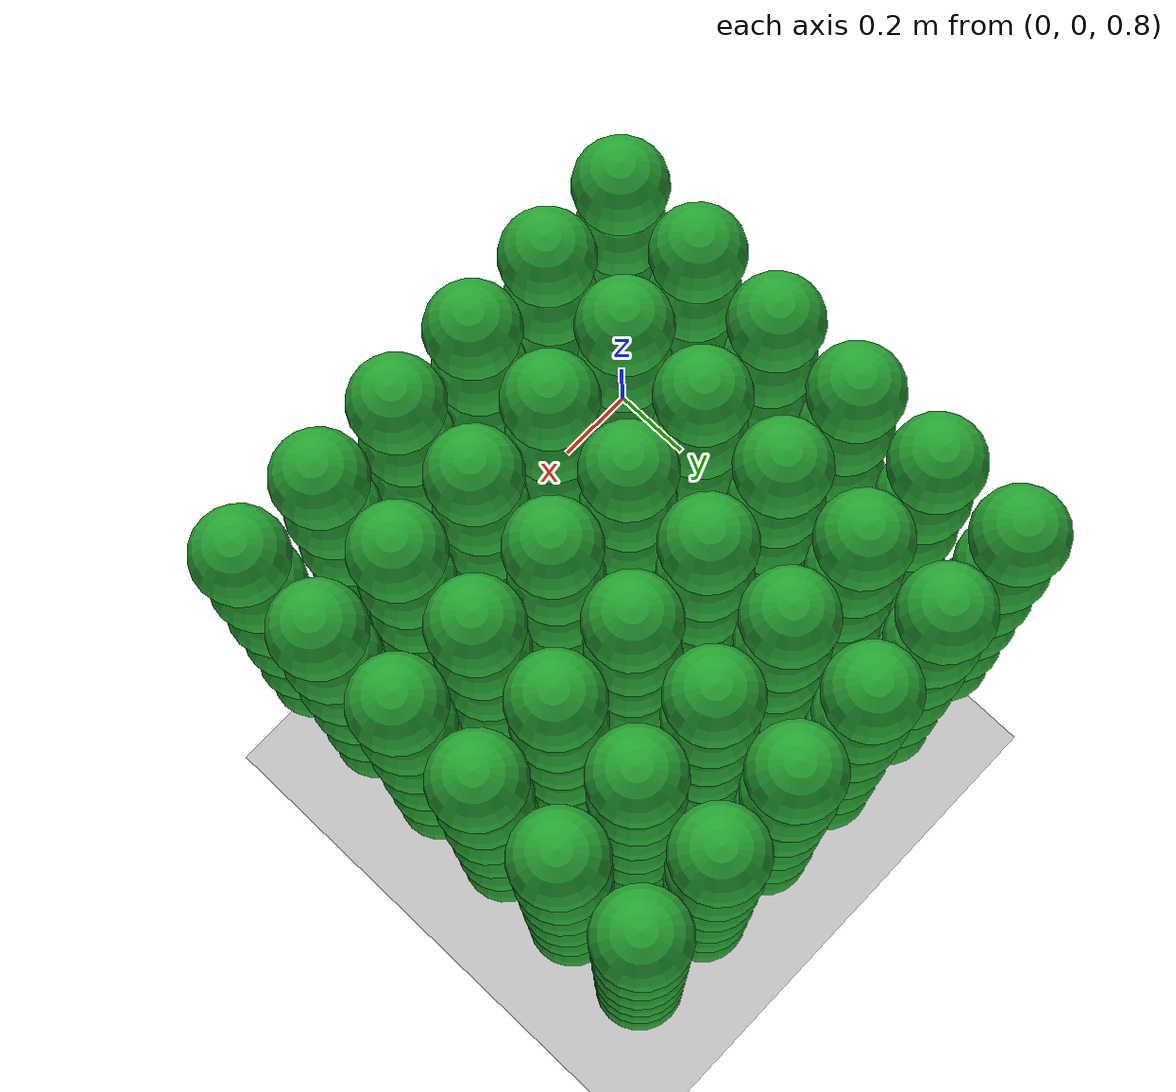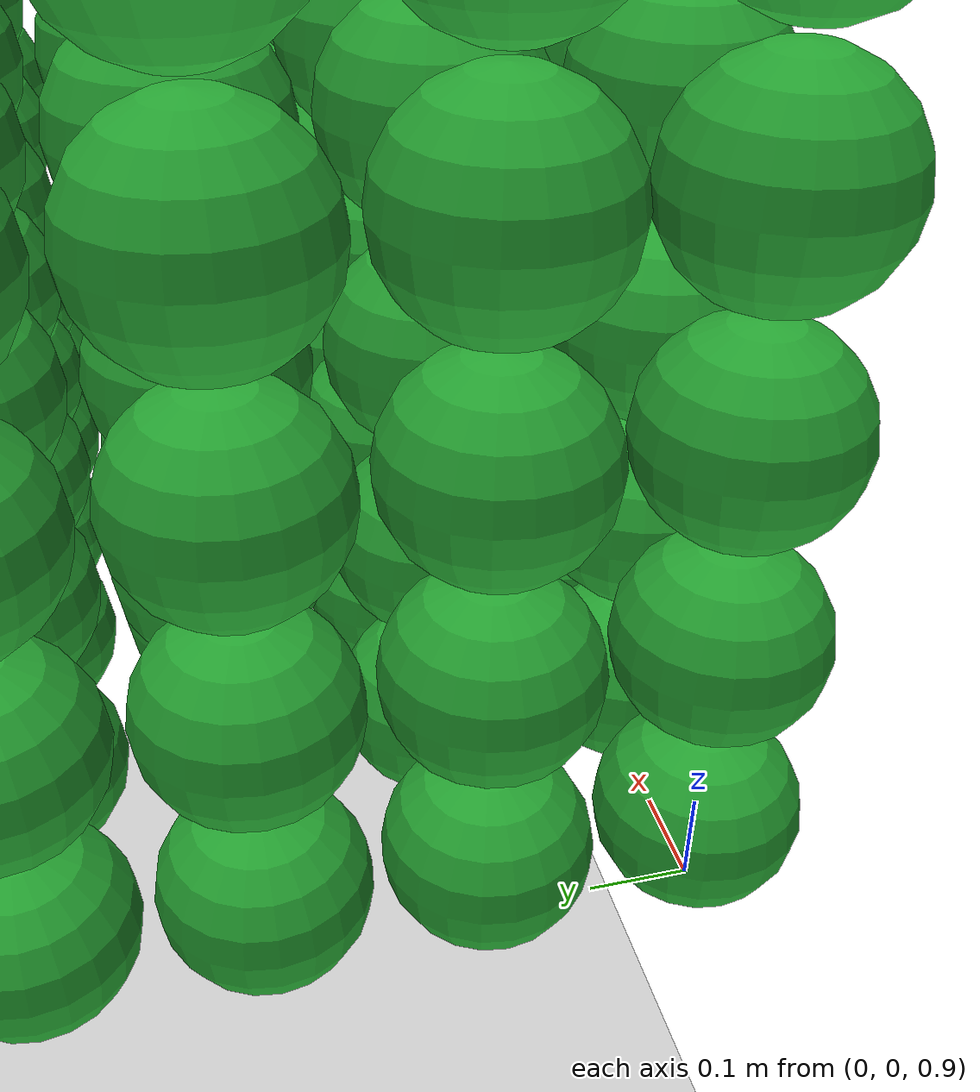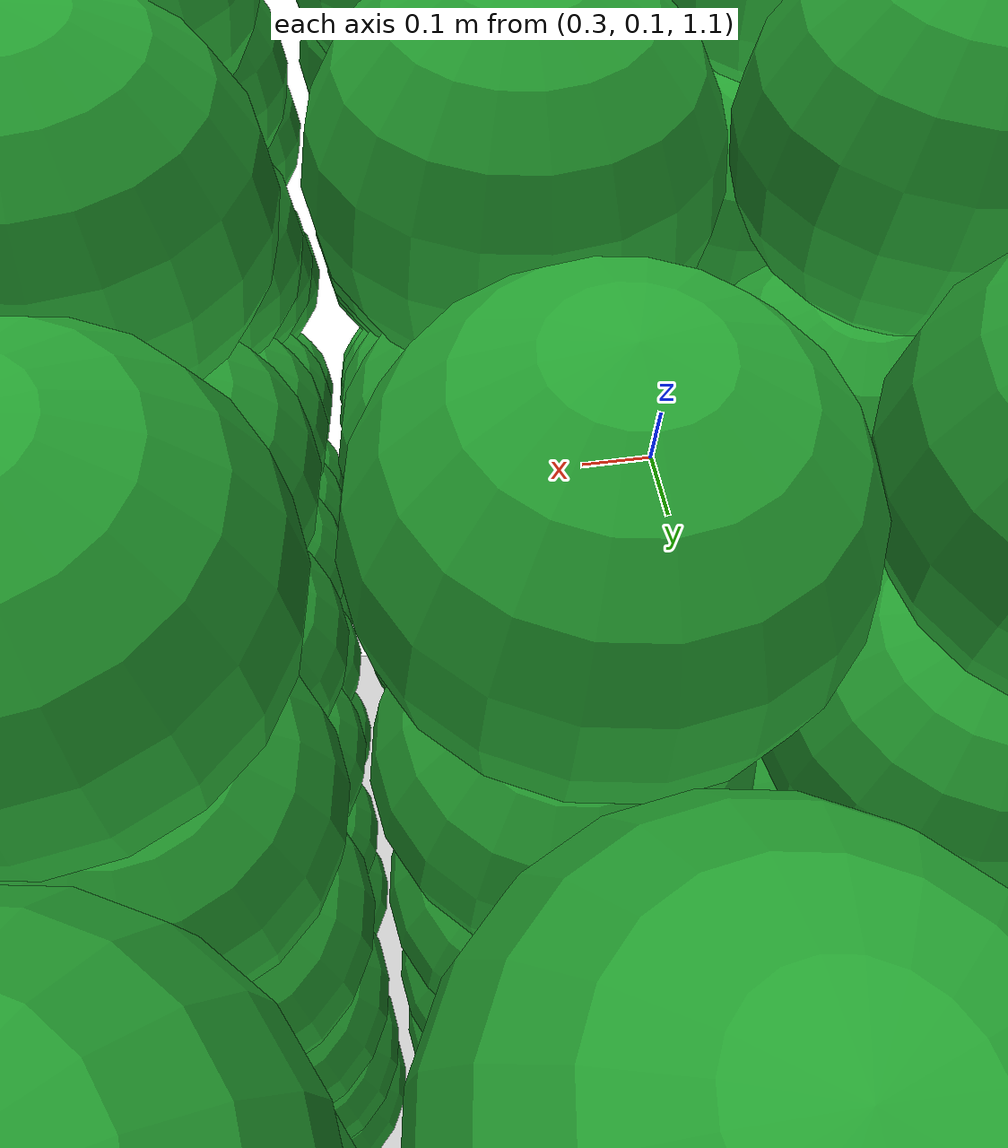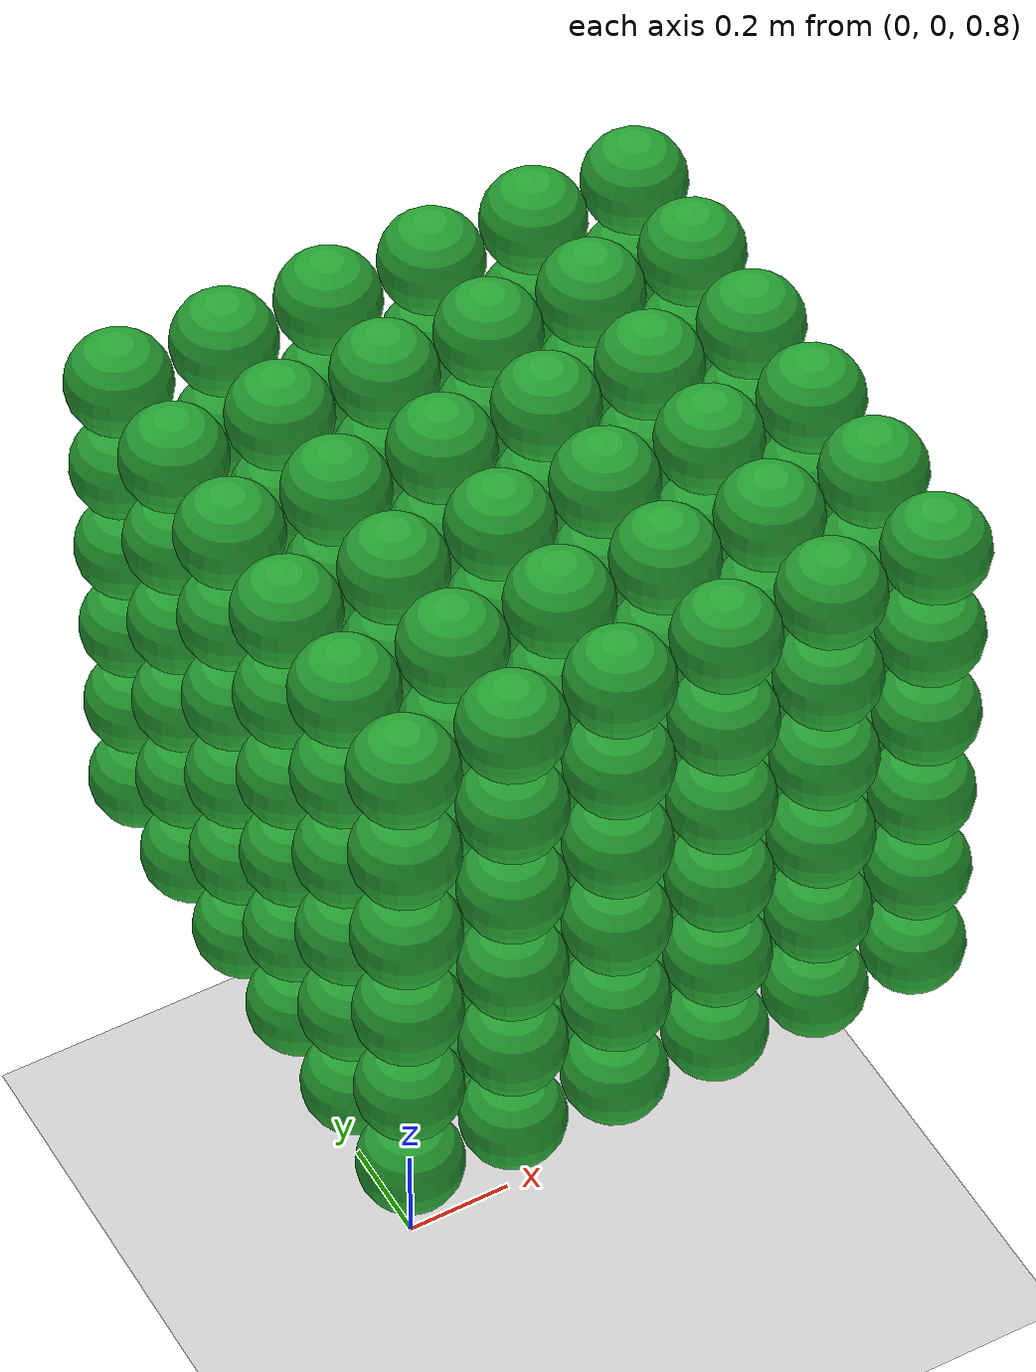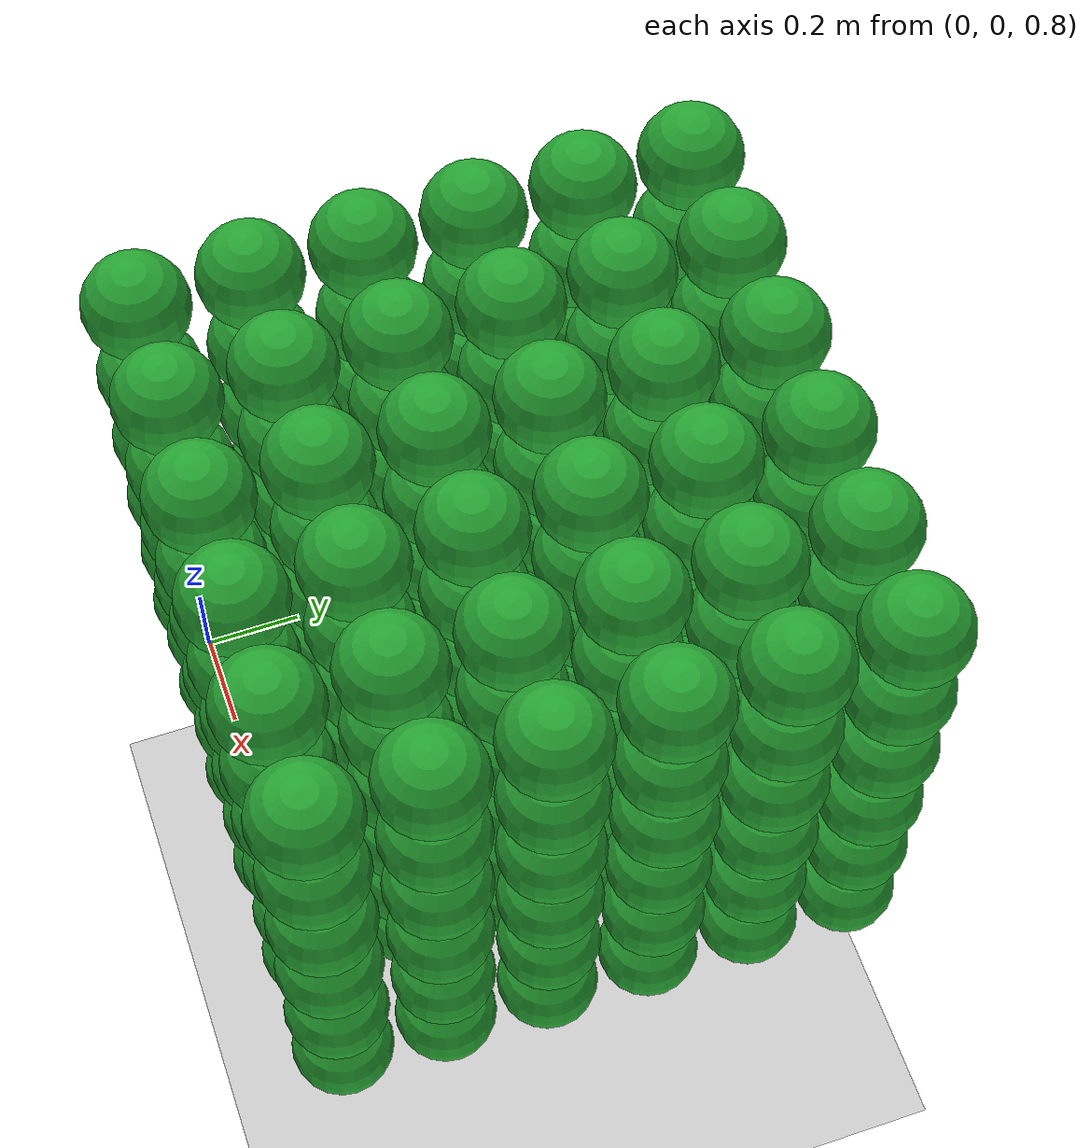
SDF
<sdf version='1.7'>
  <world name='default'>
    <light name='sun' type='directional'>
      <cast_shadows>1</cast_shadows>
      <pose>0 0 10 0 -0 0</pose>
      <diffuse>0.8 0.8 0.8 1</diffuse>
      <specular>0.2 0.2 0.2 1</specular>
      <attenuation>
        <range>1000</range>
        <constant>0.9</constant>
        <linear>0.01</linear>
        <quadratic>0.001</quadratic>
      </attenuation>
      <direction>-0.5 0.1 -0.9</direction>
      <spot>
        <inner_angle>0</inner_angle>
        <outer_angle>0</outer_angle>
        <falloff>0</falloff>
      </spot>
    </light>
    <model name='ground_plane'>
      <static>1</static>
      <link name='link'>
        <collision name='collision'>
          <geometry>
            <plane>
              <normal>0 0 1</normal>
              <size>100 100</size>
            </plane>
          </geometry>
          <surface>
            <contact>
              <collide_bitmask>65535</collide_bitmask>
              <ode/>
            </contact>
            <friction>
              <ode>
                <mu>100</mu>
                <mu2>50</mu2>
              </ode>
              <torsional>
                <ode/>
              </torsional>
            </friction>
            <bounce/>
          </surface>
          <max_contacts>10</max_contacts>
        </collision>
        <visual name='visual'>
          <cast_shadows>0</cast_shadows>
          <geometry>
            <plane>
              <normal>0 0 1</normal>
              <size>100 100</size>
            </plane>
          </geometry>
          <material>
            <script>
              <uri>file://media/materials/scripts/gazebo.material</uri>
              <name>Gazebo/Grey</name>
            </script>
          </material>
        </visual>
        <self_collide>0</self_collide>
        <enable_wind>0</enable_wind>
        <kinematic>0</kinematic>
      </link>
    </model>
    <gravity>0 0 -9.81</gravity>
    <magnetic_field>6e-06 2.3e-05 -4.2e-05</magnetic_field>
    <atmosphere type='adiabatic'/>
    <physics type='ode'>
      <max_step_size>0.001</max_step_size>
      <real_time_factor>1</real_time_factor>
      <real_time_update_rate>1000</real_time_update_rate>
    </physics>
    <scene>
      <ambient>0.4 0.4 0.4 1</ambient>
      <background>0.7 0.7 0.7 1</background>
      <shadows>1</shadows>
    </scene>
    <wind/>
    <spherical_coordinates>
      <surface_model>EARTH_WGS84</surface_model>
      <latitude_deg>0</latitude_deg>
      <longitude_deg>0</longitude_deg>
      <elevation>0</elevation>
      <heading_deg>0</heading_deg>
    </spherical_coordinates>
    	<model name='ball_0'>
      <pose>0.000000 0.000000 1.000000 0 0 0</pose>
      <link name='link'>
        <inertial>
          <mass>10.000000</mass>
          <pose>0 0 0 0 0 0</pose>
        </inertial>
        <collision name='collision'>
          <geometry>
            <sphere>
              <radius>0.100000</radius>
            </sphere>
          </geometry>
          <max_contacts>10</max_contacts>
          <surface>
            <contact>
              <ode/>
            </contact>
            <bounce/>
            <friction>
              <torsional>
                <ode/>
              </torsional>
              <ode>
                <mu>0</mu>
                <mu2>0</mu2>
              </ode>
            </friction>
          </surface>
        </collision>
        <visual name='visual'>
          <geometry>
            <sphere>
              <radius>0.100000</radius>
            </sphere>
          </geometry>
          <material>
            <script>
              <name>Gazebo/Green</name>
              <uri>file://media/materials/scripts/gazebo.material</uri>
            </script>
          </material>
        </visual>
        <self_collide>0</self_collide>
        <enable_wind>0</enable_wind>
        <kinematic>0</kinematic>
      </link>
    </model>
    	<model name='ball_1'>
      <pose>0.000000 0.000000 1.209955 0 0 0</pose>
      <link name='link'>
        <inertial>
          <mass>10.000000</mass>
          <pose>0 0 0 0 0 0</pose>
        </inertial>
        <collision name='collision'>
          <geometry>
            <sphere>
              <radius>0.100000</radius>
            </sphere>
          </geometry>
          <max_contacts>10</max_contacts>
          <surface>
            <contact>
              <ode/>
            </contact>
            <bounce/>
            <friction>
              <torsional>
                <ode/>
              </torsional>
              <ode>
                <mu>0</mu>
                <mu2>0</mu2>
              </ode>
            </friction>
          </surface>
        </collision>
        <visual name='visual'>
          <geometry>
            <sphere>
              <radius>0.100000</radius>
            </sphere>
          </geometry>
          <material>
            <script>
              <name>Gazebo/Green</name>
              <uri>file://media/materials/scripts/gazebo.material</uri>
            </script>
          </material>
        </visual>
        <self_collide>0</self_collide>
        <enable_wind>0</enable_wind>
        <kinematic>0</kinematic>
      </link>
    </model>
    	<model name='ball_2'>
      <pose>0.000000 0.000000 1.420072 0 0 0</pose>
      <link name='link'>
        <inertial>
          <mass>10.000000</mass>
          <pose>0 0 0 0 0 0</pose>
        </inertial>
        <collision name='collision'>
          <geometry>
            <sphere>
              <radius>0.100000</radius>
            </sphere>
          </geometry>
          <max_contacts>10</max_contacts>
          <surface>
            <contact>
              <ode/>
            </contact>
            <bounce/>
            <friction>
              <torsional>
                <ode/>
              </torsional>
              <ode>
                <mu>0</mu>
                <mu2>0</mu2>
              </ode>
            </friction>
          </surface>
        </collision>
        <visual name='visual'>
          <geometry>
            <sphere>
              <radius>0.100000</radius>
            </sphere>
          </geometry>
          <material>
            <script>
              <name>Gazebo/Green</name>
              <uri>file://media/materials/scripts/gazebo.material</uri>
            </script>
          </material>
        </visual>
        <self_collide>0</self_collide>
        <enable_wind>0</enable_wind>
        <kinematic>0</kinematic>
      </link>
    </model>
    	<model name='ball_3'>
      <pose>0.000000 0.000000 1.629689 0 0 0</pose>
      <link name='link'>
        <inertial>
          <mass>10.000000</mass>
          <pose>0 0 0 0 0 0</pose>
        </inertial>
        <collision name='collision'>
          <geometry>
            <sphere>
              <radius>0.100000</radius>
            </sphere>
          </geometry>
          <max_contacts>10</max_contacts>
          <surface>
            <contact>
              <ode/>
            </contact>
            <bounce/>
            <friction>
              <torsional>
                <ode/>
              </torsional>
              <ode>
                <mu>0</mu>
                <mu2>0</mu2>
              </ode>
            </friction>
          </surface>
        </collision>
        <visual name='visual'>
          <geometry>
            <sphere>
              <radius>0.100000</radius>
            </sphere>
          </geometry>
          <material>
            <script>
              <name>Gazebo/Green</name>
              <uri>file://media/materials/scripts/gazebo.material</uri>
            </script>
          </material>
        </visual>
        <self_collide>0</self_collide>
        <enable_wind>0</enable_wind>
        <kinematic>0</kinematic>
      </link>
    </model>
    	<model name='ball_4'>
      <pose>0.000000 0.000000 1.840104 0 0 0</pose>
      <link name='link'>
        <inertial>
          <mass>10.000000</mass>
          <pose>0 0 0 0 0 0</pose>
        </inertial>
        <collision name='collision'>
          <geometry>
            <sphere>
              <radius>0.100000</radius>
            </sphere>
          </geometry>
          <max_contacts>10</max_contacts>
          <surface>
            <contact>
              <ode/>
            </contact>
            <bounce/>
            <friction>
              <torsional>
                <ode/>
              </torsional>
              <ode>
                <mu>0</mu>
                <mu2>0</mu2>
              </ode>
            </friction>
          </surface>
        </collision>
        <visual name='visual'>
          <geometry>
            <sphere>
              <radius>0.100000</radius>
            </sphere>
          </geometry>
          <material>
            <script>
              <name>Gazebo/Green</name>
              <uri>file://media/materials/scripts/gazebo.material</uri>
            </script>
          </material>
        </visual>
        <self_collide>0</self_collide>
        <enable_wind>0</enable_wind>
        <kinematic>0</kinematic>
      </link>
    </model>
    	<model name='ball_5'>
      <pose>0.000000 0.000000 2.049521 0 0 0</pose>
      <link name='link'>
        <inertial>
          <mass>10.000000</mass>
          <pose>0 0 0 0 0 0</pose>
        </inertial>
        <collision name='collision'>
          <geometry>
            <sphere>
              <radius>0.100000</radius>
            </sphere>
          </geometry>
          <max_contacts>10</max_contacts>
          <surface>
            <contact>
              <ode/>
            </contact>
            <bounce/>
            <friction>
              <torsional>
                <ode/>
              </torsional>
              <ode>
                <mu>0</mu>
                <mu2>0</mu2>
              </ode>
            </friction>
          </surface>
        </collision>
        <visual name='visual'>
          <geometry>
            <sphere>
              <radius>0.100000</radius>
            </sphere>
          </geometry>
          <material>
            <script>
              <name>Gazebo/Green</name>
              <uri>file://media/materials/scripts/gazebo.material</uri>
            </script>
          </material>
        </visual>
        <self_collide>0</self_collide>
        <enable_wind>0</enable_wind>
        <kinematic>0</kinematic>
      </link>
    </model>
    	<model name='ball_6'>
      <pose>0.000000 0.209839 1.000000 0 0 0</pose>
      <link name='link'>
        <inertial>
          <mass>10.000000</mass>
          <pose>0 0 0 0 0 0</pose>
        </inertial>
        <collision name='collision'>
          <geometry>
            <sphere>
              <radius>0.100000</radius>
            </sphere>
          </geometry>
          <max_contacts>10</max_contacts>
          <surface>
            <contact>
              <ode/>
            </contact>
            <bounce/>
            <friction>
              <torsional>
                <ode/>
              </torsional>
              <ode>
                <mu>0</mu>
                <mu2>0</mu2>
              </ode>
            </friction>
          </surface>
        </collision>
        <visual name='visual'>
          <geometry>
            <sphere>
              <radius>0.100000</radius>
            </sphere>
          </geometry>
          <material>
            <script>
              <name>Gazebo/Green</name>
              <uri>file://media/materials/scripts/gazebo.material</uri>
            </script>
          </material>
        </visual>
        <self_collide>0</self_collide>
        <enable_wind>0</enable_wind>
        <kinematic>0</kinematic>
      </link>
    </model>
    	<model name='ball_7'>
      <pose>0.000000 0.210104 1.210104 0 0 0</pose>
      <link name='link'>
        <inertial>
          <mass>10.000000</mass>
          <pose>0 0 0 0 0 0</pose>
        </inertial>
        <collision name='collision'>
          <geometry>
            <sphere>
              <radius>0.100000</radius>
            </sphere>
          </geometry>
          <max_contacts>10</max_contacts>
          <surface>
            <contact>
              <ode/>
            </contact>
            <bounce/>
            <friction>
              <torsional>
                <ode/>
              </torsional>
              <ode>
                <mu>0</mu>
                <mu2>0</mu2>
              </ode>
            </friction>
          </surface>
        </collision>
        <visual name='visual'>
          <geometry>
            <sphere>
              <radius>0.100000</radius>
            </sphere>
          </geometry>
          <material>
            <script>
              <name>Gazebo/Green</name>
              <uri>file://media/materials/scripts/gazebo.material</uri>
            </script>
          </material>
        </visual>
        <self_collide>0</self_collide>
        <enable_wind>0</enable_wind>
        <kinematic>0</kinematic>
      </link>
    </model>
    	<model name='ball_8'>
      <pose>0.000000 0.209921 1.419842 0 0 0</pose>
      <link name='link'>
        <inertial>
          <mass>10.000000</mass>
          <pose>0 0 0 0 0 0</pose>
        </inertial>
        <collision name='collision'>
          <geometry>
            <sphere>
              <radius>0.100000</radius>
            </sphere>
          </geometry>
          <max_contacts>10</max_contacts>
          <surface>
            <contact>
              <ode/>
            </contact>
            <bounce/>
            <friction>
              <torsional>
                <ode/>
              </torsional>
              <ode>
                <mu>0</mu>
                <mu2>0</mu2>
              </ode>
            </friction>
          </surface>
        </collision>
        <visual name='visual'>
          <geometry>
            <sphere>
              <radius>0.100000</radius>
            </sphere>
          </geometry>
          <material>
            <script>
              <name>Gazebo/Green</name>
              <uri>file://media/materials/scripts/gazebo.material</uri>
            </script>
          </material>
        </visual>
        <self_collide>0</self_collide>
        <enable_wind>0</enable_wind>
        <kinematic>0</kinematic>
      </link>
    </model>
    	<model name='ball_9'>
      <pose>0.000000 0.209934 1.629803 0 0 0</pose>
      <link name='link'>
        <inertial>
          <mass>10.000000</mass>
          <pose>0 0 0 0 0 0</pose>
        </inertial>
        <collision name='collision'>
          <geometry>
            <sphere>
              <radius>0.100000</radius>
            </sphere>
          </geometry>
          <max_contacts>10</max_contacts>
          <surface>
            <contact>
              <ode/>
            </contact>
            <bounce/>
            <friction>
              <torsional>
                <ode/>
              </torsional>
              <ode>
                <mu>0</mu>
                <mu2>0</mu2>
              </ode>
            </friction>
          </surface>
        </collision>
        <visual name='visual'>
          <geometry>
            <sphere>
              <radius>0.100000</radius>
            </sphere>
          </geometry>
          <material>
            <script>
              <name>Gazebo/Green</name>
              <uri>file://media/materials/scripts/gazebo.material</uri>
            </script>
          </material>
        </visual>
        <self_collide>0</self_collide>
        <enable_wind>0</enable_wind>
        <kinematic>0</kinematic>
      </link>
    </model>
    	<model name='ball_10'>
      <pose>0.000000 0.210197 1.840787 0 0 0</pose>
      <link name='link'>
        <inertial>
          <mass>10.000000</mass>
          <pose>0 0 0 0 0 0</pose>
        </inertial>
        <collision name='collision'>
          <geometry>
            <sphere>
              <radius>0.100000</radius>
            </sphere>
          </geometry>
          <max_contacts>10</max_contacts>
          <surface>
            <contact>
              <ode/>
            </contact>
            <bounce/>
            <friction>
              <torsional>
                <ode/>
              </torsional>
              <ode>
                <mu>0</mu>
                <mu2>0</mu2>
              </ode>
            </friction>
          </surface>
        </collision>
        <visual name='visual'>
          <geometry>
            <sphere>
              <radius>0.100000</radius>
            </sphere>
          </geometry>
          <material>
            <script>
              <name>Gazebo/Green</name>
              <uri>file://media/materials/scripts/gazebo.material</uri>
            </script>
          </material>
        </visual>
        <self_collide>0</self_collide>
        <enable_wind>0</enable_wind>
        <kinematic>0</kinematic>
      </link>
    </model>
    	<model name='ball_11'>
      <pose>0.000000 0.210185 2.050924 0 0 0</pose>
      <link name='link'>
        <inertial>
          <mass>10.000000</mass>
          <pose>0 0 0 0 0 0</pose>
        </inertial>
        <collision name='collision'>
          <geometry>
            <sphere>
              <radius>0.100000</radius>
            </sphere>
          </geometry>
          <max_contacts>10</max_contacts>
          <surface>
            <contact>
              <ode/>
            </contact>
            <bounce/>
            <friction>
              <torsional>
                <ode/>
              </torsional>
              <ode>
                <mu>0</mu>
                <mu2>0</mu2>
              </ode>
            </friction>
          </surface>
        </collision>
        <visual name='visual'>
          <geometry>
            <sphere>
              <radius>0.100000</radius>
            </sphere>
          </geometry>
          <material>
            <script>
              <name>Gazebo/Green</name>
              <uri>file://media/materials/scripts/gazebo.material</uri>
            </script>
          </material>
        </visual>
        <self_collide>0</self_collide>
        <enable_wind>0</enable_wind>
        <kinematic>0</kinematic>
      </link>
    </model>
    	<model name='ball_12'>
      <pose>0.000000 0.420170 1.000000 0 0 0</pose>
      <link name='link'>
        <inertial>
          <mass>10.000000</mass>
          <pose>0 0 0 0 0 0</pose>
        </inertial>
        <collision name='collision'>
          <geometry>
            <sphere>
              <radius>0.100000</radius>
            </sphere>
          </geometry>
          <max_contacts>10</max_contacts>
          <surface>
            <contact>
              <ode/>
            </contact>
            <bounce/>
            <friction>
              <torsional>
                <ode/>
              </torsional>
              <ode>
                <mu>0</mu>
                <mu2>0</mu2>
              </ode>
            </friction>
          </surface>
        </collision>
        <visual name='visual'>
          <geometry>
            <sphere>
              <radius>0.100000</radius>
            </sphere>
          </geometry>
          <material>
            <script>
              <name>Gazebo/Green</name>
              <uri>file://media/materials/scripts/gazebo.material</uri>
            </script>
          </material>
        </visual>
        <self_collide>0</self_collide>
        <enable_wind>0</enable_wind>
        <kinematic>0</kinematic>
      </link>
    </model>
    	<model name='ball_13'>
      <pose>0.000000 0.420080 1.210040 0 0 0</pose>
      <link name='link'>
        <inertial>
          <mass>10.000000</mass>
          <pose>0 0 0 0 0 0</pose>
        </inertial>
        <collision name='collision'>
          <geometry>
            <sphere>
              <radius>0.100000</radius>
            </sphere>
          </geometry>
          <max_contacts>10</max_contacts>
          <surface>
            <contact>
              <ode/>
            </contact>
            <bounce/>
            <friction>
              <torsional>
                <ode/>
              </torsional>
              <ode>
                <mu>0</mu>
                <mu2>0</mu2>
              </ode>
            </friction>
          </surface>
        </collision>
        <visual name='visual'>
          <geometry>
            <sphere>
              <radius>0.100000</radius>
            </sphere>
          </geometry>
          <material>
            <script>
              <name>Gazebo/Green</name>
              <uri>file://media/materials/scripts/gazebo.material</uri>
            </script>
          </material>
        </visual>
        <self_collide>0</self_collide>
        <enable_wind>0</enable_wind>
        <kinematic>0</kinematic>
      </link>
    </model>
    	<model name='ball_14'>
      <pose>0.000000 0.419637 1.419637 0 0 0</pose>
      <link name='link'>
        <inertial>
          <mass>10.000000</mass>
          <pose>0 0 0 0 0 0</pose>
        </inertial>
        <collision name='collision'>
          <geometry>
            <sphere>
              <radius>0.100000</radius>
            </sphere>
          </geometry>
          <max_contacts>10</max_contacts>
          <surface>
            <contact>
              <ode/>
            </contact>
            <bounce/>
            <friction>
              <torsional>
                <ode/>
              </torsional>
              <ode>
                <mu>0</mu>
                <mu2>0</mu2>
              </ode>
            </friction>
          </surface>
        </collision>
        <visual name='visual'>
          <geometry>
            <sphere>
              <radius>0.100000</radius>
            </sphere>
          </geometry>
          <material>
            <script>
              <name>Gazebo/Green</name>
              <uri>file://media/materials/scripts/gazebo.material</uri>
            </script>
          </material>
        </visual>
        <self_collide>0</self_collide>
        <enable_wind>0</enable_wind>
        <kinematic>0</kinematic>
      </link>
    </model>
    	<model name='ball_15'>
      <pose>0.000000 0.419633 1.629450 0 0 0</pose>
      <link name='link'>
        <inertial>
          <mass>10.000000</mass>
          <pose>0 0 0 0 0 0</pose>
        </inertial>
        <collision name='collision'>
          <geometry>
            <sphere>
              <radius>0.100000</radius>
            </sphere>
          </geometry>
          <max_contacts>10</max_contacts>
          <surface>
            <contact>
              <ode/>
            </contact>
            <bounce/>
            <friction>
              <torsional>
                <ode/>
              </torsional>
              <ode>
                <mu>0</mu>
                <mu2>0</mu2>
              </ode>
            </friction>
          </surface>
        </collision>
        <visual name='visual'>
          <geometry>
            <sphere>
              <radius>0.100000</radius>
            </sphere>
          </geometry>
          <material>
            <script>
              <name>Gazebo/Green</name>
              <uri>file://media/materials/scripts/gazebo.material</uri>
            </script>
          </material>
        </visual>
        <self_collide>0</self_collide>
        <enable_wind>0</enable_wind>
        <kinematic>0</kinematic>
      </link>
    </model>
    	<model name='ball_16'>
      <pose>0.000000 0.420401 1.840802 0 0 0</pose>
      <link name='link'>
        <inertial>
          <mass>10.000000</mass>
          <pose>0 0 0 0 0 0</pose>
        </inertial>
        <collision name='collision'>
          <geometry>
            <sphere>
              <radius>0.100000</radius>
            </sphere>
          </geometry>
          <max_contacts>10</max_contacts>
          <surface>
            <contact>
              <ode/>
            </contact>
            <bounce/>
            <friction>
              <torsional>
                <ode/>
              </torsional>
              <ode>
                <mu>0</mu>
                <mu2>0</mu2>
              </ode>
            </friction>
          </surface>
        </collision>
        <visual name='visual'>
          <geometry>
            <sphere>
              <radius>0.100000</radius>
            </sphere>
          </geometry>
          <material>
            <script>
              <name>Gazebo/Green</name>
              <uri>file://media/materials/scripts/gazebo.material</uri>
            </script>
          </material>
        </visual>
        <self_collide>0</self_collide>
        <enable_wind>0</enable_wind>
        <kinematic>0</kinematic>
      </link>
    </model>
    	<model name='ball_17'>
      <pose>0.000000 0.419922 2.049804 0 0 0</pose>
      <link name='link'>
        <inertial>
          <mass>10.000000</mass>
          <pose>0 0 0 0 0 0</pose>
        </inertial>
        <collision name='collision'>
          <geometry>
            <sphere>
              <radius>0.100000</radius>
            </sphere>
          </geometry>
          <max_contacts>10</max_contacts>
          <surface>
            <contact>
              <ode/>
            </contact>
            <bounce/>
            <friction>
              <torsional>
                <ode/>
              </torsional>
              <ode>
                <mu>0</mu>
                <mu2>0</mu2>
              </ode>
            </friction>
          </surface>
        </collision>
        <visual name='visual'>
          <geometry>
            <sphere>
              <radius>0.100000</radius>
            </sphere>
          </geometry>
          <material>
            <script>
              <name>Gazebo/Green</name>
              <uri>file://media/materials/scripts/gazebo.material</uri>
            </script>
          </material>
        </visual>
        <self_collide>0</self_collide>
        <enable_wind>0</enable_wind>
        <kinematic>0</kinematic>
      </link>
    </model>
    	<model name='ball_18'>
      <pose>0.000000 0.630081 1.000000 0 0 0</pose>
      <link name='link'>
        <inertial>
          <mass>10.000000</mass>
          <pose>0 0 0 0 0 0</pose>
        </inertial>
        <collision name='collision'>
          <geometry>
            <sphere>
              <radius>0.100000</radius>
            </sphere>
          </geometry>
          <max_contacts>10</max_contacts>
          <surface>
            <contact>
              <ode/>
            </contact>
            <bounce/>
            <friction>
              <torsional>
                <ode/>
              </torsional>
              <ode>
                <mu>0</mu>
                <mu2>0</mu2>
              </ode>
            </friction>
          </surface>
        </collision>
        <visual name='visual'>
          <geometry>
            <sphere>
              <radius>0.100000</radius>
            </sphere>
          </geometry>
          <material>
            <script>
              <name>Gazebo/Green</name>
              <uri>file://media/materials/scripts/gazebo.material</uri>
            </script>
          </material>
        </visual>
        <self_collide>0</self_collide>
        <enable_wind>0</enable_wind>
        <kinematic>0</kinematic>
      </link>
    </model>
    	<model name='ball_19'>
      <pose>0.000000 0.629412 1.209804 0 0 0</pose>
      <link name='link'>
        <inertial>
          <mass>10.000000</mass>
          <pose>0 0 0 0 0 0</pose>
        </inertial>
        <collision name='collision'>
          <geometry>
            <sphere>
              <radius>0.100000</radius>
            </sphere>
          </geometry>
          <max_contacts>10</max_contacts>
          <surface>
            <contact>
              <ode/>
            </contact>
            <bounce/>
            <friction>
              <torsional>
                <ode/>
              </torsional>
              <ode>
                <mu>0</mu>
                <mu2>0</mu2>
              </ode>
            </friction>
          </surface>
        </collision>
        <visual name='visual'>
          <geometry>
            <sphere>
              <radius>0.100000</radius>
            </sphere>
          </geometry>
          <material>
            <script>
              <name>Gazebo/Green</name>
              <uri>file://media/materials/scripts/gazebo.material</uri>
            </script>
          </material>
        </visual>
        <self_collide>0</self_collide>
        <enable_wind>0</enable_wind>
        <kinematic>0</kinematic>
      </link>
    </model>
    	<model name='ball_20'>
      <pose>0.000000 0.630457 1.420305 0 0 0</pose>
      <link name='link'>
        <inertial>
          <mass>10.000000</mass>
          <pose>0 0 0 0 0 0</pose>
        </inertial>
        <collision name='collision'>
          <geometry>
            <sphere>
              <radius>0.100000</radius>
            </sphere>
          </geometry>
          <max_contacts>10</max_contacts>
          <surface>
            <contact>
              <ode/>
            </contact>
            <bounce/>
            <friction>
              <torsional>
                <ode/>
              </torsional>
              <ode>
                <mu>0</mu>
                <mu2>0</mu2>
              </ode>
            </friction>
          </surface>
        </collision>
        <visual name='visual'>
          <geometry>
            <sphere>
              <radius>0.100000</radius>
            </sphere>
          </geometry>
          <material>
            <script>
              <name>Gazebo/Green</name>
              <uri>file://media/materials/scripts/gazebo.material</uri>
            </script>
          </material>
        </visual>
        <self_collide>0</self_collide>
        <enable_wind>0</enable_wind>
        <kinematic>0</kinematic>
      </link>
    </model>
    	<model name='ball_21'>
      <pose>0.000000 0.629525 1.629525 0 0 0</pose>
      <link name='link'>
        <inertial>
          <mass>10.000000</mass>
          <pose>0 0 0 0 0 0</pose>
        </inertial>
        <collision name='collision'>
          <geometry>
            <sphere>
              <radius>0.100000</radius>
            </sphere>
          </geometry>
          <max_contacts>10</max_contacts>
          <surface>
            <contact>
              <ode/>
            </contact>
            <bounce/>
            <friction>
              <torsional>
                <ode/>
              </torsional>
              <ode>
                <mu>0</mu>
                <mu2>0</mu2>
              </ode>
            </friction>
          </surface>
        </collision>
        <visual name='visual'>
          <geometry>
            <sphere>
              <radius>0.100000</radius>
            </sphere>
          </geometry>
          <material>
            <script>
              <name>Gazebo/Green</name>
              <uri>file://media/materials/scripts/gazebo.material</uri>
            </script>
          </material>
        </visual>
        <self_collide>0</self_collide>
        <enable_wind>0</enable_wind>
        <kinematic>0</kinematic>
      </link>
    </model>
    	<model name='ball_22'>
      <pose>0.000000 0.630356 1.840474 0 0 0</pose>
      <link name='link'>
        <inertial>
          <mass>10.000000</mass>
          <pose>0 0 0 0 0 0</pose>
        </inertial>
        <collision name='collision'>
          <geometry>
            <sphere>
              <radius>0.100000</radius>
            </sphere>
          </geometry>
          <max_contacts>10</max_contacts>
          <surface>
            <contact>
              <ode/>
            </contact>
            <bounce/>
            <friction>
              <torsional>
                <ode/>
              </torsional>
              <ode>
                <mu>0</mu>
                <mu2>0</mu2>
              </ode>
            </friction>
          </surface>
        </collision>
        <visual name='visual'>
          <geometry>
            <sphere>
              <radius>0.100000</radius>
            </sphere>
          </geometry>
          <material>
            <script>
              <name>Gazebo/Green</name>
              <uri>file://media/materials/scripts/gazebo.material</uri>
            </script>
          </material>
        </visual>
        <self_collide>0</self_collide>
        <enable_wind>0</enable_wind>
        <kinematic>0</kinematic>
      </link>
    </model>
    	<model name='ball_23'>
      <pose>0.000000 0.630212 2.050354 0 0 0</pose>
      <link name='link'>
        <inertial>
          <mass>10.000000</mass>
          <pose>0 0 0 0 0 0</pose>
        </inertial>
        <collision name='collision'>
          <geometry>
            <sphere>
              <radius>0.100000</radius>
            </sphere>
          </geometry>
          <max_contacts>10</max_contacts>
          <surface>
            <contact>
              <ode/>
            </contact>
            <bounce/>
            <friction>
              <torsional>
                <ode/>
              </torsional>
              <ode>
                <mu>0</mu>
                <mu2>0</mu2>
              </ode>
            </friction>
          </surface>
        </collision>
        <visual name='visual'>
          <geometry>
            <sphere>
              <radius>0.100000</radius>
            </sphere>
          </geometry>
          <material>
            <script>
              <name>Gazebo/Green</name>
              <uri>file://media/materials/scripts/gazebo.material</uri>
            </script>
          </material>
        </visual>
        <self_collide>0</self_collide>
        <enable_wind>0</enable_wind>
        <kinematic>0</kinematic>
      </link>
    </model>
    	<model name='ball_24'>
      <pose>0.000000 0.839498 1.000000 0 0 0</pose>
      <link name='link'>
        <inertial>
          <mass>10.000000</mass>
          <pose>0 0 0 0 0 0</pose>
        </inertial>
        <collision name='collision'>
          <geometry>
            <sphere>
              <radius>0.100000</radius>
            </sphere>
          </geometry>
          <max_contacts>10</max_contacts>
          <surface>
            <contact>
              <ode/>
            </contact>
            <bounce/>
            <friction>
              <torsional>
                <ode/>
              </torsional>
              <ode>
                <mu>0</mu>
                <mu2>0</mu2>
              </ode>
            </friction>
          </surface>
        </collision>
        <visual name='visual'>
          <geometry>
            <sphere>
              <radius>0.100000</radius>
            </sphere>
          </geometry>
          <material>
            <script>
              <name>Gazebo/Green</name>
              <uri>file://media/materials/scripts/gazebo.material</uri>
            </script>
          </material>
        </visual>
        <self_collide>0</self_collide>
        <enable_wind>0</enable_wind>
        <kinematic>0</kinematic>
      </link>
    </model>
    	<model name='ball_25'>
      <pose>0.000000 0.840572 1.210143 0 0 0</pose>
      <link name='link'>
        <inertial>
          <mass>10.000000</mass>
          <pose>0 0 0 0 0 0</pose>
        </inertial>
        <collision name='collision'>
          <geometry>
            <sphere>
              <radius>0.100000</radius>
            </sphere>
          </geometry>
          <max_contacts>10</max_contacts>
          <surface>
            <contact>
              <ode/>
            </contact>
            <bounce/>
            <friction>
              <torsional>
                <ode/>
              </torsional>
              <ode>
                <mu>0</mu>
                <mu2>0</mu2>
              </ode>
            </friction>
          </surface>
        </collision>
        <visual name='visual'>
          <geometry>
            <sphere>
              <radius>0.100000</radius>
            </sphere>
          </geometry>
          <material>
            <script>
              <name>Gazebo/Green</name>
              <uri>file://media/materials/scripts/gazebo.material</uri>
            </script>
          </material>
        </visual>
        <self_collide>0</self_collide>
        <enable_wind>0</enable_wind>
        <kinematic>0</kinematic>
      </link>
    </model>
    	<model name='ball_26'>
      <pose>0.000000 0.839750 1.419875 0 0 0</pose>
      <link name='link'>
        <inertial>
          <mass>10.000000</mass>
          <pose>0 0 0 0 0 0</pose>
        </inertial>
        <collision name='collision'>
          <geometry>
            <sphere>
              <radius>0.100000</radius>
            </sphere>
          </geometry>
          <max_contacts>10</max_contacts>
          <surface>
            <contact>
              <ode/>
            </contact>
            <bounce/>
            <friction>
              <torsional>
                <ode/>
              </torsional>
              <ode>
                <mu>0</mu>
                <mu2>0</mu2>
              </ode>
            </friction>
          </surface>
        </collision>
        <visual name='visual'>
          <geometry>
            <sphere>
              <radius>0.100000</radius>
            </sphere>
          </geometry>
          <material>
            <script>
              <name>Gazebo/Green</name>
              <uri>file://media/materials/scripts/gazebo.material</uri>
            </script>
          </material>
        </visual>
        <self_collide>0</self_collide>
        <enable_wind>0</enable_wind>
        <kinematic>0</kinematic>
      </link>
    </model>
    	<model name='ball_27'>
      <pose>0.000000 0.839731 1.629798 0 0 0</pose>
      <link name='link'>
        <inertial>
          <mass>10.000000</mass>
          <pose>0 0 0 0 0 0</pose>
        </inertial>
        <collision name='collision'>
          <geometry>
            <sphere>
              <radius>0.100000</radius>
            </sphere>
          </geometry>
          <max_contacts>10</max_contacts>
          <surface>
            <contact>
              <ode/>
            </contact>
            <bounce/>
            <friction>
              <torsional>
                <ode/>
              </torsional>
              <ode>
                <mu>0</mu>
                <mu2>0</mu2>
              </ode>
            </friction>
          </surface>
        </collision>
        <visual name='visual'>
          <geometry>
            <sphere>
              <radius>0.100000</radius>
            </sphere>
          </geometry>
          <material>
            <script>
              <name>Gazebo/Green</name>
              <uri>file://media/materials/scripts/gazebo.material</uri>
            </script>
          </material>
        </visual>
        <self_collide>0</self_collide>
        <enable_wind>0</enable_wind>
        <kinematic>0</kinematic>
      </link>
    </model>
    	<model name='ball_28'>
      <pose>0.000000 0.839965 1.839965 0 0 0</pose>
      <link name='link'>
        <inertial>
          <mass>10.000000</mass>
          <pose>0 0 0 0 0 0</pose>
        </inertial>
        <collision name='collision'>
          <geometry>
            <sphere>
              <radius>0.100000</radius>
            </sphere>
          </geometry>
          <max_contacts>10</max_contacts>
          <surface>
            <contact>
              <ode/>
            </contact>
            <bounce/>
            <friction>
              <torsional>
                <ode/>
              </torsional>
              <ode>
                <mu>0</mu>
                <mu2>0</mu2>
              </ode>
            </friction>
          </surface>
        </collision>
        <visual name='visual'>
          <geometry>
            <sphere>
              <radius>0.100000</radius>
            </sphere>
          </geometry>
          <material>
            <script>
              <name>Gazebo/Green</name>
              <uri>file://media/materials/scripts/gazebo.material</uri>
            </script>
          </material>
        </visual>
        <self_collide>0</self_collide>
        <enable_wind>0</enable_wind>
        <kinematic>0</kinematic>
      </link>
    </model>
    	<model name='ball_29'>
      <pose>0.000000 0.839703 2.049629 0 0 0</pose>
      <link name='link'>
        <inertial>
          <mass>10.000000</mass>
          <pose>0 0 0 0 0 0</pose>
        </inertial>
        <collision name='collision'>
          <geometry>
            <sphere>
              <radius>0.100000</radius>
            </sphere>
          </geometry>
          <max_contacts>10</max_contacts>
          <surface>
            <contact>
              <ode/>
            </contact>
            <bounce/>
            <friction>
              <torsional>
                <ode/>
              </torsional>
              <ode>
                <mu>0</mu>
                <mu2>0</mu2>
              </ode>
            </friction>
          </surface>
        </collision>
        <visual name='visual'>
          <geometry>
            <sphere>
              <radius>0.100000</radius>
            </sphere>
          </geometry>
          <material>
            <script>
              <name>Gazebo/Green</name>
              <uri>file://media/materials/scripts/gazebo.material</uri>
            </script>
          </material>
        </visual>
        <self_collide>0</self_collide>
        <enable_wind>0</enable_wind>
        <kinematic>0</kinematic>
      </link>
    </model>
    	<model name='ball_30'>
      <pose>0.000000 1.050613 1.000000 0 0 0</pose>
      <link name='link'>
        <inertial>
          <mass>10.000000</mass>
          <pose>0 0 0 0 0 0</pose>
        </inertial>
        <collision name='collision'>
          <geometry>
            <sphere>
              <radius>0.100000</radius>
            </sphere>
          </geometry>
          <max_contacts>10</max_contacts>
          <surface>
            <contact>
              <ode/>
            </contact>
            <bounce/>
            <friction>
              <torsional>
                <ode/>
              </torsional>
              <ode>
                <mu>0</mu>
                <mu2>0</mu2>
              </ode>
            </friction>
          </surface>
        </collision>
        <visual name='visual'>
          <geometry>
            <sphere>
              <radius>0.100000</radius>
            </sphere>
          </geometry>
          <material>
            <script>
              <name>Gazebo/Green</name>
              <uri>file://media/materials/scripts/gazebo.material</uri>
            </script>
          </material>
        </visual>
        <self_collide>0</self_collide>
        <enable_wind>0</enable_wind>
        <kinematic>0</kinematic>
      </link>
    </model>
    	<model name='ball_31'>
      <pose>0.000000 1.050247 1.210049 0 0 0</pose>
      <link name='link'>
        <inertial>
          <mass>10.000000</mass>
          <pose>0 0 0 0 0 0</pose>
        </inertial>
        <collision name='collision'>
          <geometry>
            <sphere>
              <radius>0.100000</radius>
            </sphere>
          </geometry>
          <max_contacts>10</max_contacts>
          <surface>
            <contact>
              <ode/>
            </contact>
            <bounce/>
            <friction>
              <torsional>
                <ode/>
              </torsional>
              <ode>
                <mu>0</mu>
                <mu2>0</mu2>
              </ode>
            </friction>
          </surface>
        </collision>
        <visual name='visual'>
          <geometry>
            <sphere>
              <radius>0.100000</radius>
            </sphere>
          </geometry>
          <material>
            <script>
              <name>Gazebo/Green</name>
              <uri>file://media/materials/scripts/gazebo.material</uri>
            </script>
          </material>
        </visual>
        <self_collide>0</self_collide>
        <enable_wind>0</enable_wind>
        <kinematic>0</kinematic>
      </link>
    </model>
    	<model name='ball_32'>
      <pose>0.000000 1.049415 1.419766 0 0 0</pose>
      <link name='link'>
        <inertial>
          <mass>10.000000</mass>
          <pose>0 0 0 0 0 0</pose>
        </inertial>
        <collision name='collision'>
          <geometry>
            <sphere>
              <radius>0.100000</radius>
            </sphere>
          </geometry>
          <max_contacts>10</max_contacts>
          <surface>
            <contact>
              <ode/>
            </contact>
            <bounce/>
            <friction>
              <torsional>
                <ode/>
              </torsional>
              <ode>
                <mu>0</mu>
                <mu2>0</mu2>
              </ode>
            </friction>
          </surface>
        </collision>
        <visual name='visual'>
          <geometry>
            <sphere>
              <radius>0.100000</radius>
            </sphere>
          </geometry>
          <material>
            <script>
              <name>Gazebo/Green</name>
              <uri>file://media/materials/scripts/gazebo.material</uri>
            </script>
          </material>
        </visual>
        <self_collide>0</self_collide>
        <enable_wind>0</enable_wind>
        <kinematic>0</kinematic>
      </link>
    </model>
    	<model name='ball_33'>
      <pose>0.000000 1.049330 1.629598 0 0 0</pose>
      <link name='link'>
        <inertial>
          <mass>10.000000</mass>
          <pose>0 0 0 0 0 0</pose>
        </inertial>
        <collision name='collision'>
          <geometry>
            <sphere>
              <radius>0.100000</radius>
            </sphere>
          </geometry>
          <max_contacts>10</max_contacts>
          <surface>
            <contact>
              <ode/>
            </contact>
            <bounce/>
            <friction>
              <torsional>
                <ode/>
              </torsional>
              <ode>
                <mu>0</mu>
                <mu2>0</mu2>
              </ode>
            </friction>
          </surface>
        </collision>
        <visual name='visual'>
          <geometry>
            <sphere>
              <radius>0.100000</radius>
            </sphere>
          </geometry>
          <material>
            <script>
              <name>Gazebo/Green</name>
              <uri>file://media/materials/scripts/gazebo.material</uri>
            </script>
          </material>
        </visual>
        <self_collide>0</self_collide>
        <enable_wind>0</enable_wind>
        <kinematic>0</kinematic>
      </link>
    </model>
    	<model name='ball_34'>
      <pose>0.000000 1.049641 1.839713 0 0 0</pose>
      <link name='link'>
        <inertial>
          <mass>10.000000</mass>
          <pose>0 0 0 0 0 0</pose>
        </inertial>
        <collision name='collision'>
          <geometry>
            <sphere>
              <radius>0.100000</radius>
            </sphere>
          </geometry>
          <max_contacts>10</max_contacts>
          <surface>
            <contact>
              <ode/>
            </contact>
            <bounce/>
            <friction>
              <torsional>
                <ode/>
              </torsional>
              <ode>
                <mu>0</mu>
                <mu2>0</mu2>
              </ode>
            </friction>
          </surface>
        </collision>
        <visual name='visual'>
          <geometry>
            <sphere>
              <radius>0.100000</radius>
            </sphere>
          </geometry>
          <material>
            <script>
              <name>Gazebo/Green</name>
              <uri>file://media/materials/scripts/gazebo.material</uri>
            </script>
          </material>
        </visual>
        <self_collide>0</self_collide>
        <enable_wind>0</enable_wind>
        <kinematic>0</kinematic>
      </link>
    </model>
    	<model name='ball_35'>
      <pose>0.000000 1.049948 2.049948 0 0 0</pose>
      <link name='link'>
        <inertial>
          <mass>10.000000</mass>
          <pose>0 0 0 0 0 0</pose>
        </inertial>
        <collision name='collision'>
          <geometry>
            <sphere>
              <radius>0.100000</radius>
            </sphere>
          </geometry>
          <max_contacts>10</max_contacts>
          <surface>
            <contact>
              <ode/>
            </contact>
            <bounce/>
            <friction>
              <torsional>
                <ode/>
              </torsional>
              <ode>
                <mu>0</mu>
                <mu2>0</mu2>
              </ode>
            </friction>
          </surface>
        </collision>
        <visual name='visual'>
          <geometry>
            <sphere>
              <radius>0.100000</radius>
            </sphere>
          </geometry>
          <material>
            <script>
              <name>Gazebo/Green</name>
              <uri>file://media/materials/scripts/gazebo.material</uri>
            </script>
          </material>
        </visual>
        <self_collide>0</self_collide>
        <enable_wind>0</enable_wind>
        <kinematic>0</kinematic>
      </link>
    </model>
    	<model name='ball_36'>
      <pose>0.210188 0.000000 1.000000 0 0 0</pose>
      <link name='link'>
        <inertial>
          <mass>10.000000</mass>
          <pose>0 0 0 0 0 0</pose>
        </inertial>
        <collision name='collision'>
          <geometry>
            <sphere>
              <radius>0.100000</radius>
            </sphere>
          </geometry>
          <max_contacts>10</max_contacts>
          <surface>
            <contact>
              <ode/>
            </contact>
            <bounce/>
            <friction>
              <torsional>
                <ode/>
              </torsional>
              <ode>
                <mu>0</mu>
                <mu2>0</mu2>
              </ode>
            </friction>
          </surface>
        </collision>
        <visual name='visual'>
          <geometry>
            <sphere>
              <radius>0.100000</radius>
            </sphere>
          </geometry>
          <material>
            <script>
              <name>Gazebo/Green</name>
              <uri>file://media/materials/scripts/gazebo.material</uri>
            </script>
          </material>
        </visual>
        <self_collide>0</self_collide>
        <enable_wind>0</enable_wind>
        <kinematic>0</kinematic>
      </link>
    </model>
    	<model name='ball_37'>
      <pose>0.210015 0.000000 1.210015 0 0 0</pose>
      <link name='link'>
        <inertial>
          <mass>10.000000</mass>
          <pose>0 0 0 0 0 0</pose>
        </inertial>
        <collision name='collision'>
          <geometry>
            <sphere>
              <radius>0.100000</radius>
            </sphere>
          </geometry>
          <max_contacts>10</max_contacts>
          <surface>
            <contact>
              <ode/>
            </contact>
            <bounce/>
            <friction>
              <torsional>
                <ode/>
              </torsional>
              <ode>
                <mu>0</mu>
                <mu2>0</mu2>
              </ode>
            </friction>
          </surface>
        </collision>
        <visual name='visual'>
          <geometry>
            <sphere>
              <radius>0.100000</radius>
            </sphere>
          </geometry>
          <material>
            <script>
              <name>Gazebo/Green</name>
              <uri>file://media/materials/scripts/gazebo.material</uri>
            </script>
          </material>
        </visual>
        <self_collide>0</self_collide>
        <enable_wind>0</enable_wind>
        <kinematic>0</kinematic>
      </link>
    </model>
    	<model name='ball_38'>
      <pose>0.209962 0.000000 1.419924 0 0 0</pose>
      <link name='link'>
        <inertial>
          <mass>10.000000</mass>
          <pose>0 0 0 0 0 0</pose>
        </inertial>
        <collision name='collision'>
          <geometry>
            <sphere>
              <radius>0.100000</radius>
            </sphere>
          </geometry>
          <max_contacts>10</max_contacts>
          <surface>
            <contact>
              <ode/>
            </contact>
            <bounce/>
            <friction>
              <torsional>
                <ode/>
              </torsional>
              <ode>
                <mu>0</mu>
                <mu2>0</mu2>
              </ode>
            </friction>
          </surface>
        </collision>
        <visual name='visual'>
          <geometry>
            <sphere>
              <radius>0.100000</radius>
            </sphere>
          </geometry>
          <material>
            <script>
              <name>Gazebo/Green</name>
              <uri>file://media/materials/scripts/gazebo.material</uri>
            </script>
          </material>
        </visual>
        <self_collide>0</self_collide>
        <enable_wind>0</enable_wind>
        <kinematic>0</kinematic>
      </link>
    </model>
    	<model name='ball_39'>
      <pose>0.209910 0.000000 1.629731 0 0 0</pose>
      <link name='link'>
        <inertial>
          <mass>10.000000</mass>
          <pose>0 0 0 0 0 0</pose>
        </inertial>
        <collision name='collision'>
          <geometry>
            <sphere>
              <radius>0.100000</radius>
            </sphere>
          </geometry>
          <max_contacts>10</max_contacts>
          <surface>
            <contact>
              <ode/>
            </contact>
            <bounce/>
            <friction>
              <torsional>
                <ode/>
              </torsional>
              <ode>
                <mu>0</mu>
                <mu2>0</mu2>
              </ode>
            </friction>
          </surface>
        </collision>
        <visual name='visual'>
          <geometry>
            <sphere>
              <radius>0.100000</radius>
            </sphere>
          </geometry>
          <material>
            <script>
              <name>Gazebo/Green</name>
              <uri>file://media/materials/scripts/gazebo.material</uri>
            </script>
          </material>
        </visual>
        <self_collide>0</self_collide>
        <enable_wind>0</enable_wind>
        <kinematic>0</kinematic>
      </link>
    </model>
    	<model name='ball_40'>
      <pose>0.210207 0.000000 1.840830 0 0 0</pose>
      <link name='link'>
        <inertial>
          <mass>10.000000</mass>
          <pose>0 0 0 0 0 0</pose>
        </inertial>
        <collision name='collision'>
          <geometry>
            <sphere>
              <radius>0.100000</radius>
            </sphere>
          </geometry>
          <max_contacts>10</max_contacts>
          <surface>
            <contact>
              <ode/>
            </contact>
            <bounce/>
            <friction>
              <torsional>
                <ode/>
              </torsional>
              <ode>
                <mu>0</mu>
                <mu2>0</mu2>
              </ode>
            </friction>
          </surface>
        </collision>
        <visual name='visual'>
          <geometry>
            <sphere>
              <radius>0.100000</radius>
            </sphere>
          </geometry>
          <material>
            <script>
              <name>Gazebo/Green</name>
              <uri>file://media/materials/scripts/gazebo.material</uri>
            </script>
          </material>
        </visual>
        <self_collide>0</self_collide>
        <enable_wind>0</enable_wind>
        <kinematic>0</kinematic>
      </link>
    </model>
    	<model name='ball_41'>
      <pose>0.209830 0.000000 2.049150 0 0 0</pose>
      <link name='link'>
        <inertial>
          <mass>10.000000</mass>
          <pose>0 0 0 0 0 0</pose>
        </inertial>
        <collision name='collision'>
          <geometry>
            <sphere>
              <radius>0.100000</radius>
            </sphere>
          </geometry>
          <max_contacts>10</max_contacts>
          <surface>
            <contact>
              <ode/>
            </contact>
            <bounce/>
            <friction>
              <torsional>
                <ode/>
              </torsional>
              <ode>
                <mu>0</mu>
                <mu2>0</mu2>
              </ode>
            </friction>
          </surface>
        </collision>
        <visual name='visual'>
          <geometry>
            <sphere>
              <radius>0.100000</radius>
            </sphere>
          </geometry>
          <material>
            <script>
              <name>Gazebo/Green</name>
              <uri>file://media/materials/scripts/gazebo.material</uri>
            </script>
          </material>
        </visual>
        <self_collide>0</self_collide>
        <enable_wind>0</enable_wind>
        <kinematic>0</kinematic>
      </link>
    </model>
    	<model name='ball_42'>
      <pose>0.210011 0.210011 1.000000 0 0 0</pose>
      <link name='link'>
        <inertial>
          <mass>10.000000</mass>
          <pose>0 0 0 0 0 0</pose>
        </inertial>
        <collision name='collision'>
          <geometry>
            <sphere>
              <radius>0.100000</radius>
            </sphere>
          </geometry>
          <max_contacts>10</max_contacts>
          <surface>
            <contact>
              <ode/>
            </contact>
            <bounce/>
            <friction>
              <torsional>
                <ode/>
              </torsional>
              <ode>
                <mu>0</mu>
                <mu2>0</mu2>
              </ode>
            </friction>
          </surface>
        </collision>
        <visual name='visual'>
          <geometry>
            <sphere>
              <radius>0.100000</radius>
            </sphere>
          </geometry>
          <material>
            <script>
              <name>Gazebo/Green</name>
              <uri>file://media/materials/scripts/gazebo.material</uri>
            </script>
          </material>
        </visual>
        <self_collide>0</self_collide>
        <enable_wind>0</enable_wind>
        <kinematic>0</kinematic>
      </link>
    </model>
    	<model name='ball_43'>
      <pose>0.209952 0.209952 1.209952 0 0 0</pose>
      <link name='link'>
        <inertial>
          <mass>10.000000</mass>
          <pose>0 0 0 0 0 0</pose>
        </inertial>
        <collision name='collision'>
          <geometry>
            <sphere>
              <radius>0.100000</radius>
            </sphere>
          </geometry>
          <max_contacts>10</max_contacts>
          <surface>
            <contact>
              <ode/>
            </contact>
            <bounce/>
            <friction>
              <torsional>
                <ode/>
              </torsional>
              <ode>
                <mu>0</mu>
                <mu2>0</mu2>
              </ode>
            </friction>
          </surface>
        </collision>
        <visual name='visual'>
          <geometry>
            <sphere>
              <radius>0.100000</radius>
            </sphere>
          </geometry>
          <material>
            <script>
              <name>Gazebo/Green</name>
              <uri>file://media/materials/scripts/gazebo.material</uri>
            </script>
          </material>
        </visual>
        <self_collide>0</self_collide>
        <enable_wind>0</enable_wind>
        <kinematic>0</kinematic>
      </link>
    </model>
    	<model name='ball_44'>
      <pose>0.209913 0.209913 1.419826 0 0 0</pose>
      <link name='link'>
        <inertial>
          <mass>10.000000</mass>
          <pose>0 0 0 0 0 0</pose>
        </inertial>
        <collision name='collision'>
          <geometry>
            <sphere>
              <radius>0.100000</radius>
            </sphere>
          </geometry>
          <max_contacts>10</max_contacts>
          <surface>
            <contact>
              <ode/>
            </contact>
            <bounce/>
            <friction>
              <torsional>
                <ode/>
              </torsional>
              <ode>
                <mu>0</mu>
                <mu2>0</mu2>
              </ode>
            </friction>
          </surface>
        </collision>
        <visual name='visual'>
          <geometry>
            <sphere>
              <radius>0.100000</radius>
            </sphere>
          </geometry>
          <material>
            <script>
              <name>Gazebo/Green</name>
              <uri>file://media/materials/scripts/gazebo.material</uri>
            </script>
          </material>
        </visual>
        <self_collide>0</self_collide>
        <enable_wind>0</enable_wind>
        <kinematic>0</kinematic>
      </link>
    </model>
    	<model name='ball_45'>
      <pose>0.209845 0.209845 1.629534 0 0 0</pose>
      <link name='link'>
        <inertial>
          <mass>10.000000</mass>
          <pose>0 0 0 0 0 0</pose>
        </inertial>
        <collision name='collision'>
          <geometry>
            <sphere>
              <radius>0.100000</radius>
            </sphere>
          </geometry>
          <max_contacts>10</max_contacts>
          <surface>
            <contact>
              <ode/>
            </contact>
            <bounce/>
            <friction>
              <torsional>
                <ode/>
              </torsional>
              <ode>
                <mu>0</mu>
                <mu2>0</mu2>
              </ode>
            </friction>
          </surface>
        </collision>
        <visual name='visual'>
          <geometry>
            <sphere>
              <radius>0.100000</radius>
            </sphere>
          </geometry>
          <material>
            <script>
              <name>Gazebo/Green</name>
              <uri>file://media/materials/scripts/gazebo.material</uri>
            </script>
          </material>
        </visual>
        <self_collide>0</self_collide>
        <enable_wind>0</enable_wind>
        <kinematic>0</kinematic>
      </link>
    </model>
    	<model name='ball_46'>
      <pose>0.209902 0.209902 1.839610 0 0 0</pose>
      <link name='link'>
        <inertial>
          <mass>10.000000</mass>
          <pose>0 0 0 0 0 0</pose>
        </inertial>
        <collision name='collision'>
          <geometry>
            <sphere>
              <radius>0.100000</radius>
            </sphere>
          </geometry>
          <max_contacts>10</max_contacts>
          <surface>
            <contact>
              <ode/>
            </contact>
            <bounce/>
            <friction>
              <torsional>
                <ode/>
              </torsional>
              <ode>
                <mu>0</mu>
                <mu2>0</mu2>
              </ode>
            </friction>
          </surface>
        </collision>
        <visual name='visual'>
          <geometry>
            <sphere>
              <radius>0.100000</radius>
            </sphere>
          </geometry>
          <material>
            <script>
              <name>Gazebo/Green</name>
              <uri>file://media/materials/scripts/gazebo.material</uri>
            </script>
          </material>
        </visual>
        <self_collide>0</self_collide>
        <enable_wind>0</enable_wind>
        <kinematic>0</kinematic>
      </link>
    </model>
    	<model name='ball_47'>
      <pose>0.209962 0.209962 2.049812 0 0 0</pose>
      <link name='link'>
        <inertial>
          <mass>10.000000</mass>
          <pose>0 0 0 0 0 0</pose>
        </inertial>
        <collision name='collision'>
          <geometry>
            <sphere>
              <radius>0.100000</radius>
            </sphere>
          </geometry>
          <max_contacts>10</max_contacts>
          <surface>
            <contact>
              <ode/>
            </contact>
            <bounce/>
            <friction>
              <torsional>
                <ode/>
              </torsional>
              <ode>
                <mu>0</mu>
                <mu2>0</mu2>
              </ode>
            </friction>
          </surface>
        </collision>
        <visual name='visual'>
          <geometry>
            <sphere>
              <radius>0.100000</radius>
            </sphere>
          </geometry>
          <material>
            <script>
              <name>Gazebo/Green</name>
              <uri>file://media/materials/scripts/gazebo.material</uri>
            </script>
          </material>
        </visual>
        <self_collide>0</self_collide>
        <enable_wind>0</enable_wind>
        <kinematic>0</kinematic>
      </link>
    </model>
    	<model name='ball_48'>
      <pose>0.210029 0.420058 1.000000 0 0 0</pose>
      <link name='link'>
        <inertial>
          <mass>10.000000</mass>
          <pose>0 0 0 0 0 0</pose>
        </inertial>
        <collision name='collision'>
          <geometry>
            <sphere>
              <radius>0.100000</radius>
            </sphere>
          </geometry>
          <max_contacts>10</max_contacts>
          <surface>
            <contact>
              <ode/>
            </contact>
            <bounce/>
            <friction>
              <torsional>
                <ode/>
              </torsional>
              <ode>
                <mu>0</mu>
                <mu2>0</mu2>
              </ode>
            </friction>
          </surface>
        </collision>
        <visual name='visual'>
          <geometry>
            <sphere>
              <radius>0.100000</radius>
            </sphere>
          </geometry>
          <material>
            <script>
              <name>Gazebo/Green</name>
              <uri>file://media/materials/scripts/gazebo.material</uri>
            </script>
          </material>
        </visual>
        <self_collide>0</self_collide>
        <enable_wind>0</enable_wind>
        <kinematic>0</kinematic>
      </link>
    </model>
    	<model name='ball_49'>
      <pose>0.209908 0.419816 1.209908 0 0 0</pose>
      <link name='link'>
        <inertial>
          <mass>10.000000</mass>
          <pose>0 0 0 0 0 0</pose>
        </inertial>
        <collision name='collision'>
          <geometry>
            <sphere>
              <radius>0.100000</radius>
            </sphere>
          </geometry>
          <max_contacts>10</max_contacts>
          <surface>
            <contact>
              <ode/>
            </contact>
            <bounce/>
            <friction>
              <torsional>
                <ode/>
              </torsional>
              <ode>
                <mu>0</mu>
                <mu2>0</mu2>
              </ode>
            </friction>
          </surface>
        </collision>
        <visual name='visual'>
          <geometry>
            <sphere>
              <radius>0.100000</radius>
            </sphere>
          </geometry>
          <material>
            <script>
              <name>Gazebo/Green</name>
              <uri>file://media/materials/scripts/gazebo.material</uri>
            </script>
          </material>
        </visual>
        <self_collide>0</self_collide>
        <enable_wind>0</enable_wind>
        <kinematic>0</kinematic>
      </link>
    </model>
    	<model name='ball_50'>
      <pose>0.209878 0.419755 1.419755 0 0 0</pose>
      <link name='link'>
        <inertial>
          <mass>10.000000</mass>
          <pose>0 0 0 0 0 0</pose>
        </inertial>
        <collision name='collision'>
          <geometry>
            <sphere>
              <radius>0.100000</radius>
            </sphere>
          </geometry>
          <max_contacts>10</max_contacts>
          <surface>
            <contact>
              <ode/>
            </contact>
            <bounce/>
            <friction>
              <torsional>
                <ode/>
              </torsional>
              <ode>
                <mu>0</mu>
                <mu2>0</mu2>
              </ode>
            </friction>
          </surface>
        </collision>
        <visual name='visual'>
          <geometry>
            <sphere>
              <radius>0.100000</radius>
            </sphere>
          </geometry>
          <material>
            <script>
              <name>Gazebo/Green</name>
              <uri>file://media/materials/scripts/gazebo.material</uri>
            </script>
          </material>
        </visual>
        <self_collide>0</self_collide>
        <enable_wind>0</enable_wind>
        <kinematic>0</kinematic>
      </link>
    </model>
    	<model name='ball_51'>
      <pose>0.209964 0.419928 1.629892 0 0 0</pose>
      <link name='link'>
        <inertial>
          <mass>10.000000</mass>
          <pose>0 0 0 0 0 0</pose>
        </inertial>
        <collision name='collision'>
          <geometry>
            <sphere>
              <radius>0.100000</radius>
            </sphere>
          </geometry>
          <max_contacts>10</max_contacts>
          <surface>
            <contact>
              <ode/>
            </contact>
            <bounce/>
            <friction>
              <torsional>
                <ode/>
              </torsional>
              <ode>
                <mu>0</mu>
                <mu2>0</mu2>
              </ode>
            </friction>
          </surface>
        </collision>
        <visual name='visual'>
          <geometry>
            <sphere>
              <radius>0.100000</radius>
            </sphere>
          </geometry>
          <material>
            <script>
              <name>Gazebo/Green</name>
              <uri>file://media/materials/scripts/gazebo.material</uri>
            </script>
          </material>
        </visual>
        <self_collide>0</self_collide>
        <enable_wind>0</enable_wind>
        <kinematic>0</kinematic>
      </link>
    </model>
    	<model name='ball_52'>
      <pose>0.209999 0.419997 1.839995 0 0 0</pose>
      <link name='link'>
        <inertial>
          <mass>10.000000</mass>
          <pose>0 0 0 0 0 0</pose>
        </inertial>
        <collision name='collision'>
          <geometry>
            <sphere>
              <radius>0.100000</radius>
            </sphere>
          </geometry>
          <max_contacts>10</max_contacts>
          <surface>
            <contact>
              <ode/>
            </contact>
            <bounce/>
            <friction>
              <torsional>
                <ode/>
              </torsional>
              <ode>
                <mu>0</mu>
                <mu2>0</mu2>
              </ode>
            </friction>
          </surface>
        </collision>
        <visual name='visual'>
          <geometry>
            <sphere>
              <radius>0.100000</radius>
            </sphere>
          </geometry>
          <material>
            <script>
              <name>Gazebo/Green</name>
              <uri>file://media/materials/scripts/gazebo.material</uri>
            </script>
          </material>
        </visual>
        <self_collide>0</self_collide>
        <enable_wind>0</enable_wind>
        <kinematic>0</kinematic>
      </link>
    </model>
    	<model name='ball_53'>
      <pose>0.209822 0.419643 2.049108 0 0 0</pose>
      <link name='link'>
        <inertial>
          <mass>10.000000</mass>
          <pose>0 0 0 0 0 0</pose>
        </inertial>
        <collision name='collision'>
          <geometry>
            <sphere>
              <radius>0.100000</radius>
            </sphere>
          </geometry>
          <max_contacts>10</max_contacts>
          <surface>
            <contact>
              <ode/>
            </contact>
            <bounce/>
            <friction>
              <torsional>
                <ode/>
              </torsional>
              <ode>
                <mu>0</mu>
                <mu2>0</mu2>
              </ode>
            </friction>
          </surface>
        </collision>
        <visual name='visual'>
          <geometry>
            <sphere>
              <radius>0.100000</radius>
            </sphere>
          </geometry>
          <material>
            <script>
              <name>Gazebo/Green</name>
              <uri>file://media/materials/scripts/gazebo.material</uri>
            </script>
          </material>
        </visual>
        <self_collide>0</self_collide>
        <enable_wind>0</enable_wind>
        <kinematic>0</kinematic>
      </link>
    </model>
    	<model name='ball_54'>
      <pose>0.209842 0.629525 1.000000 0 0 0</pose>
      <link name='link'>
        <inertial>
          <mass>10.000000</mass>
          <pose>0 0 0 0 0 0</pose>
        </inertial>
        <collision name='collision'>
          <geometry>
            <sphere>
              <radius>0.100000</radius>
            </sphere>
          </geometry>
          <max_contacts>10</max_contacts>
          <surface>
            <contact>
              <ode/>
            </contact>
            <bounce/>
            <friction>
              <torsional>
                <ode/>
              </torsional>
              <ode>
                <mu>0</mu>
                <mu2>0</mu2>
              </ode>
            </friction>
          </surface>
        </collision>
        <visual name='visual'>
          <geometry>
            <sphere>
              <radius>0.100000</radius>
            </sphere>
          </geometry>
          <material>
            <script>
              <name>Gazebo/Green</name>
              <uri>file://media/materials/scripts/gazebo.material</uri>
            </script>
          </material>
        </visual>
        <self_collide>0</self_collide>
        <enable_wind>0</enable_wind>
        <kinematic>0</kinematic>
      </link>
    </model>
    	<model name='ball_55'>
      <pose>0.209910 0.629731 1.209910 0 0 0</pose>
      <link name='link'>
        <inertial>
          <mass>10.000000</mass>
          <pose>0 0 0 0 0 0</pose>
        </inertial>
        <collision name='collision'>
          <geometry>
            <sphere>
              <radius>0.100000</radius>
            </sphere>
          </geometry>
          <max_contacts>10</max_contacts>
          <surface>
            <contact>
              <ode/>
            </contact>
            <bounce/>
            <friction>
              <torsional>
                <ode/>
              </torsional>
              <ode>
                <mu>0</mu>
                <mu2>0</mu2>
              </ode>
            </friction>
          </surface>
        </collision>
        <visual name='visual'>
          <geometry>
            <sphere>
              <radius>0.100000</radius>
            </sphere>
          </geometry>
          <material>
            <script>
              <name>Gazebo/Green</name>
              <uri>file://media/materials/scripts/gazebo.material</uri>
            </script>
          </material>
        </visual>
        <self_collide>0</self_collide>
        <enable_wind>0</enable_wind>
        <kinematic>0</kinematic>
      </link>
    </model>
    	<model name='ball_56'>
      <pose>0.209878 0.629633 1.419755 0 0 0</pose>
      <link name='link'>
        <inertial>
          <mass>10.000000</mass>
          <pose>0 0 0 0 0 0</pose>
        </inertial>
        <collision name='collision'>
          <geometry>
            <sphere>
              <radius>0.100000</radius>
            </sphere>
          </geometry>
          <max_contacts>10</max_contacts>
          <surface>
            <contact>
              <ode/>
            </contact>
            <bounce/>
            <friction>
              <torsional>
                <ode/>
              </torsional>
              <ode>
                <mu>0</mu>
                <mu2>0</mu2>
              </ode>
            </friction>
          </surface>
        </collision>
        <visual name='visual'>
          <geometry>
            <sphere>
              <radius>0.100000</radius>
            </sphere>
          </geometry>
          <material>
            <script>
              <name>Gazebo/Green</name>
              <uri>file://media/materials/scripts/gazebo.material</uri>
            </script>
          </material>
        </visual>
        <self_collide>0</self_collide>
        <enable_wind>0</enable_wind>
        <kinematic>0</kinematic>
      </link>
    </model>
    	<model name='ball_57'>
      <pose>0.209917 0.629750 1.629750 0 0 0</pose>
      <link name='link'>
        <inertial>
          <mass>10.000000</mass>
          <pose>0 0 0 0 0 0</pose>
        </inertial>
        <collision name='collision'>
          <geometry>
            <sphere>
              <radius>0.100000</radius>
            </sphere>
          </geometry>
          <max_contacts>10</max_contacts>
          <surface>
            <contact>
              <ode/>
            </contact>
            <bounce/>
            <friction>
              <torsional>
                <ode/>
              </torsional>
              <ode>
                <mu>0</mu>
                <mu2>0</mu2>
              </ode>
            </friction>
          </surface>
        </collision>
        <visual name='visual'>
          <geometry>
            <sphere>
              <radius>0.100000</radius>
            </sphere>
          </geometry>
          <material>
            <script>
              <name>Gazebo/Green</name>
              <uri>file://media/materials/scripts/gazebo.material</uri>
            </script>
          </material>
        </visual>
        <self_collide>0</self_collide>
        <enable_wind>0</enable_wind>
        <kinematic>0</kinematic>
      </link>
    </model>
    	<model name='ball_58'>
      <pose>0.210074 0.630223 1.840297 0 0 0</pose>
      <link name='link'>
        <inertial>
          <mass>10.000000</mass>
          <pose>0 0 0 0 0 0</pose>
        </inertial>
        <collision name='collision'>
          <geometry>
            <sphere>
              <radius>0.100000</radius>
            </sphere>
          </geometry>
          <max_contacts>10</max_contacts>
          <surface>
            <contact>
              <ode/>
            </contact>
            <bounce/>
            <friction>
              <torsional>
                <ode/>
              </torsional>
              <ode>
                <mu>0</mu>
                <mu2>0</mu2>
              </ode>
            </friction>
          </surface>
        </collision>
        <visual name='visual'>
          <geometry>
            <sphere>
              <radius>0.100000</radius>
            </sphere>
          </geometry>
          <material>
            <script>
              <name>Gazebo/Green</name>
              <uri>file://media/materials/scripts/gazebo.material</uri>
            </script>
          </material>
        </visual>
        <self_collide>0</self_collide>
        <enable_wind>0</enable_wind>
        <kinematic>0</kinematic>
      </link>
    </model>
    	<model name='ball_59'>
      <pose>0.210116 0.630349 2.050582 0 0 0</pose>
      <link name='link'>
        <inertial>
          <mass>10.000000</mass>
          <pose>0 0 0 0 0 0</pose>
        </inertial>
        <collision name='collision'>
          <geometry>
            <sphere>
              <radius>0.100000</radius>
            </sphere>
          </geometry>
          <max_contacts>10</max_contacts>
          <surface>
            <contact>
              <ode/>
            </contact>
            <bounce/>
            <friction>
              <torsional>
                <ode/>
              </torsional>
              <ode>
                <mu>0</mu>
                <mu2>0</mu2>
              </ode>
            </friction>
          </surface>
        </collision>
        <visual name='visual'>
          <geometry>
            <sphere>
              <radius>0.100000</radius>
            </sphere>
          </geometry>
          <material>
            <script>
              <name>Gazebo/Green</name>
              <uri>file://media/materials/scripts/gazebo.material</uri>
            </script>
          </material>
        </visual>
        <self_collide>0</self_collide>
        <enable_wind>0</enable_wind>
        <kinematic>0</kinematic>
      </link>
    </model>
    	<model name='ball_60'>
      <pose>0.209937 0.839747 1.000000 0 0 0</pose>
      <link name='link'>
        <inertial>
          <mass>10.000000</mass>
          <pose>0 0 0 0 0 0</pose>
        </inertial>
        <collision name='collision'>
          <geometry>
            <sphere>
              <radius>0.100000</radius>
            </sphere>
          </geometry>
          <max_contacts>10</max_contacts>
          <surface>
            <contact>
              <ode/>
            </contact>
            <bounce/>
            <friction>
              <torsional>
                <ode/>
              </torsional>
              <ode>
                <mu>0</mu>
                <mu2>0</mu2>
              </ode>
            </friction>
          </surface>
        </collision>
        <visual name='visual'>
          <geometry>
            <sphere>
              <radius>0.100000</radius>
            </sphere>
          </geometry>
          <material>
            <script>
              <name>Gazebo/Green</name>
              <uri>file://media/materials/scripts/gazebo.material</uri>
            </script>
          </material>
        </visual>
        <self_collide>0</self_collide>
        <enable_wind>0</enable_wind>
        <kinematic>0</kinematic>
      </link>
    </model>
    	<model name='ball_61'>
      <pose>0.209949 0.839797 1.209949 0 0 0</pose>
      <link name='link'>
        <inertial>
          <mass>10.000000</mass>
          <pose>0 0 0 0 0 0</pose>
        </inertial>
        <collision name='collision'>
          <geometry>
            <sphere>
              <radius>0.100000</radius>
            </sphere>
          </geometry>
          <max_contacts>10</max_contacts>
          <surface>
            <contact>
              <ode/>
            </contact>
            <bounce/>
            <friction>
              <torsional>
                <ode/>
              </torsional>
              <ode>
                <mu>0</mu>
                <mu2>0</mu2>
              </ode>
            </friction>
          </surface>
        </collision>
        <visual name='visual'>
          <geometry>
            <sphere>
              <radius>0.100000</radius>
            </sphere>
          </geometry>
          <material>
            <script>
              <name>Gazebo/Green</name>
              <uri>file://media/materials/scripts/gazebo.material</uri>
            </script>
          </material>
        </visual>
        <self_collide>0</self_collide>
        <enable_wind>0</enable_wind>
        <kinematic>0</kinematic>
      </link>
    </model>
    	<model name='ball_62'>
      <pose>0.210200 0.840802 1.420401 0 0 0</pose>
      <link name='link'>
        <inertial>
          <mass>10.000000</mass>
          <pose>0 0 0 0 0 0</pose>
        </inertial>
        <collision name='collision'>
          <geometry>
            <sphere>
              <radius>0.100000</radius>
            </sphere>
          </geometry>
          <max_contacts>10</max_contacts>
          <surface>
            <contact>
              <ode/>
            </contact>
            <bounce/>
            <friction>
              <torsional>
                <ode/>
              </torsional>
              <ode>
                <mu>0</mu>
                <mu2>0</mu2>
              </ode>
            </friction>
          </surface>
        </collision>
        <visual name='visual'>
          <geometry>
            <sphere>
              <radius>0.100000</radius>
            </sphere>
          </geometry>
          <material>
            <script>
              <name>Gazebo/Green</name>
              <uri>file://media/materials/scripts/gazebo.material</uri>
            </script>
          </material>
        </visual>
        <self_collide>0</self_collide>
        <enable_wind>0</enable_wind>
        <kinematic>0</kinematic>
      </link>
    </model>
    	<model name='ball_63'>
      <pose>0.210093 0.840373 1.630280 0 0 0</pose>
      <link name='link'>
        <inertial>
          <mass>10.000000</mass>
          <pose>0 0 0 0 0 0</pose>
        </inertial>
        <collision name='collision'>
          <geometry>
            <sphere>
              <radius>0.100000</radius>
            </sphere>
          </geometry>
          <max_contacts>10</max_contacts>
          <surface>
            <contact>
              <ode/>
            </contact>
            <bounce/>
            <friction>
              <torsional>
                <ode/>
              </torsional>
              <ode>
                <mu>0</mu>
                <mu2>0</mu2>
              </ode>
            </friction>
          </surface>
        </collision>
        <visual name='visual'>
          <geometry>
            <sphere>
              <radius>0.100000</radius>
            </sphere>
          </geometry>
          <material>
            <script>
              <name>Gazebo/Green</name>
              <uri>file://media/materials/scripts/gazebo.material</uri>
            </script>
          </material>
        </visual>
        <self_collide>0</self_collide>
        <enable_wind>0</enable_wind>
        <kinematic>0</kinematic>
      </link>
    </model>
    	<model name='ball_64'>
      <pose>0.210164 0.840656 1.840656 0 0 0</pose>
      <link name='link'>
        <inertial>
          <mass>10.000000</mass>
          <pose>0 0 0 0 0 0</pose>
        </inertial>
        <collision name='collision'>
          <geometry>
            <sphere>
              <radius>0.100000</radius>
            </sphere>
          </geometry>
          <max_contacts>10</max_contacts>
          <surface>
            <contact>
              <ode/>
            </contact>
            <bounce/>
            <friction>
              <torsional>
                <ode/>
              </torsional>
              <ode>
                <mu>0</mu>
                <mu2>0</mu2>
              </ode>
            </friction>
          </surface>
        </collision>
        <visual name='visual'>
          <geometry>
            <sphere>
              <radius>0.100000</radius>
            </sphere>
          </geometry>
          <material>
            <script>
              <name>Gazebo/Green</name>
              <uri>file://media/materials/scripts/gazebo.material</uri>
            </script>
          </material>
        </visual>
        <self_collide>0</self_collide>
        <enable_wind>0</enable_wind>
        <kinematic>0</kinematic>
      </link>
    </model>
    	<model name='ball_65'>
      <pose>0.210013 0.840051 2.050064 0 0 0</pose>
      <link name='link'>
        <inertial>
          <mass>10.000000</mass>
          <pose>0 0 0 0 0 0</pose>
        </inertial>
        <collision name='collision'>
          <geometry>
            <sphere>
              <radius>0.100000</radius>
            </sphere>
          </geometry>
          <max_contacts>10</max_contacts>
          <surface>
            <contact>
              <ode/>
            </contact>
            <bounce/>
            <friction>
              <torsional>
                <ode/>
              </torsional>
              <ode>
                <mu>0</mu>
                <mu2>0</mu2>
              </ode>
            </friction>
          </surface>
        </collision>
        <visual name='visual'>
          <geometry>
            <sphere>
              <radius>0.100000</radius>
            </sphere>
          </geometry>
          <material>
            <script>
              <name>Gazebo/Green</name>
              <uri>file://media/materials/scripts/gazebo.material</uri>
            </script>
          </material>
        </visual>
        <self_collide>0</self_collide>
        <enable_wind>0</enable_wind>
        <kinematic>0</kinematic>
      </link>
    </model>
    	<model name='ball_66'>
      <pose>0.210123 1.050613 1.000000 0 0 0</pose>
      <link name='link'>
        <inertial>
          <mass>10.000000</mass>
          <pose>0 0 0 0 0 0</pose>
        </inertial>
        <collision name='collision'>
          <geometry>
            <sphere>
              <radius>0.100000</radius>
            </sphere>
          </geometry>
          <max_contacts>10</max_contacts>
          <surface>
            <contact>
              <ode/>
            </contact>
            <bounce/>
            <friction>
              <torsional>
                <ode/>
              </torsional>
              <ode>
                <mu>0</mu>
                <mu2>0</mu2>
              </ode>
            </friction>
          </surface>
        </collision>
        <visual name='visual'>
          <geometry>
            <sphere>
              <radius>0.100000</radius>
            </sphere>
          </geometry>
          <material>
            <script>
              <name>Gazebo/Green</name>
              <uri>file://media/materials/scripts/gazebo.material</uri>
            </script>
          </material>
        </visual>
        <self_collide>0</self_collide>
        <enable_wind>0</enable_wind>
        <kinematic>0</kinematic>
      </link>
    </model>
    	<model name='ball_67'>
      <pose>0.209844 1.049220 1.209844 0 0 0</pose>
      <link name='link'>
        <inertial>
          <mass>10.000000</mass>
          <pose>0 0 0 0 0 0</pose>
        </inertial>
        <collision name='collision'>
          <geometry>
            <sphere>
              <radius>0.100000</radius>
            </sphere>
          </geometry>
          <max_contacts>10</max_contacts>
          <surface>
            <contact>
              <ode/>
            </contact>
            <bounce/>
            <friction>
              <torsional>
                <ode/>
              </torsional>
              <ode>
                <mu>0</mu>
                <mu2>0</mu2>
              </ode>
            </friction>
          </surface>
        </collision>
        <visual name='visual'>
          <geometry>
            <sphere>
              <radius>0.100000</radius>
            </sphere>
          </geometry>
          <material>
            <script>
              <name>Gazebo/Green</name>
              <uri>file://media/materials/scripts/gazebo.material</uri>
            </script>
          </material>
        </visual>
        <self_collide>0</self_collide>
        <enable_wind>0</enable_wind>
        <kinematic>0</kinematic>
      </link>
    </model>
    	<model name='ball_68'>
      <pose>0.210158 1.050788 1.420315 0 0 0</pose>
      <link name='link'>
        <inertial>
          <mass>10.000000</mass>
          <pose>0 0 0 0 0 0</pose>
        </inertial>
        <collision name='collision'>
          <geometry>
            <sphere>
              <radius>0.100000</radius>
            </sphere>
          </geometry>
          <max_contacts>10</max_contacts>
          <surface>
            <contact>
              <ode/>
            </contact>
            <bounce/>
            <friction>
              <torsional>
                <ode/>
              </torsional>
              <ode>
                <mu>0</mu>
                <mu2>0</mu2>
              </ode>
            </friction>
          </surface>
        </collision>
        <visual name='visual'>
          <geometry>
            <sphere>
              <radius>0.100000</radius>
            </sphere>
          </geometry>
          <material>
            <script>
              <name>Gazebo/Green</name>
              <uri>file://media/materials/scripts/gazebo.material</uri>
            </script>
          </material>
        </visual>
        <self_collide>0</self_collide>
        <enable_wind>0</enable_wind>
        <kinematic>0</kinematic>
      </link>
    </model>
    	<model name='ball_69'>
      <pose>0.209962 1.049812 1.629887 0 0 0</pose>
      <link name='link'>
        <inertial>
          <mass>10.000000</mass>
          <pose>0 0 0 0 0 0</pose>
        </inertial>
        <collision name='collision'>
          <geometry>
            <sphere>
              <radius>0.100000</radius>
            </sphere>
          </geometry>
          <max_contacts>10</max_contacts>
          <surface>
            <contact>
              <ode/>
            </contact>
            <bounce/>
            <friction>
              <torsional>
                <ode/>
              </torsional>
              <ode>
                <mu>0</mu>
                <mu2>0</mu2>
              </ode>
            </friction>
          </surface>
        </collision>
        <visual name='visual'>
          <geometry>
            <sphere>
              <radius>0.100000</radius>
            </sphere>
          </geometry>
          <material>
            <script>
              <name>Gazebo/Green</name>
              <uri>file://media/materials/scripts/gazebo.material</uri>
            </script>
          </material>
        </visual>
        <self_collide>0</self_collide>
        <enable_wind>0</enable_wind>
        <kinematic>0</kinematic>
      </link>
    </model>
    	<model name='ball_70'>
      <pose>0.209925 1.049625 1.839700 0 0 0</pose>
      <link name='link'>
        <inertial>
          <mass>10.000000</mass>
          <pose>0 0 0 0 0 0</pose>
        </inertial>
        <collision name='collision'>
          <geometry>
            <sphere>
              <radius>0.100000</radius>
            </sphere>
          </geometry>
          <max_contacts>10</max_contacts>
          <surface>
            <contact>
              <ode/>
            </contact>
            <bounce/>
            <friction>
              <torsional>
                <ode/>
              </torsional>
              <ode>
                <mu>0</mu>
                <mu2>0</mu2>
              </ode>
            </friction>
          </surface>
        </collision>
        <visual name='visual'>
          <geometry>
            <sphere>
              <radius>0.100000</radius>
            </sphere>
          </geometry>
          <material>
            <script>
              <name>Gazebo/Green</name>
              <uri>file://media/materials/scripts/gazebo.material</uri>
            </script>
          </material>
        </visual>
        <self_collide>0</self_collide>
        <enable_wind>0</enable_wind>
        <kinematic>0</kinematic>
      </link>
    </model>
    	<model name='ball_71'>
      <pose>0.209868 1.049340 2.049340 0 0 0</pose>
      <link name='link'>
        <inertial>
          <mass>10.000000</mass>
          <pose>0 0 0 0 0 0</pose>
        </inertial>
        <collision name='collision'>
          <geometry>
            <sphere>
              <radius>0.100000</radius>
            </sphere>
          </geometry>
          <max_contacts>10</max_contacts>
          <surface>
            <contact>
              <ode/>
            </contact>
            <bounce/>
            <friction>
              <torsional>
                <ode/>
              </torsional>
              <ode>
                <mu>0</mu>
                <mu2>0</mu2>
              </ode>
            </friction>
          </surface>
        </collision>
        <visual name='visual'>
          <geometry>
            <sphere>
              <radius>0.100000</radius>
            </sphere>
          </geometry>
          <material>
            <script>
              <name>Gazebo/Green</name>
              <uri>file://media/materials/scripts/gazebo.material</uri>
            </script>
          </material>
        </visual>
        <self_collide>0</self_collide>
        <enable_wind>0</enable_wind>
        <kinematic>0</kinematic>
      </link>
    </model>
    	<model name='ball_72'>
      <pose>0.419984 0.000000 1.000000 0 0 0</pose>
      <link name='link'>
        <inertial>
          <mass>10.000000</mass>
          <pose>0 0 0 0 0 0</pose>
        </inertial>
        <collision name='collision'>
          <geometry>
            <sphere>
              <radius>0.100000</radius>
            </sphere>
          </geometry>
          <max_contacts>10</max_contacts>
          <surface>
            <contact>
              <ode/>
            </contact>
            <bounce/>
            <friction>
              <torsional>
                <ode/>
              </torsional>
              <ode>
                <mu>0</mu>
                <mu2>0</mu2>
              </ode>
            </friction>
          </surface>
        </collision>
        <visual name='visual'>
          <geometry>
            <sphere>
              <radius>0.100000</radius>
            </sphere>
          </geometry>
          <material>
            <script>
              <name>Gazebo/Green</name>
              <uri>file://media/materials/scripts/gazebo.material</uri>
            </script>
          </material>
        </visual>
        <self_collide>0</self_collide>
        <enable_wind>0</enable_wind>
        <kinematic>0</kinematic>
      </link>
    </model>
    	<model name='ball_73'>
      <pose>0.420039 0.000000 1.210019 0 0 0</pose>
      <link name='link'>
        <inertial>
          <mass>10.000000</mass>
          <pose>0 0 0 0 0 0</pose>
        </inertial>
        <collision name='collision'>
          <geometry>
            <sphere>
              <radius>0.100000</radius>
            </sphere>
          </geometry>
          <max_contacts>10</max_contacts>
          <surface>
            <contact>
              <ode/>
            </contact>
            <bounce/>
            <friction>
              <torsional>
                <ode/>
              </torsional>
              <ode>
                <mu>0</mu>
                <mu2>0</mu2>
              </ode>
            </friction>
          </surface>
        </collision>
        <visual name='visual'>
          <geometry>
            <sphere>
              <radius>0.100000</radius>
            </sphere>
          </geometry>
          <material>
            <script>
              <name>Gazebo/Green</name>
              <uri>file://media/materials/scripts/gazebo.material</uri>
            </script>
          </material>
        </visual>
        <self_collide>0</self_collide>
        <enable_wind>0</enable_wind>
        <kinematic>0</kinematic>
      </link>
    </model>
    	<model name='ball_74'>
      <pose>0.419888 0.000000 1.419888 0 0 0</pose>
      <link name='link'>
        <inertial>
          <mass>10.000000</mass>
          <pose>0 0 0 0 0 0</pose>
        </inertial>
        <collision name='collision'>
          <geometry>
            <sphere>
              <radius>0.100000</radius>
            </sphere>
          </geometry>
          <max_contacts>10</max_contacts>
          <surface>
            <contact>
              <ode/>
            </contact>
            <bounce/>
            <friction>
              <torsional>
                <ode/>
              </torsional>
              <ode>
                <mu>0</mu>
                <mu2>0</mu2>
              </ode>
            </friction>
          </surface>
        </collision>
        <visual name='visual'>
          <geometry>
            <sphere>
              <radius>0.100000</radius>
            </sphere>
          </geometry>
          <material>
            <script>
              <name>Gazebo/Green</name>
              <uri>file://media/materials/scripts/gazebo.material</uri>
            </script>
          </material>
        </visual>
        <self_collide>0</self_collide>
        <enable_wind>0</enable_wind>
        <kinematic>0</kinematic>
      </link>
    </model>
    	<model name='ball_75'>
      <pose>0.420021 0.000000 1.630032 0 0 0</pose>
      <link name='link'>
        <inertial>
          <mass>10.000000</mass>
          <pose>0 0 0 0 0 0</pose>
        </inertial>
        <collision name='collision'>
          <geometry>
            <sphere>
              <radius>0.100000</radius>
            </sphere>
          </geometry>
          <max_contacts>10</max_contacts>
          <surface>
            <contact>
              <ode/>
            </contact>
            <bounce/>
            <friction>
              <torsional>
                <ode/>
              </torsional>
              <ode>
                <mu>0</mu>
                <mu2>0</mu2>
              </ode>
            </friction>
          </surface>
        </collision>
        <visual name='visual'>
          <geometry>
            <sphere>
              <radius>0.100000</radius>
            </sphere>
          </geometry>
          <material>
            <script>
              <name>Gazebo/Green</name>
              <uri>file://media/materials/scripts/gazebo.material</uri>
            </script>
          </material>
        </visual>
        <self_collide>0</self_collide>
        <enable_wind>0</enable_wind>
        <kinematic>0</kinematic>
      </link>
    </model>
    	<model name='ball_76'>
      <pose>0.419873 0.000000 1.839746 0 0 0</pose>
      <link name='link'>
        <inertial>
          <mass>10.000000</mass>
          <pose>0 0 0 0 0 0</pose>
        </inertial>
        <collision name='collision'>
          <geometry>
            <sphere>
              <radius>0.100000</radius>
            </sphere>
          </geometry>
          <max_contacts>10</max_contacts>
          <surface>
            <contact>
              <ode/>
            </contact>
            <bounce/>
            <friction>
              <torsional>
                <ode/>
              </torsional>
              <ode>
                <mu>0</mu>
                <mu2>0</mu2>
              </ode>
            </friction>
          </surface>
        </collision>
        <visual name='visual'>
          <geometry>
            <sphere>
              <radius>0.100000</radius>
            </sphere>
          </geometry>
          <material>
            <script>
              <name>Gazebo/Green</name>
              <uri>file://media/materials/scripts/gazebo.material</uri>
            </script>
          </material>
        </visual>
        <self_collide>0</self_collide>
        <enable_wind>0</enable_wind>
        <kinematic>0</kinematic>
      </link>
    </model>
    	<model name='ball_77'>
      <pose>0.419648 0.000000 2.049121 0 0 0</pose>
      <link name='link'>
        <inertial>
          <mass>10.000000</mass>
          <pose>0 0 0 0 0 0</pose>
        </inertial>
        <collision name='collision'>
          <geometry>
            <sphere>
              <radius>0.100000</radius>
            </sphere>
          </geometry>
          <max_contacts>10</max_contacts>
          <surface>
            <contact>
              <ode/>
            </contact>
            <bounce/>
            <friction>
              <torsional>
                <ode/>
              </torsional>
              <ode>
                <mu>0</mu>
                <mu2>0</mu2>
              </ode>
            </friction>
          </surface>
        </collision>
        <visual name='visual'>
          <geometry>
            <sphere>
              <radius>0.100000</radius>
            </sphere>
          </geometry>
          <material>
            <script>
              <name>Gazebo/Green</name>
              <uri>file://media/materials/scripts/gazebo.material</uri>
            </script>
          </material>
        </visual>
        <self_collide>0</self_collide>
        <enable_wind>0</enable_wind>
        <kinematic>0</kinematic>
      </link>
    </model>
    	<model name='ball_78'>
      <pose>0.419767 0.209884 1.000000 0 0 0</pose>
      <link name='link'>
        <inertial>
          <mass>10.000000</mass>
          <pose>0 0 0 0 0 0</pose>
        </inertial>
        <collision name='collision'>
          <geometry>
            <sphere>
              <radius>0.100000</radius>
            </sphere>
          </geometry>
          <max_contacts>10</max_contacts>
          <surface>
            <contact>
              <ode/>
            </contact>
            <bounce/>
            <friction>
              <torsional>
                <ode/>
              </torsional>
              <ode>
                <mu>0</mu>
                <mu2>0</mu2>
              </ode>
            </friction>
          </surface>
        </collision>
        <visual name='visual'>
          <geometry>
            <sphere>
              <radius>0.100000</radius>
            </sphere>
          </geometry>
          <material>
            <script>
              <name>Gazebo/Green</name>
              <uri>file://media/materials/scripts/gazebo.material</uri>
            </script>
          </material>
        </visual>
        <self_collide>0</self_collide>
        <enable_wind>0</enable_wind>
        <kinematic>0</kinematic>
      </link>
    </model>
    	<model name='ball_79'>
      <pose>0.419958 0.209979 1.209979 0 0 0</pose>
      <link name='link'>
        <inertial>
          <mass>10.000000</mass>
          <pose>0 0 0 0 0 0</pose>
        </inertial>
        <collision name='collision'>
          <geometry>
            <sphere>
              <radius>0.100000</radius>
            </sphere>
          </geometry>
          <max_contacts>10</max_contacts>
          <surface>
            <contact>
              <ode/>
            </contact>
            <bounce/>
            <friction>
              <torsional>
                <ode/>
              </torsional>
              <ode>
                <mu>0</mu>
                <mu2>0</mu2>
              </ode>
            </friction>
          </surface>
        </collision>
        <visual name='visual'>
          <geometry>
            <sphere>
              <radius>0.100000</radius>
            </sphere>
          </geometry>
          <material>
            <script>
              <name>Gazebo/Green</name>
              <uri>file://media/materials/scripts/gazebo.material</uri>
            </script>
          </material>
        </visual>
        <self_collide>0</self_collide>
        <enable_wind>0</enable_wind>
        <kinematic>0</kinematic>
      </link>
    </model>
    	<model name='ball_80'>
      <pose>0.420184 0.210092 1.420184 0 0 0</pose>
      <link name='link'>
        <inertial>
          <mass>10.000000</mass>
          <pose>0 0 0 0 0 0</pose>
        </inertial>
        <collision name='collision'>
          <geometry>
            <sphere>
              <radius>0.100000</radius>
            </sphere>
          </geometry>
          <max_contacts>10</max_contacts>
          <surface>
            <contact>
              <ode/>
            </contact>
            <bounce/>
            <friction>
              <torsional>
                <ode/>
              </torsional>
              <ode>
                <mu>0</mu>
                <mu2>0</mu2>
              </ode>
            </friction>
          </surface>
        </collision>
        <visual name='visual'>
          <geometry>
            <sphere>
              <radius>0.100000</radius>
            </sphere>
          </geometry>
          <material>
            <script>
              <name>Gazebo/Green</name>
              <uri>file://media/materials/scripts/gazebo.material</uri>
            </script>
          </material>
        </visual>
        <self_collide>0</self_collide>
        <enable_wind>0</enable_wind>
        <kinematic>0</kinematic>
      </link>
    </model>
    	<model name='ball_81'>
      <pose>0.419599 0.209799 1.629398 0 0 0</pose>
      <link name='link'>
        <inertial>
          <mass>10.000000</mass>
          <pose>0 0 0 0 0 0</pose>
        </inertial>
        <collision name='collision'>
          <geometry>
            <sphere>
              <radius>0.100000</radius>
            </sphere>
          </geometry>
          <max_contacts>10</max_contacts>
          <surface>
            <contact>
              <ode/>
            </contact>
            <bounce/>
            <friction>
              <torsional>
                <ode/>
              </torsional>
              <ode>
                <mu>0</mu>
                <mu2>0</mu2>
              </ode>
            </friction>
          </surface>
        </collision>
        <visual name='visual'>
          <geometry>
            <sphere>
              <radius>0.100000</radius>
            </sphere>
          </geometry>
          <material>
            <script>
              <name>Gazebo/Green</name>
              <uri>file://media/materials/scripts/gazebo.material</uri>
            </script>
          </material>
        </visual>
        <self_collide>0</self_collide>
        <enable_wind>0</enable_wind>
        <kinematic>0</kinematic>
      </link>
    </model>
    	<model name='ball_82'>
      <pose>0.420200 0.210100 1.840401 0 0 0</pose>
      <link name='link'>
        <inertial>
          <mass>10.000000</mass>
          <pose>0 0 0 0 0 0</pose>
        </inertial>
        <collision name='collision'>
          <geometry>
            <sphere>
              <radius>0.100000</radius>
            </sphere>
          </geometry>
          <max_contacts>10</max_contacts>
          <surface>
            <contact>
              <ode/>
            </contact>
            <bounce/>
            <friction>
              <torsional>
                <ode/>
              </torsional>
              <ode>
                <mu>0</mu>
                <mu2>0</mu2>
              </ode>
            </friction>
          </surface>
        </collision>
        <visual name='visual'>
          <geometry>
            <sphere>
              <radius>0.100000</radius>
            </sphere>
          </geometry>
          <material>
            <script>
              <name>Gazebo/Green</name>
              <uri>file://media/materials/scripts/gazebo.material</uri>
            </script>
          </material>
        </visual>
        <self_collide>0</self_collide>
        <enable_wind>0</enable_wind>
        <kinematic>0</kinematic>
      </link>
    </model>
    	<model name='ball_83'>
      <pose>0.420075 0.210037 2.050187 0 0 0</pose>
      <link name='link'>
        <inertial>
          <mass>10.000000</mass>
          <pose>0 0 0 0 0 0</pose>
        </inertial>
        <collision name='collision'>
          <geometry>
            <sphere>
              <radius>0.100000</radius>
            </sphere>
          </geometry>
          <max_contacts>10</max_contacts>
          <surface>
            <contact>
              <ode/>
            </contact>
            <bounce/>
            <friction>
              <torsional>
                <ode/>
              </torsional>
              <ode>
                <mu>0</mu>
                <mu2>0</mu2>
              </ode>
            </friction>
          </surface>
        </collision>
        <visual name='visual'>
          <geometry>
            <sphere>
              <radius>0.100000</radius>
            </sphere>
          </geometry>
          <material>
            <script>
              <name>Gazebo/Green</name>
              <uri>file://media/materials/scripts/gazebo.material</uri>
            </script>
          </material>
        </visual>
        <self_collide>0</self_collide>
        <enable_wind>0</enable_wind>
        <kinematic>0</kinematic>
      </link>
    </model>
    	<model name='ball_84'>
      <pose>0.419770 0.419770 1.000000 0 0 0</pose>
      <link name='link'>
        <inertial>
          <mass>10.000000</mass>
          <pose>0 0 0 0 0 0</pose>
        </inertial>
        <collision name='collision'>
          <geometry>
            <sphere>
              <radius>0.100000</radius>
            </sphere>
          </geometry>
          <max_contacts>10</max_contacts>
          <surface>
            <contact>
              <ode/>
            </contact>
            <bounce/>
            <friction>
              <torsional>
                <ode/>
              </torsional>
              <ode>
                <mu>0</mu>
                <mu2>0</mu2>
              </ode>
            </friction>
          </surface>
        </collision>
        <visual name='visual'>
          <geometry>
            <sphere>
              <radius>0.100000</radius>
            </sphere>
          </geometry>
          <material>
            <script>
              <name>Gazebo/Green</name>
              <uri>file://media/materials/scripts/gazebo.material</uri>
            </script>
          </material>
        </visual>
        <self_collide>0</self_collide>
        <enable_wind>0</enable_wind>
        <kinematic>0</kinematic>
      </link>
    </model>
    	<model name='ball_85'>
      <pose>0.419704 0.419704 1.209852 0 0 0</pose>
      <link name='link'>
        <inertial>
          <mass>10.000000</mass>
          <pose>0 0 0 0 0 0</pose>
        </inertial>
        <collision name='collision'>
          <geometry>
            <sphere>
              <radius>0.100000</radius>
            </sphere>
          </geometry>
          <max_contacts>10</max_contacts>
          <surface>
            <contact>
              <ode/>
            </contact>
            <bounce/>
            <friction>
              <torsional>
                <ode/>
              </torsional>
              <ode>
                <mu>0</mu>
                <mu2>0</mu2>
              </ode>
            </friction>
          </surface>
        </collision>
        <visual name='visual'>
          <geometry>
            <sphere>
              <radius>0.100000</radius>
            </sphere>
          </geometry>
          <material>
            <script>
              <name>Gazebo/Green</name>
              <uri>file://media/materials/scripts/gazebo.material</uri>
            </script>
          </material>
        </visual>
        <self_collide>0</self_collide>
        <enable_wind>0</enable_wind>
        <kinematic>0</kinematic>
      </link>
    </model>
    	<model name='ball_86'>
      <pose>0.419795 0.419795 1.419795 0 0 0</pose>
      <link name='link'>
        <inertial>
          <mass>10.000000</mass>
          <pose>0 0 0 0 0 0</pose>
        </inertial>
        <collision name='collision'>
          <geometry>
            <sphere>
              <radius>0.100000</radius>
            </sphere>
          </geometry>
          <max_contacts>10</max_contacts>
          <surface>
            <contact>
              <ode/>
            </contact>
            <bounce/>
            <friction>
              <torsional>
                <ode/>
              </torsional>
              <ode>
                <mu>0</mu>
                <mu2>0</mu2>
              </ode>
            </friction>
          </surface>
        </collision>
        <visual name='visual'>
          <geometry>
            <sphere>
              <radius>0.100000</radius>
            </sphere>
          </geometry>
          <material>
            <script>
              <name>Gazebo/Green</name>
              <uri>file://media/materials/scripts/gazebo.material</uri>
            </script>
          </material>
        </visual>
        <self_collide>0</self_collide>
        <enable_wind>0</enable_wind>
        <kinematic>0</kinematic>
      </link>
    </model>
    	<model name='ball_87'>
      <pose>0.420315 0.420315 1.630472 0 0 0</pose>
      <link name='link'>
        <inertial>
          <mass>10.000000</mass>
          <pose>0 0 0 0 0 0</pose>
        </inertial>
        <collision name='collision'>
          <geometry>
            <sphere>
              <radius>0.100000</radius>
            </sphere>
          </geometry>
          <max_contacts>10</max_contacts>
          <surface>
            <contact>
              <ode/>
            </contact>
            <bounce/>
            <friction>
              <torsional>
                <ode/>
              </torsional>
              <ode>
                <mu>0</mu>
                <mu2>0</mu2>
              </ode>
            </friction>
          </surface>
        </collision>
        <visual name='visual'>
          <geometry>
            <sphere>
              <radius>0.100000</radius>
            </sphere>
          </geometry>
          <material>
            <script>
              <name>Gazebo/Green</name>
              <uri>file://media/materials/scripts/gazebo.material</uri>
            </script>
          </material>
        </visual>
        <self_collide>0</self_collide>
        <enable_wind>0</enable_wind>
        <kinematic>0</kinematic>
      </link>
    </model>
    	<model name='ball_88'>
      <pose>0.419756 0.419756 1.839512 0 0 0</pose>
      <link name='link'>
        <inertial>
          <mass>10.000000</mass>
          <pose>0 0 0 0 0 0</pose>
        </inertial>
        <collision name='collision'>
          <geometry>
            <sphere>
              <radius>0.100000</radius>
            </sphere>
          </geometry>
          <max_contacts>10</max_contacts>
          <surface>
            <contact>
              <ode/>
            </contact>
            <bounce/>
            <friction>
              <torsional>
                <ode/>
              </torsional>
              <ode>
                <mu>0</mu>
                <mu2>0</mu2>
              </ode>
            </friction>
          </surface>
        </collision>
        <visual name='visual'>
          <geometry>
            <sphere>
              <radius>0.100000</radius>
            </sphere>
          </geometry>
          <material>
            <script>
              <name>Gazebo/Green</name>
              <uri>file://media/materials/scripts/gazebo.material</uri>
            </script>
          </material>
        </visual>
        <self_collide>0</self_collide>
        <enable_wind>0</enable_wind>
        <kinematic>0</kinematic>
      </link>
    </model>
    	<model name='ball_89'>
      <pose>0.419690 0.419690 2.049226 0 0 0</pose>
      <link name='link'>
        <inertial>
          <mass>10.000000</mass>
          <pose>0 0 0 0 0 0</pose>
        </inertial>
        <collision name='collision'>
          <geometry>
            <sphere>
              <radius>0.100000</radius>
            </sphere>
          </geometry>
          <max_contacts>10</max_contacts>
          <surface>
            <contact>
              <ode/>
            </contact>
            <bounce/>
            <friction>
              <torsional>
                <ode/>
              </torsional>
              <ode>
                <mu>0</mu>
                <mu2>0</mu2>
              </ode>
            </friction>
          </surface>
        </collision>
        <visual name='visual'>
          <geometry>
            <sphere>
              <radius>0.100000</radius>
            </sphere>
          </geometry>
          <material>
            <script>
              <name>Gazebo/Green</name>
              <uri>file://media/materials/scripts/gazebo.material</uri>
            </script>
          </material>
        </visual>
        <self_collide>0</self_collide>
        <enable_wind>0</enable_wind>
        <kinematic>0</kinematic>
      </link>
    </model>
    	<model name='ball_90'>
      <pose>0.420293 0.630439 1.000000 0 0 0</pose>
      <link name='link'>
        <inertial>
          <mass>10.000000</mass>
          <pose>0 0 0 0 0 0</pose>
        </inertial>
        <collision name='collision'>
          <geometry>
            <sphere>
              <radius>0.100000</radius>
            </sphere>
          </geometry>
          <max_contacts>10</max_contacts>
          <surface>
            <contact>
              <ode/>
            </contact>
            <bounce/>
            <friction>
              <torsional>
                <ode/>
              </torsional>
              <ode>
                <mu>0</mu>
                <mu2>0</mu2>
              </ode>
            </friction>
          </surface>
        </collision>
        <visual name='visual'>
          <geometry>
            <sphere>
              <radius>0.100000</radius>
            </sphere>
          </geometry>
          <material>
            <script>
              <name>Gazebo/Green</name>
              <uri>file://media/materials/scripts/gazebo.material</uri>
            </script>
          </material>
        </visual>
        <self_collide>0</self_collide>
        <enable_wind>0</enable_wind>
        <kinematic>0</kinematic>
      </link>
    </model>
    	<model name='ball_91'>
      <pose>0.420199 0.630298 1.210099 0 0 0</pose>
      <link name='link'>
        <inertial>
          <mass>10.000000</mass>
          <pose>0 0 0 0 0 0</pose>
        </inertial>
        <collision name='collision'>
          <geometry>
            <sphere>
              <radius>0.100000</radius>
            </sphere>
          </geometry>
          <max_contacts>10</max_contacts>
          <surface>
            <contact>
              <ode/>
            </contact>
            <bounce/>
            <friction>
              <torsional>
                <ode/>
              </torsional>
              <ode>
                <mu>0</mu>
                <mu2>0</mu2>
              </ode>
            </friction>
          </surface>
        </collision>
        <visual name='visual'>
          <geometry>
            <sphere>
              <radius>0.100000</radius>
            </sphere>
          </geometry>
          <material>
            <script>
              <name>Gazebo/Green</name>
              <uri>file://media/materials/scripts/gazebo.material</uri>
            </script>
          </material>
        </visual>
        <self_collide>0</self_collide>
        <enable_wind>0</enable_wind>
        <kinematic>0</kinematic>
      </link>
    </model>
    	<model name='ball_92'>
      <pose>0.419600 0.629400 1.419600 0 0 0</pose>
      <link name='link'>
        <inertial>
          <mass>10.000000</mass>
          <pose>0 0 0 0 0 0</pose>
        </inertial>
        <collision name='collision'>
          <geometry>
            <sphere>
              <radius>0.100000</radius>
            </sphere>
          </geometry>
          <max_contacts>10</max_contacts>
          <surface>
            <contact>
              <ode/>
            </contact>
            <bounce/>
            <friction>
              <torsional>
                <ode/>
              </torsional>
              <ode>
                <mu>0</mu>
                <mu2>0</mu2>
              </ode>
            </friction>
          </surface>
        </collision>
        <visual name='visual'>
          <geometry>
            <sphere>
              <radius>0.100000</radius>
            </sphere>
          </geometry>
          <material>
            <script>
              <name>Gazebo/Green</name>
              <uri>file://media/materials/scripts/gazebo.material</uri>
            </script>
          </material>
        </visual>
        <self_collide>0</self_collide>
        <enable_wind>0</enable_wind>
        <kinematic>0</kinematic>
      </link>
    </model>
    	<model name='ball_93'>
      <pose>0.420279 0.630419 1.630419 0 0 0</pose>
      <link name='link'>
        <inertial>
          <mass>10.000000</mass>
          <pose>0 0 0 0 0 0</pose>
        </inertial>
        <collision name='collision'>
          <geometry>
            <sphere>
              <radius>0.100000</radius>
            </sphere>
          </geometry>
          <max_contacts>10</max_contacts>
          <surface>
            <contact>
              <ode/>
            </contact>
            <bounce/>
            <friction>
              <torsional>
                <ode/>
              </torsional>
              <ode>
                <mu>0</mu>
                <mu2>0</mu2>
              </ode>
            </friction>
          </surface>
        </collision>
        <visual name='visual'>
          <geometry>
            <sphere>
              <radius>0.100000</radius>
            </sphere>
          </geometry>
          <material>
            <script>
              <name>Gazebo/Green</name>
              <uri>file://media/materials/scripts/gazebo.material</uri>
            </script>
          </material>
        </visual>
        <self_collide>0</self_collide>
        <enable_wind>0</enable_wind>
        <kinematic>0</kinematic>
      </link>
    </model>
    	<model name='ball_94'>
      <pose>0.419855 0.629783 1.839711 0 0 0</pose>
      <link name='link'>
        <inertial>
          <mass>10.000000</mass>
          <pose>0 0 0 0 0 0</pose>
        </inertial>
        <collision name='collision'>
          <geometry>
            <sphere>
              <radius>0.100000</radius>
            </sphere>
          </geometry>
          <max_contacts>10</max_contacts>
          <surface>
            <contact>
              <ode/>
            </contact>
            <bounce/>
            <friction>
              <torsional>
                <ode/>
              </torsional>
              <ode>
                <mu>0</mu>
                <mu2>0</mu2>
              </ode>
            </friction>
          </surface>
        </collision>
        <visual name='visual'>
          <geometry>
            <sphere>
              <radius>0.100000</radius>
            </sphere>
          </geometry>
          <material>
            <script>
              <name>Gazebo/Green</name>
              <uri>file://media/materials/scripts/gazebo.material</uri>
            </script>
          </material>
        </visual>
        <self_collide>0</self_collide>
        <enable_wind>0</enable_wind>
        <kinematic>0</kinematic>
      </link>
    </model>
    	<model name='ball_95'>
      <pose>0.419862 0.629793 2.049654 0 0 0</pose>
      <link name='link'>
        <inertial>
          <mass>10.000000</mass>
          <pose>0 0 0 0 0 0</pose>
        </inertial>
        <collision name='collision'>
          <geometry>
            <sphere>
              <radius>0.100000</radius>
            </sphere>
          </geometry>
          <max_contacts>10</max_contacts>
          <surface>
            <contact>
              <ode/>
            </contact>
            <bounce/>
            <friction>
              <torsional>
                <ode/>
              </torsional>
              <ode>
                <mu>0</mu>
                <mu2>0</mu2>
              </ode>
            </friction>
          </surface>
        </collision>
        <visual name='visual'>
          <geometry>
            <sphere>
              <radius>0.100000</radius>
            </sphere>
          </geometry>
          <material>
            <script>
              <name>Gazebo/Green</name>
              <uri>file://media/materials/scripts/gazebo.material</uri>
            </script>
          </material>
        </visual>
        <self_collide>0</self_collide>
        <enable_wind>0</enable_wind>
        <kinematic>0</kinematic>
      </link>
    </model>
    	<model name='ball_96'>
      <pose>0.420205 0.840410 1.000000 0 0 0</pose>
      <link name='link'>
        <inertial>
          <mass>10.000000</mass>
          <pose>0 0 0 0 0 0</pose>
        </inertial>
        <collision name='collision'>
          <geometry>
            <sphere>
              <radius>0.100000</radius>
            </sphere>
          </geometry>
          <max_contacts>10</max_contacts>
          <surface>
            <contact>
              <ode/>
            </contact>
            <bounce/>
            <friction>
              <torsional>
                <ode/>
              </torsional>
              <ode>
                <mu>0</mu>
                <mu2>0</mu2>
              </ode>
            </friction>
          </surface>
        </collision>
        <visual name='visual'>
          <geometry>
            <sphere>
              <radius>0.100000</radius>
            </sphere>
          </geometry>
          <material>
            <script>
              <name>Gazebo/Green</name>
              <uri>file://media/materials/scripts/gazebo.material</uri>
            </script>
          </material>
        </visual>
        <self_collide>0</self_collide>
        <enable_wind>0</enable_wind>
        <kinematic>0</kinematic>
      </link>
    </model>
    	<model name='ball_97'>
      <pose>0.419803 0.839606 1.209901 0 0 0</pose>
      <link name='link'>
        <inertial>
          <mass>10.000000</mass>
          <pose>0 0 0 0 0 0</pose>
        </inertial>
        <collision name='collision'>
          <geometry>
            <sphere>
              <radius>0.100000</radius>
            </sphere>
          </geometry>
          <max_contacts>10</max_contacts>
          <surface>
            <contact>
              <ode/>
            </contact>
            <bounce/>
            <friction>
              <torsional>
                <ode/>
              </torsional>
              <ode>
                <mu>0</mu>
                <mu2>0</mu2>
              </ode>
            </friction>
          </surface>
        </collision>
        <visual name='visual'>
          <geometry>
            <sphere>
              <radius>0.100000</radius>
            </sphere>
          </geometry>
          <material>
            <script>
              <name>Gazebo/Green</name>
              <uri>file://media/materials/scripts/gazebo.material</uri>
            </script>
          </material>
        </visual>
        <self_collide>0</self_collide>
        <enable_wind>0</enable_wind>
        <kinematic>0</kinematic>
      </link>
    </model>
    	<model name='ball_98'>
      <pose>0.419647 0.839294 1.419647 0 0 0</pose>
      <link name='link'>
        <inertial>
          <mass>10.000000</mass>
          <pose>0 0 0 0 0 0</pose>
        </inertial>
        <collision name='collision'>
          <geometry>
            <sphere>
              <radius>0.100000</radius>
            </sphere>
          </geometry>
          <max_contacts>10</max_contacts>
          <surface>
            <contact>
              <ode/>
            </contact>
            <bounce/>
            <friction>
              <torsional>
                <ode/>
              </torsional>
              <ode>
                <mu>0</mu>
                <mu2>0</mu2>
              </ode>
            </friction>
          </surface>
        </collision>
        <visual name='visual'>
          <geometry>
            <sphere>
              <radius>0.100000</radius>
            </sphere>
          </geometry>
          <material>
            <script>
              <name>Gazebo/Green</name>
              <uri>file://media/materials/scripts/gazebo.material</uri>
            </script>
          </material>
        </visual>
        <self_collide>0</self_collide>
        <enable_wind>0</enable_wind>
        <kinematic>0</kinematic>
      </link>
    </model>
    	<model name='ball_99'>
      <pose>0.419690 0.839380 1.629535 0 0 0</pose>
      <link name='link'>
        <inertial>
          <mass>10.000000</mass>
          <pose>0 0 0 0 0 0</pose>
        </inertial>
        <collision name='collision'>
          <geometry>
            <sphere>
              <radius>0.100000</radius>
            </sphere>
          </geometry>
          <max_contacts>10</max_contacts>
          <surface>
            <contact>
              <ode/>
            </contact>
            <bounce/>
            <friction>
              <torsional>
                <ode/>
              </torsional>
              <ode>
                <mu>0</mu>
                <mu2>0</mu2>
              </ode>
            </friction>
          </surface>
        </collision>
        <visual name='visual'>
          <geometry>
            <sphere>
              <radius>0.100000</radius>
            </sphere>
          </geometry>
          <material>
            <script>
              <name>Gazebo/Green</name>
              <uri>file://media/materials/scripts/gazebo.material</uri>
            </script>
          </material>
        </visual>
        <self_collide>0</self_collide>
        <enable_wind>0</enable_wind>
        <kinematic>0</kinematic>
      </link>
    </model>
    	<model name='ball_100'>
      <pose>0.420186 0.840372 1.840372 0 0 0</pose>
      <link name='link'>
        <inertial>
          <mass>10.000000</mass>
          <pose>0 0 0 0 0 0</pose>
        </inertial>
        <collision name='collision'>
          <geometry>
            <sphere>
              <radius>0.100000</radius>
            </sphere>
          </geometry>
          <max_contacts>10</max_contacts>
          <surface>
            <contact>
              <ode/>
            </contact>
            <bounce/>
            <friction>
              <torsional>
                <ode/>
              </torsional>
              <ode>
                <mu>0</mu>
                <mu2>0</mu2>
              </ode>
            </friction>
          </surface>
        </collision>
        <visual name='visual'>
          <geometry>
            <sphere>
              <radius>0.100000</radius>
            </sphere>
          </geometry>
          <material>
            <script>
              <name>Gazebo/Green</name>
              <uri>file://media/materials/scripts/gazebo.material</uri>
            </script>
          </material>
        </visual>
        <self_collide>0</self_collide>
        <enable_wind>0</enable_wind>
        <kinematic>0</kinematic>
      </link>
    </model>
    	<model name='ball_101'>
      <pose>0.420187 0.840375 2.050469 0 0 0</pose>
      <link name='link'>
        <inertial>
          <mass>10.000000</mass>
          <pose>0 0 0 0 0 0</pose>
        </inertial>
        <collision name='collision'>
          <geometry>
            <sphere>
              <radius>0.100000</radius>
            </sphere>
          </geometry>
          <max_contacts>10</max_contacts>
          <surface>
            <contact>
              <ode/>
            </contact>
            <bounce/>
            <friction>
              <torsional>
                <ode/>
              </torsional>
              <ode>
                <mu>0</mu>
                <mu2>0</mu2>
              </ode>
            </friction>
          </surface>
        </collision>
        <visual name='visual'>
          <geometry>
            <sphere>
              <radius>0.100000</radius>
            </sphere>
          </geometry>
          <material>
            <script>
              <name>Gazebo/Green</name>
              <uri>file://media/materials/scripts/gazebo.material</uri>
            </script>
          </material>
        </visual>
        <self_collide>0</self_collide>
        <enable_wind>0</enable_wind>
        <kinematic>0</kinematic>
      </link>
    </model>
    	<model name='ball_102'>
      <pose>0.420122 1.050306 1.000000 0 0 0</pose>
      <link name='link'>
        <inertial>
          <mass>10.000000</mass>
          <pose>0 0 0 0 0 0</pose>
        </inertial>
        <collision name='collision'>
          <geometry>
            <sphere>
              <radius>0.100000</radius>
            </sphere>
          </geometry>
          <max_contacts>10</max_contacts>
          <surface>
            <contact>
              <ode/>
            </contact>
            <bounce/>
            <friction>
              <torsional>
                <ode/>
              </torsional>
              <ode>
                <mu>0</mu>
                <mu2>0</mu2>
              </ode>
            </friction>
          </surface>
        </collision>
        <visual name='visual'>
          <geometry>
            <sphere>
              <radius>0.100000</radius>
            </sphere>
          </geometry>
          <material>
            <script>
              <name>Gazebo/Green</name>
              <uri>file://media/materials/scripts/gazebo.material</uri>
            </script>
          </material>
        </visual>
        <self_collide>0</self_collide>
        <enable_wind>0</enable_wind>
        <kinematic>0</kinematic>
      </link>
    </model>
    	<model name='ball_103'>
      <pose>0.419842 1.049605 1.209921 0 0 0</pose>
      <link name='link'>
        <inertial>
          <mass>10.000000</mass>
          <pose>0 0 0 0 0 0</pose>
        </inertial>
        <collision name='collision'>
          <geometry>
            <sphere>
              <radius>0.100000</radius>
            </sphere>
          </geometry>
          <max_contacts>10</max_contacts>
          <surface>
            <contact>
              <ode/>
            </contact>
            <bounce/>
            <friction>
              <torsional>
                <ode/>
              </torsional>
              <ode>
                <mu>0</mu>
                <mu2>0</mu2>
              </ode>
            </friction>
          </surface>
        </collision>
        <visual name='visual'>
          <geometry>
            <sphere>
              <radius>0.100000</radius>
            </sphere>
          </geometry>
          <material>
            <script>
              <name>Gazebo/Green</name>
              <uri>file://media/materials/scripts/gazebo.material</uri>
            </script>
          </material>
        </visual>
        <self_collide>0</self_collide>
        <enable_wind>0</enable_wind>
        <kinematic>0</kinematic>
      </link>
    </model>
    	<model name='ball_104'>
      <pose>0.419833 1.049582 1.419833 0 0 0</pose>
      <link name='link'>
        <inertial>
          <mass>10.000000</mass>
          <pose>0 0 0 0 0 0</pose>
        </inertial>
        <collision name='collision'>
          <geometry>
            <sphere>
              <radius>0.100000</radius>
            </sphere>
          </geometry>
          <max_contacts>10</max_contacts>
          <surface>
            <contact>
              <ode/>
            </contact>
            <bounce/>
            <friction>
              <torsional>
                <ode/>
              </torsional>
              <ode>
                <mu>0</mu>
                <mu2>0</mu2>
              </ode>
            </friction>
          </surface>
        </collision>
        <visual name='visual'>
          <geometry>
            <sphere>
              <radius>0.100000</radius>
            </sphere>
          </geometry>
          <material>
            <script>
              <name>Gazebo/Green</name>
              <uri>file://media/materials/scripts/gazebo.material</uri>
            </script>
          </material>
        </visual>
        <self_collide>0</self_collide>
        <enable_wind>0</enable_wind>
        <kinematic>0</kinematic>
      </link>
    </model>
    	<model name='ball_105'>
      <pose>0.419659 1.049148 1.629489 0 0 0</pose>
      <link name='link'>
        <inertial>
          <mass>10.000000</mass>
          <pose>0 0 0 0 0 0</pose>
        </inertial>
        <collision name='collision'>
          <geometry>
            <sphere>
              <radius>0.100000</radius>
            </sphere>
          </geometry>
          <max_contacts>10</max_contacts>
          <surface>
            <contact>
              <ode/>
            </contact>
            <bounce/>
            <friction>
              <torsional>
                <ode/>
              </torsional>
              <ode>
                <mu>0</mu>
                <mu2>0</mu2>
              </ode>
            </friction>
          </surface>
        </collision>
        <visual name='visual'>
          <geometry>
            <sphere>
              <radius>0.100000</radius>
            </sphere>
          </geometry>
          <material>
            <script>
              <name>Gazebo/Green</name>
              <uri>file://media/materials/scripts/gazebo.material</uri>
            </script>
          </material>
        </visual>
        <self_collide>0</self_collide>
        <enable_wind>0</enable_wind>
        <kinematic>0</kinematic>
      </link>
    </model>
    	<model name='ball_106'>
      <pose>0.419723 1.049307 1.839446 0 0 0</pose>
      <link name='link'>
        <inertial>
          <mass>10.000000</mass>
          <pose>0 0 0 0 0 0</pose>
        </inertial>
        <collision name='collision'>
          <geometry>
            <sphere>
              <radius>0.100000</radius>
            </sphere>
          </geometry>
          <max_contacts>10</max_contacts>
          <surface>
            <contact>
              <ode/>
            </contact>
            <bounce/>
            <friction>
              <torsional>
                <ode/>
              </torsional>
              <ode>
                <mu>0</mu>
                <mu2>0</mu2>
              </ode>
            </friction>
          </surface>
        </collision>
        <visual name='visual'>
          <geometry>
            <sphere>
              <radius>0.100000</radius>
            </sphere>
          </geometry>
          <material>
            <script>
              <name>Gazebo/Green</name>
              <uri>file://media/materials/scripts/gazebo.material</uri>
            </script>
          </material>
        </visual>
        <self_collide>0</self_collide>
        <enable_wind>0</enable_wind>
        <kinematic>0</kinematic>
      </link>
    </model>
    	<model name='ball_107'>
      <pose>0.420067 1.050168 2.050168 0 0 0</pose>
      <link name='link'>
        <inertial>
          <mass>10.000000</mass>
          <pose>0 0 0 0 0 0</pose>
        </inertial>
        <collision name='collision'>
          <geometry>
            <sphere>
              <radius>0.100000</radius>
            </sphere>
          </geometry>
          <max_contacts>10</max_contacts>
          <surface>
            <contact>
              <ode/>
            </contact>
            <bounce/>
            <friction>
              <torsional>
                <ode/>
              </torsional>
              <ode>
                <mu>0</mu>
                <mu2>0</mu2>
              </ode>
            </friction>
          </surface>
        </collision>
        <visual name='visual'>
          <geometry>
            <sphere>
              <radius>0.100000</radius>
            </sphere>
          </geometry>
          <material>
            <script>
              <name>Gazebo/Green</name>
              <uri>file://media/materials/scripts/gazebo.material</uri>
            </script>
          </material>
        </visual>
        <self_collide>0</self_collide>
        <enable_wind>0</enable_wind>
        <kinematic>0</kinematic>
      </link>
    </model>
    	<model name='ball_108'>
      <pose>0.629375 0.000000 1.000000 0 0 0</pose>
      <link name='link'>
        <inertial>
          <mass>10.000000</mass>
          <pose>0 0 0 0 0 0</pose>
        </inertial>
        <collision name='collision'>
          <geometry>
            <sphere>
              <radius>0.100000</radius>
            </sphere>
          </geometry>
          <max_contacts>10</max_contacts>
          <surface>
            <contact>
              <ode/>
            </contact>
            <bounce/>
            <friction>
              <torsional>
                <ode/>
              </torsional>
              <ode>
                <mu>0</mu>
                <mu2>0</mu2>
              </ode>
            </friction>
          </surface>
        </collision>
        <visual name='visual'>
          <geometry>
            <sphere>
              <radius>0.100000</radius>
            </sphere>
          </geometry>
          <material>
            <script>
              <name>Gazebo/Green</name>
              <uri>file://media/materials/scripts/gazebo.material</uri>
            </script>
          </material>
        </visual>
        <self_collide>0</self_collide>
        <enable_wind>0</enable_wind>
        <kinematic>0</kinematic>
      </link>
    </model>
    	<model name='ball_109'>
      <pose>0.630531 0.000000 1.210177 0 0 0</pose>
      <link name='link'>
        <inertial>
          <mass>10.000000</mass>
          <pose>0 0 0 0 0 0</pose>
        </inertial>
        <collision name='collision'>
          <geometry>
            <sphere>
              <radius>0.100000</radius>
            </sphere>
          </geometry>
          <max_contacts>10</max_contacts>
          <surface>
            <contact>
              <ode/>
            </contact>
            <bounce/>
            <friction>
              <torsional>
                <ode/>
              </torsional>
              <ode>
                <mu>0</mu>
                <mu2>0</mu2>
              </ode>
            </friction>
          </surface>
        </collision>
        <visual name='visual'>
          <geometry>
            <sphere>
              <radius>0.100000</radius>
            </sphere>
          </geometry>
          <material>
            <script>
              <name>Gazebo/Green</name>
              <uri>file://media/materials/scripts/gazebo.material</uri>
            </script>
          </material>
        </visual>
        <self_collide>0</self_collide>
        <enable_wind>0</enable_wind>
        <kinematic>0</kinematic>
      </link>
    </model>
    	<model name='ball_110'>
      <pose>0.630033 0.000000 1.420022 0 0 0</pose>
      <link name='link'>
        <inertial>
          <mass>10.000000</mass>
          <pose>0 0 0 0 0 0</pose>
        </inertial>
        <collision name='collision'>
          <geometry>
            <sphere>
              <radius>0.100000</radius>
            </sphere>
          </geometry>
          <max_contacts>10</max_contacts>
          <surface>
            <contact>
              <ode/>
            </contact>
            <bounce/>
            <friction>
              <torsional>
                <ode/>
              </torsional>
              <ode>
                <mu>0</mu>
                <mu2>0</mu2>
              </ode>
            </friction>
          </surface>
        </collision>
        <visual name='visual'>
          <geometry>
            <sphere>
              <radius>0.100000</radius>
            </sphere>
          </geometry>
          <material>
            <script>
              <name>Gazebo/Green</name>
              <uri>file://media/materials/scripts/gazebo.material</uri>
            </script>
          </material>
        </visual>
        <self_collide>0</self_collide>
        <enable_wind>0</enable_wind>
        <kinematic>0</kinematic>
      </link>
    </model>
    	<model name='ball_111'>
      <pose>0.629526 0.000000 1.629526 0 0 0</pose>
      <link name='link'>
        <inertial>
          <mass>10.000000</mass>
          <pose>0 0 0 0 0 0</pose>
        </inertial>
        <collision name='collision'>
          <geometry>
            <sphere>
              <radius>0.100000</radius>
            </sphere>
          </geometry>
          <max_contacts>10</max_contacts>
          <surface>
            <contact>
              <ode/>
            </contact>
            <bounce/>
            <friction>
              <torsional>
                <ode/>
              </torsional>
              <ode>
                <mu>0</mu>
                <mu2>0</mu2>
              </ode>
            </friction>
          </surface>
        </collision>
        <visual name='visual'>
          <geometry>
            <sphere>
              <radius>0.100000</radius>
            </sphere>
          </geometry>
          <material>
            <script>
              <name>Gazebo/Green</name>
              <uri>file://media/materials/scripts/gazebo.material</uri>
            </script>
          </material>
        </visual>
        <self_collide>0</self_collide>
        <enable_wind>0</enable_wind>
        <kinematic>0</kinematic>
      </link>
    </model>
    	<model name='ball_112'>
      <pose>0.629442 0.000000 1.839256 0 0 0</pose>
      <link name='link'>
        <inertial>
          <mass>10.000000</mass>
          <pose>0 0 0 0 0 0</pose>
        </inertial>
        <collision name='collision'>
          <geometry>
            <sphere>
              <radius>0.100000</radius>
            </sphere>
          </geometry>
          <max_contacts>10</max_contacts>
          <surface>
            <contact>
              <ode/>
            </contact>
            <bounce/>
            <friction>
              <torsional>
                <ode/>
              </torsional>
              <ode>
                <mu>0</mu>
                <mu2>0</mu2>
              </ode>
            </friction>
          </surface>
        </collision>
        <visual name='visual'>
          <geometry>
            <sphere>
              <radius>0.100000</radius>
            </sphere>
          </geometry>
          <material>
            <script>
              <name>Gazebo/Green</name>
              <uri>file://media/materials/scripts/gazebo.material</uri>
            </script>
          </material>
        </visual>
        <self_collide>0</self_collide>
        <enable_wind>0</enable_wind>
        <kinematic>0</kinematic>
      </link>
    </model>
    	<model name='ball_113'>
      <pose>0.629796 0.000000 2.049660 0 0 0</pose>
      <link name='link'>
        <inertial>
          <mass>10.000000</mass>
          <pose>0 0 0 0 0 0</pose>
        </inertial>
        <collision name='collision'>
          <geometry>
            <sphere>
              <radius>0.100000</radius>
            </sphere>
          </geometry>
          <max_contacts>10</max_contacts>
          <surface>
            <contact>
              <ode/>
            </contact>
            <bounce/>
            <friction>
              <torsional>
                <ode/>
              </torsional>
              <ode>
                <mu>0</mu>
                <mu2>0</mu2>
              </ode>
            </friction>
          </surface>
        </collision>
        <visual name='visual'>
          <geometry>
            <sphere>
              <radius>0.100000</radius>
            </sphere>
          </geometry>
          <material>
            <script>
              <name>Gazebo/Green</name>
              <uri>file://media/materials/scripts/gazebo.material</uri>
            </script>
          </material>
        </visual>
        <self_collide>0</self_collide>
        <enable_wind>0</enable_wind>
        <kinematic>0</kinematic>
      </link>
    </model>
    	<model name='ball_114'>
      <pose>0.630516 0.210172 1.000000 0 0 0</pose>
      <link name='link'>
        <inertial>
          <mass>10.000000</mass>
          <pose>0 0 0 0 0 0</pose>
        </inertial>
        <collision name='collision'>
          <geometry>
            <sphere>
              <radius>0.100000</radius>
            </sphere>
          </geometry>
          <max_contacts>10</max_contacts>
          <surface>
            <contact>
              <ode/>
            </contact>
            <bounce/>
            <friction>
              <torsional>
                <ode/>
              </torsional>
              <ode>
                <mu>0</mu>
                <mu2>0</mu2>
              </ode>
            </friction>
          </surface>
        </collision>
        <visual name='visual'>
          <geometry>
            <sphere>
              <radius>0.100000</radius>
            </sphere>
          </geometry>
          <material>
            <script>
              <name>Gazebo/Green</name>
              <uri>file://media/materials/scripts/gazebo.material</uri>
            </script>
          </material>
        </visual>
        <self_collide>0</self_collide>
        <enable_wind>0</enable_wind>
        <kinematic>0</kinematic>
      </link>
    </model>
    	<model name='ball_115'>
      <pose>0.630187 0.210062 1.210062 0 0 0</pose>
      <link name='link'>
        <inertial>
          <mass>10.000000</mass>
          <pose>0 0 0 0 0 0</pose>
        </inertial>
        <collision name='collision'>
          <geometry>
            <sphere>
              <radius>0.100000</radius>
            </sphere>
          </geometry>
          <max_contacts>10</max_contacts>
          <surface>
            <contact>
              <ode/>
            </contact>
            <bounce/>
            <friction>
              <torsional>
                <ode/>
              </torsional>
              <ode>
                <mu>0</mu>
                <mu2>0</mu2>
              </ode>
            </friction>
          </surface>
        </collision>
        <visual name='visual'>
          <geometry>
            <sphere>
              <radius>0.100000</radius>
            </sphere>
          </geometry>
          <material>
            <script>
              <name>Gazebo/Green</name>
              <uri>file://media/materials/scripts/gazebo.material</uri>
            </script>
          </material>
        </visual>
        <self_collide>0</self_collide>
        <enable_wind>0</enable_wind>
        <kinematic>0</kinematic>
      </link>
    </model>
    	<model name='ball_116'>
      <pose>0.630558 0.210186 1.420372 0 0 0</pose>
      <link name='link'>
        <inertial>
          <mass>10.000000</mass>
          <pose>0 0 0 0 0 0</pose>
        </inertial>
        <collision name='collision'>
          <geometry>
            <sphere>
              <radius>0.100000</radius>
            </sphere>
          </geometry>
          <max_contacts>10</max_contacts>
          <surface>
            <contact>
              <ode/>
            </contact>
            <bounce/>
            <friction>
              <torsional>
                <ode/>
              </torsional>
              <ode>
                <mu>0</mu>
                <mu2>0</mu2>
              </ode>
            </friction>
          </surface>
        </collision>
        <visual name='visual'>
          <geometry>
            <sphere>
              <radius>0.100000</radius>
            </sphere>
          </geometry>
          <material>
            <script>
              <name>Gazebo/Green</name>
              <uri>file://media/materials/scripts/gazebo.material</uri>
            </script>
          </material>
        </visual>
        <self_collide>0</self_collide>
        <enable_wind>0</enable_wind>
        <kinematic>0</kinematic>
      </link>
    </model>
    	<model name='ball_117'>
      <pose>0.629524 0.209841 1.629524 0 0 0</pose>
      <link name='link'>
        <inertial>
          <mass>10.000000</mass>
          <pose>0 0 0 0 0 0</pose>
        </inertial>
        <collision name='collision'>
          <geometry>
            <sphere>
              <radius>0.100000</radius>
            </sphere>
          </geometry>
          <max_contacts>10</max_contacts>
          <surface>
            <contact>
              <ode/>
            </contact>
            <bounce/>
            <friction>
              <torsional>
                <ode/>
              </torsional>
              <ode>
                <mu>0</mu>
                <mu2>0</mu2>
              </ode>
            </friction>
          </surface>
        </collision>
        <visual name='visual'>
          <geometry>
            <sphere>
              <radius>0.100000</radius>
            </sphere>
          </geometry>
          <material>
            <script>
              <name>Gazebo/Green</name>
              <uri>file://media/materials/scripts/gazebo.material</uri>
            </script>
          </material>
        </visual>
        <self_collide>0</self_collide>
        <enable_wind>0</enable_wind>
        <kinematic>0</kinematic>
      </link>
    </model>
    	<model name='ball_118'>
      <pose>0.629779 0.209926 1.839706 0 0 0</pose>
      <link name='link'>
        <inertial>
          <mass>10.000000</mass>
          <pose>0 0 0 0 0 0</pose>
        </inertial>
        <collision name='collision'>
          <geometry>
            <sphere>
              <radius>0.100000</radius>
            </sphere>
          </geometry>
          <max_contacts>10</max_contacts>
          <surface>
            <contact>
              <ode/>
            </contact>
            <bounce/>
            <friction>
              <torsional>
                <ode/>
              </torsional>
              <ode>
                <mu>0</mu>
                <mu2>0</mu2>
              </ode>
            </friction>
          </surface>
        </collision>
        <visual name='visual'>
          <geometry>
            <sphere>
              <radius>0.100000</radius>
            </sphere>
          </geometry>
          <material>
            <script>
              <name>Gazebo/Green</name>
              <uri>file://media/materials/scripts/gazebo.material</uri>
            </script>
          </material>
        </visual>
        <self_collide>0</self_collide>
        <enable_wind>0</enable_wind>
        <kinematic>0</kinematic>
      </link>
    </model>
    	<model name='ball_119'>
      <pose>0.630296 0.210099 2.050494 0 0 0</pose>
      <link name='link'>
        <inertial>
          <mass>10.000000</mass>
          <pose>0 0 0 0 0 0</pose>
        </inertial>
        <collision name='collision'>
          <geometry>
            <sphere>
              <radius>0.100000</radius>
            </sphere>
          </geometry>
          <max_contacts>10</max_contacts>
          <surface>
            <contact>
              <ode/>
            </contact>
            <bounce/>
            <friction>
              <torsional>
                <ode/>
              </torsional>
              <ode>
                <mu>0</mu>
                <mu2>0</mu2>
              </ode>
            </friction>
          </surface>
        </collision>
        <visual name='visual'>
          <geometry>
            <sphere>
              <radius>0.100000</radius>
            </sphere>
          </geometry>
          <material>
            <script>
              <name>Gazebo/Green</name>
              <uri>file://media/materials/scripts/gazebo.material</uri>
            </script>
          </material>
        </visual>
        <self_collide>0</self_collide>
        <enable_wind>0</enable_wind>
        <kinematic>0</kinematic>
      </link>
    </model>
    	<model name='ball_120'>
      <pose>0.629573 0.419715 1.000000 0 0 0</pose>
      <link name='link'>
        <inertial>
          <mass>10.000000</mass>
          <pose>0 0 0 0 0 0</pose>
        </inertial>
        <collision name='collision'>
          <geometry>
            <sphere>
              <radius>0.100000</radius>
            </sphere>
          </geometry>
          <max_contacts>10</max_contacts>
          <surface>
            <contact>
              <ode/>
            </contact>
            <bounce/>
            <friction>
              <torsional>
                <ode/>
              </torsional>
              <ode>
                <mu>0</mu>
                <mu2>0</mu2>
              </ode>
            </friction>
          </surface>
        </collision>
        <visual name='visual'>
          <geometry>
            <sphere>
              <radius>0.100000</radius>
            </sphere>
          </geometry>
          <material>
            <script>
              <name>Gazebo/Green</name>
              <uri>file://media/materials/scripts/gazebo.material</uri>
            </script>
          </material>
        </visual>
        <self_collide>0</self_collide>
        <enable_wind>0</enable_wind>
        <kinematic>0</kinematic>
      </link>
    </model>
    	<model name='ball_121'>
      <pose>0.630297 0.420198 1.210099 0 0 0</pose>
      <link name='link'>
        <inertial>
          <mass>10.000000</mass>
          <pose>0 0 0 0 0 0</pose>
        </inertial>
        <collision name='collision'>
          <geometry>
            <sphere>
              <radius>0.100000</radius>
            </sphere>
          </geometry>
          <max_contacts>10</max_contacts>
          <surface>
            <contact>
              <ode/>
            </contact>
            <bounce/>
            <friction>
              <torsional>
                <ode/>
              </torsional>
              <ode>
                <mu>0</mu>
                <mu2>0</mu2>
              </ode>
            </friction>
          </surface>
        </collision>
        <visual name='visual'>
          <geometry>
            <sphere>
              <radius>0.100000</radius>
            </sphere>
          </geometry>
          <material>
            <script>
              <name>Gazebo/Green</name>
              <uri>file://media/materials/scripts/gazebo.material</uri>
            </script>
          </material>
        </visual>
        <self_collide>0</self_collide>
        <enable_wind>0</enable_wind>
        <kinematic>0</kinematic>
      </link>
    </model>
    	<model name='ball_122'>
      <pose>0.630196 0.420131 1.420131 0 0 0</pose>
      <link name='link'>
        <inertial>
          <mass>10.000000</mass>
          <pose>0 0 0 0 0 0</pose>
        </inertial>
        <collision name='collision'>
          <geometry>
            <sphere>
              <radius>0.100000</radius>
            </sphere>
          </geometry>
          <max_contacts>10</max_contacts>
          <surface>
            <contact>
              <ode/>
            </contact>
            <bounce/>
            <friction>
              <torsional>
                <ode/>
              </torsional>
              <ode>
                <mu>0</mu>
                <mu2>0</mu2>
              </ode>
            </friction>
          </surface>
        </collision>
        <visual name='visual'>
          <geometry>
            <sphere>
              <radius>0.100000</radius>
            </sphere>
          </geometry>
          <material>
            <script>
              <name>Gazebo/Green</name>
              <uri>file://media/materials/scripts/gazebo.material</uri>
            </script>
          </material>
        </visual>
        <self_collide>0</self_collide>
        <enable_wind>0</enable_wind>
        <kinematic>0</kinematic>
      </link>
    </model>
    	<model name='ball_123'>
      <pose>0.630137 0.420092 1.630137 0 0 0</pose>
      <link name='link'>
        <inertial>
          <mass>10.000000</mass>
          <pose>0 0 0 0 0 0</pose>
        </inertial>
        <collision name='collision'>
          <geometry>
            <sphere>
              <radius>0.100000</radius>
            </sphere>
          </geometry>
          <max_contacts>10</max_contacts>
          <surface>
            <contact>
              <ode/>
            </contact>
            <bounce/>
            <friction>
              <torsional>
                <ode/>
              </torsional>
              <ode>
                <mu>0</mu>
                <mu2>0</mu2>
              </ode>
            </friction>
          </surface>
        </collision>
        <visual name='visual'>
          <geometry>
            <sphere>
              <radius>0.100000</radius>
            </sphere>
          </geometry>
          <material>
            <script>
              <name>Gazebo/Green</name>
              <uri>file://media/materials/scripts/gazebo.material</uri>
            </script>
          </material>
        </visual>
        <self_collide>0</self_collide>
        <enable_wind>0</enable_wind>
        <kinematic>0</kinematic>
      </link>
    </model>
    	<model name='ball_124'>
      <pose>0.630186 0.420124 1.840248 0 0 0</pose>
      <link name='link'>
        <inertial>
          <mass>10.000000</mass>
          <pose>0 0 0 0 0 0</pose>
        </inertial>
        <collision name='collision'>
          <geometry>
            <sphere>
              <radius>0.100000</radius>
            </sphere>
          </geometry>
          <max_contacts>10</max_contacts>
          <surface>
            <contact>
              <ode/>
            </contact>
            <bounce/>
            <friction>
              <torsional>
                <ode/>
              </torsional>
              <ode>
                <mu>0</mu>
                <mu2>0</mu2>
              </ode>
            </friction>
          </surface>
        </collision>
        <visual name='visual'>
          <geometry>
            <sphere>
              <radius>0.100000</radius>
            </sphere>
          </geometry>
          <material>
            <script>
              <name>Gazebo/Green</name>
              <uri>file://media/materials/scripts/gazebo.material</uri>
            </script>
          </material>
        </visual>
        <self_collide>0</self_collide>
        <enable_wind>0</enable_wind>
        <kinematic>0</kinematic>
      </link>
    </model>
    	<model name='ball_125'>
      <pose>0.629489 0.419659 2.049148 0 0 0</pose>
      <link name='link'>
        <inertial>
          <mass>10.000000</mass>
          <pose>0 0 0 0 0 0</pose>
        </inertial>
        <collision name='collision'>
          <geometry>
            <sphere>
              <radius>0.100000</radius>
            </sphere>
          </geometry>
          <max_contacts>10</max_contacts>
          <surface>
            <contact>
              <ode/>
            </contact>
            <bounce/>
            <friction>
              <torsional>
                <ode/>
              </torsional>
              <ode>
                <mu>0</mu>
                <mu2>0</mu2>
              </ode>
            </friction>
          </surface>
        </collision>
        <visual name='visual'>
          <geometry>
            <sphere>
              <radius>0.100000</radius>
            </sphere>
          </geometry>
          <material>
            <script>
              <name>Gazebo/Green</name>
              <uri>file://media/materials/scripts/gazebo.material</uri>
            </script>
          </material>
        </visual>
        <self_collide>0</self_collide>
        <enable_wind>0</enable_wind>
        <kinematic>0</kinematic>
      </link>
    </model>
    	<model name='ball_126'>
      <pose>0.629906 0.629906 1.000000 0 0 0</pose>
      <link name='link'>
        <inertial>
          <mass>10.000000</mass>
          <pose>0 0 0 0 0 0</pose>
        </inertial>
        <collision name='collision'>
          <geometry>
            <sphere>
              <radius>0.100000</radius>
            </sphere>
          </geometry>
          <max_contacts>10</max_contacts>
          <surface>
            <contact>
              <ode/>
            </contact>
            <bounce/>
            <friction>
              <torsional>
                <ode/>
              </torsional>
              <ode>
                <mu>0</mu>
                <mu2>0</mu2>
              </ode>
            </friction>
          </surface>
        </collision>
        <visual name='visual'>
          <geometry>
            <sphere>
              <radius>0.100000</radius>
            </sphere>
          </geometry>
          <material>
            <script>
              <name>Gazebo/Green</name>
              <uri>file://media/materials/scripts/gazebo.material</uri>
            </script>
          </material>
        </visual>
        <self_collide>0</self_collide>
        <enable_wind>0</enable_wind>
        <kinematic>0</kinematic>
      </link>
    </model>
    	<model name='ball_127'>
      <pose>0.630027 0.630027 1.210009 0 0 0</pose>
      <link name='link'>
        <inertial>
          <mass>10.000000</mass>
          <pose>0 0 0 0 0 0</pose>
        </inertial>
        <collision name='collision'>
          <geometry>
            <sphere>
              <radius>0.100000</radius>
            </sphere>
          </geometry>
          <max_contacts>10</max_contacts>
          <surface>
            <contact>
              <ode/>
            </contact>
            <bounce/>
            <friction>
              <torsional>
                <ode/>
              </torsional>
              <ode>
                <mu>0</mu>
                <mu2>0</mu2>
              </ode>
            </friction>
          </surface>
        </collision>
        <visual name='visual'>
          <geometry>
            <sphere>
              <radius>0.100000</radius>
            </sphere>
          </geometry>
          <material>
            <script>
              <name>Gazebo/Green</name>
              <uri>file://media/materials/scripts/gazebo.material</uri>
            </script>
          </material>
        </visual>
        <self_collide>0</self_collide>
        <enable_wind>0</enable_wind>
        <kinematic>0</kinematic>
      </link>
    </model>
    	<model name='ball_128'>
      <pose>0.630424 0.630424 1.420283 0 0 0</pose>
      <link name='link'>
        <inertial>
          <mass>10.000000</mass>
          <pose>0 0 0 0 0 0</pose>
        </inertial>
        <collision name='collision'>
          <geometry>
            <sphere>
              <radius>0.100000</radius>
            </sphere>
          </geometry>
          <max_contacts>10</max_contacts>
          <surface>
            <contact>
              <ode/>
            </contact>
            <bounce/>
            <friction>
              <torsional>
                <ode/>
              </torsional>
              <ode>
                <mu>0</mu>
                <mu2>0</mu2>
              </ode>
            </friction>
          </surface>
        </collision>
        <visual name='visual'>
          <geometry>
            <sphere>
              <radius>0.100000</radius>
            </sphere>
          </geometry>
          <material>
            <script>
              <name>Gazebo/Green</name>
              <uri>file://media/materials/scripts/gazebo.material</uri>
            </script>
          </material>
        </visual>
        <self_collide>0</self_collide>
        <enable_wind>0</enable_wind>
        <kinematic>0</kinematic>
      </link>
    </model>
    	<model name='ball_129'>
      <pose>0.629738 0.629738 1.629738 0 0 0</pose>
      <link name='link'>
        <inertial>
          <mass>10.000000</mass>
          <pose>0 0 0 0 0 0</pose>
        </inertial>
        <collision name='collision'>
          <geometry>
            <sphere>
              <radius>0.100000</radius>
            </sphere>
          </geometry>
          <max_contacts>10</max_contacts>
          <surface>
            <contact>
              <ode/>
            </contact>
            <bounce/>
            <friction>
              <torsional>
                <ode/>
              </torsional>
              <ode>
                <mu>0</mu>
                <mu2>0</mu2>
              </ode>
            </friction>
          </surface>
        </collision>
        <visual name='visual'>
          <geometry>
            <sphere>
              <radius>0.100000</radius>
            </sphere>
          </geometry>
          <material>
            <script>
              <name>Gazebo/Green</name>
              <uri>file://media/materials/scripts/gazebo.material</uri>
            </script>
          </material>
        </visual>
        <self_collide>0</self_collide>
        <enable_wind>0</enable_wind>
        <kinematic>0</kinematic>
      </link>
    </model>
    	<model name='ball_130'>
      <pose>0.630253 0.630253 1.840337 0 0 0</pose>
      <link name='link'>
        <inertial>
          <mass>10.000000</mass>
          <pose>0 0 0 0 0 0</pose>
        </inertial>
        <collision name='collision'>
          <geometry>
            <sphere>
              <radius>0.100000</radius>
            </sphere>
          </geometry>
          <max_contacts>10</max_contacts>
          <surface>
            <contact>
              <ode/>
            </contact>
            <bounce/>
            <friction>
              <torsional>
                <ode/>
              </torsional>
              <ode>
                <mu>0</mu>
                <mu2>0</mu2>
              </ode>
            </friction>
          </surface>
        </collision>
        <visual name='visual'>
          <geometry>
            <sphere>
              <radius>0.100000</radius>
            </sphere>
          </geometry>
          <material>
            <script>
              <name>Gazebo/Green</name>
              <uri>file://media/materials/scripts/gazebo.material</uri>
            </script>
          </material>
        </visual>
        <self_collide>0</self_collide>
        <enable_wind>0</enable_wind>
        <kinematic>0</kinematic>
      </link>
    </model>
    	<model name='ball_131'>
      <pose>0.630224 0.630224 2.050373 0 0 0</pose>
      <link name='link'>
        <inertial>
          <mass>10.000000</mass>
          <pose>0 0 0 0 0 0</pose>
        </inertial>
        <collision name='collision'>
          <geometry>
            <sphere>
              <radius>0.100000</radius>
            </sphere>
          </geometry>
          <max_contacts>10</max_contacts>
          <surface>
            <contact>
              <ode/>
            </contact>
            <bounce/>
            <friction>
              <torsional>
                <ode/>
              </torsional>
              <ode>
                <mu>0</mu>
                <mu2>0</mu2>
              </ode>
            </friction>
          </surface>
        </collision>
        <visual name='visual'>
          <geometry>
            <sphere>
              <radius>0.100000</radius>
            </sphere>
          </geometry>
          <material>
            <script>
              <name>Gazebo/Green</name>
              <uri>file://media/materials/scripts/gazebo.material</uri>
            </script>
          </material>
        </visual>
        <self_collide>0</self_collide>
        <enable_wind>0</enable_wind>
        <kinematic>0</kinematic>
      </link>
    </model>
    	<model name='ball_132'>
      <pose>0.630225 0.840299 1.000000 0 0 0</pose>
      <link name='link'>
        <inertial>
          <mass>10.000000</mass>
          <pose>0 0 0 0 0 0</pose>
        </inertial>
        <collision name='collision'>
          <geometry>
            <sphere>
              <radius>0.100000</radius>
            </sphere>
          </geometry>
          <max_contacts>10</max_contacts>
          <surface>
            <contact>
              <ode/>
            </contact>
            <bounce/>
            <friction>
              <torsional>
                <ode/>
              </torsional>
              <ode>
                <mu>0</mu>
                <mu2>0</mu2>
              </ode>
            </friction>
          </surface>
        </collision>
        <visual name='visual'>
          <geometry>
            <sphere>
              <radius>0.100000</radius>
            </sphere>
          </geometry>
          <material>
            <script>
              <name>Gazebo/Green</name>
              <uri>file://media/materials/scripts/gazebo.material</uri>
            </script>
          </material>
        </visual>
        <self_collide>0</self_collide>
        <enable_wind>0</enable_wind>
        <kinematic>0</kinematic>
      </link>
    </model>
    	<model name='ball_133'>
      <pose>0.630510 0.840680 1.210170 0 0 0</pose>
      <link name='link'>
        <inertial>
          <mass>10.000000</mass>
          <pose>0 0 0 0 0 0</pose>
        </inertial>
        <collision name='collision'>
          <geometry>
            <sphere>
              <radius>0.100000</radius>
            </sphere>
          </geometry>
          <max_contacts>10</max_contacts>
          <surface>
            <contact>
              <ode/>
            </contact>
            <bounce/>
            <friction>
              <torsional>
                <ode/>
              </torsional>
              <ode>
                <mu>0</mu>
                <mu2>0</mu2>
              </ode>
            </friction>
          </surface>
        </collision>
        <visual name='visual'>
          <geometry>
            <sphere>
              <radius>0.100000</radius>
            </sphere>
          </geometry>
          <material>
            <script>
              <name>Gazebo/Green</name>
              <uri>file://media/materials/scripts/gazebo.material</uri>
            </script>
          </material>
        </visual>
        <self_collide>0</self_collide>
        <enable_wind>0</enable_wind>
        <kinematic>0</kinematic>
      </link>
    </model>
    	<model name='ball_134'>
      <pose>0.629710 0.839613 1.419806 0 0 0</pose>
      <link name='link'>
        <inertial>
          <mass>10.000000</mass>
          <pose>0 0 0 0 0 0</pose>
        </inertial>
        <collision name='collision'>
          <geometry>
            <sphere>
              <radius>0.100000</radius>
            </sphere>
          </geometry>
          <max_contacts>10</max_contacts>
          <surface>
            <contact>
              <ode/>
            </contact>
            <bounce/>
            <friction>
              <torsional>
                <ode/>
              </torsional>
              <ode>
                <mu>0</mu>
                <mu2>0</mu2>
              </ode>
            </friction>
          </surface>
        </collision>
        <visual name='visual'>
          <geometry>
            <sphere>
              <radius>0.100000</radius>
            </sphere>
          </geometry>
          <material>
            <script>
              <name>Gazebo/Green</name>
              <uri>file://media/materials/scripts/gazebo.material</uri>
            </script>
          </material>
        </visual>
        <self_collide>0</self_collide>
        <enable_wind>0</enable_wind>
        <kinematic>0</kinematic>
      </link>
    </model>
    	<model name='ball_135'>
      <pose>0.629879 0.839839 1.629879 0 0 0</pose>
      <link name='link'>
        <inertial>
          <mass>10.000000</mass>
          <pose>0 0 0 0 0 0</pose>
        </inertial>
        <collision name='collision'>
          <geometry>
            <sphere>
              <radius>0.100000</radius>
            </sphere>
          </geometry>
          <max_contacts>10</max_contacts>
          <surface>
            <contact>
              <ode/>
            </contact>
            <bounce/>
            <friction>
              <torsional>
                <ode/>
              </torsional>
              <ode>
                <mu>0</mu>
                <mu2>0</mu2>
              </ode>
            </friction>
          </surface>
        </collision>
        <visual name='visual'>
          <geometry>
            <sphere>
              <radius>0.100000</radius>
            </sphere>
          </geometry>
          <material>
            <script>
              <name>Gazebo/Green</name>
              <uri>file://media/materials/scripts/gazebo.material</uri>
            </script>
          </material>
        </visual>
        <self_collide>0</self_collide>
        <enable_wind>0</enable_wind>
        <kinematic>0</kinematic>
      </link>
    </model>
    	<model name='ball_136'>
      <pose>0.630077 0.840103 1.840103 0 0 0</pose>
      <link name='link'>
        <inertial>
          <mass>10.000000</mass>
          <pose>0 0 0 0 0 0</pose>
        </inertial>
        <collision name='collision'>
          <geometry>
            <sphere>
              <radius>0.100000</radius>
            </sphere>
          </geometry>
          <max_contacts>10</max_contacts>
          <surface>
            <contact>
              <ode/>
            </contact>
            <bounce/>
            <friction>
              <torsional>
                <ode/>
              </torsional>
              <ode>
                <mu>0</mu>
                <mu2>0</mu2>
              </ode>
            </friction>
          </surface>
        </collision>
        <visual name='visual'>
          <geometry>
            <sphere>
              <radius>0.100000</radius>
            </sphere>
          </geometry>
          <material>
            <script>
              <name>Gazebo/Green</name>
              <uri>file://media/materials/scripts/gazebo.material</uri>
            </script>
          </material>
        </visual>
        <self_collide>0</self_collide>
        <enable_wind>0</enable_wind>
        <kinematic>0</kinematic>
      </link>
    </model>
    	<model name='ball_137'>
      <pose>0.630199 0.840266 2.050332 0 0 0</pose>
      <link name='link'>
        <inertial>
          <mass>10.000000</mass>
          <pose>0 0 0 0 0 0</pose>
        </inertial>
        <collision name='collision'>
          <geometry>
            <sphere>
              <radius>0.100000</radius>
            </sphere>
          </geometry>
          <max_contacts>10</max_contacts>
          <surface>
            <contact>
              <ode/>
            </contact>
            <bounce/>
            <friction>
              <torsional>
                <ode/>
              </torsional>
              <ode>
                <mu>0</mu>
                <mu2>0</mu2>
              </ode>
            </friction>
          </surface>
        </collision>
        <visual name='visual'>
          <geometry>
            <sphere>
              <radius>0.100000</radius>
            </sphere>
          </geometry>
          <material>
            <script>
              <name>Gazebo/Green</name>
              <uri>file://media/materials/scripts/gazebo.material</uri>
            </script>
          </material>
        </visual>
        <self_collide>0</self_collide>
        <enable_wind>0</enable_wind>
        <kinematic>0</kinematic>
      </link>
    </model>
    	<model name='ball_138'>
      <pose>0.629565 1.049276 1.000000 0 0 0</pose>
      <link name='link'>
        <inertial>
          <mass>10.000000</mass>
          <pose>0 0 0 0 0 0</pose>
        </inertial>
        <collision name='collision'>
          <geometry>
            <sphere>
              <radius>0.100000</radius>
            </sphere>
          </geometry>
          <max_contacts>10</max_contacts>
          <surface>
            <contact>
              <ode/>
            </contact>
            <bounce/>
            <friction>
              <torsional>
                <ode/>
              </torsional>
              <ode>
                <mu>0</mu>
                <mu2>0</mu2>
              </ode>
            </friction>
          </surface>
        </collision>
        <visual name='visual'>
          <geometry>
            <sphere>
              <radius>0.100000</radius>
            </sphere>
          </geometry>
          <material>
            <script>
              <name>Gazebo/Green</name>
              <uri>file://media/materials/scripts/gazebo.material</uri>
            </script>
          </material>
        </visual>
        <self_collide>0</self_collide>
        <enable_wind>0</enable_wind>
        <kinematic>0</kinematic>
      </link>
    </model>
    	<model name='ball_139'>
      <pose>0.630358 1.050597 1.210119 0 0 0</pose>
      <link name='link'>
        <inertial>
          <mass>10.000000</mass>
          <pose>0 0 0 0 0 0</pose>
        </inertial>
        <collision name='collision'>
          <geometry>
            <sphere>
              <radius>0.100000</radius>
            </sphere>
          </geometry>
          <max_contacts>10</max_contacts>
          <surface>
            <contact>
              <ode/>
            </contact>
            <bounce/>
            <friction>
              <torsional>
                <ode/>
              </torsional>
              <ode>
                <mu>0</mu>
                <mu2>0</mu2>
              </ode>
            </friction>
          </surface>
        </collision>
        <visual name='visual'>
          <geometry>
            <sphere>
              <radius>0.100000</radius>
            </sphere>
          </geometry>
          <material>
            <script>
              <name>Gazebo/Green</name>
              <uri>file://media/materials/scripts/gazebo.material</uri>
            </script>
          </material>
        </visual>
        <self_collide>0</self_collide>
        <enable_wind>0</enable_wind>
        <kinematic>0</kinematic>
      </link>
    </model>
    	<model name='ball_140'>
      <pose>0.629496 1.049160 1.419664 0 0 0</pose>
      <link name='link'>
        <inertial>
          <mass>10.000000</mass>
          <pose>0 0 0 0 0 0</pose>
        </inertial>
        <collision name='collision'>
          <geometry>
            <sphere>
              <radius>0.100000</radius>
            </sphere>
          </geometry>
          <max_contacts>10</max_contacts>
          <surface>
            <contact>
              <ode/>
            </contact>
            <bounce/>
            <friction>
              <torsional>
                <ode/>
              </torsional>
              <ode>
                <mu>0</mu>
                <mu2>0</mu2>
              </ode>
            </friction>
          </surface>
        </collision>
        <visual name='visual'>
          <geometry>
            <sphere>
              <radius>0.100000</radius>
            </sphere>
          </geometry>
          <material>
            <script>
              <name>Gazebo/Green</name>
              <uri>file://media/materials/scripts/gazebo.material</uri>
            </script>
          </material>
        </visual>
        <self_collide>0</self_collide>
        <enable_wind>0</enable_wind>
        <kinematic>0</kinematic>
      </link>
    </model>
    	<model name='ball_141'>
      <pose>0.630207 1.050345 1.630207 0 0 0</pose>
      <link name='link'>
        <inertial>
          <mass>10.000000</mass>
          <pose>0 0 0 0 0 0</pose>
        </inertial>
        <collision name='collision'>
          <geometry>
            <sphere>
              <radius>0.100000</radius>
            </sphere>
          </geometry>
          <max_contacts>10</max_contacts>
          <surface>
            <contact>
              <ode/>
            </contact>
            <bounce/>
            <friction>
              <torsional>
                <ode/>
              </torsional>
              <ode>
                <mu>0</mu>
                <mu2>0</mu2>
              </ode>
            </friction>
          </surface>
        </collision>
        <visual name='visual'>
          <geometry>
            <sphere>
              <radius>0.100000</radius>
            </sphere>
          </geometry>
          <material>
            <script>
              <name>Gazebo/Green</name>
              <uri>file://media/materials/scripts/gazebo.material</uri>
            </script>
          </material>
        </visual>
        <self_collide>0</self_collide>
        <enable_wind>0</enable_wind>
        <kinematic>0</kinematic>
      </link>
    </model>
    	<model name='ball_142'>
      <pose>0.630571 1.050952 1.840761 0 0 0</pose>
      <link name='link'>
        <inertial>
          <mass>10.000000</mass>
          <pose>0 0 0 0 0 0</pose>
        </inertial>
        <collision name='collision'>
          <geometry>
            <sphere>
              <radius>0.100000</radius>
            </sphere>
          </geometry>
          <max_contacts>10</max_contacts>
          <surface>
            <contact>
              <ode/>
            </contact>
            <bounce/>
            <friction>
              <torsional>
                <ode/>
              </torsional>
              <ode>
                <mu>0</mu>
                <mu2>0</mu2>
              </ode>
            </friction>
          </surface>
        </collision>
        <visual name='visual'>
          <geometry>
            <sphere>
              <radius>0.100000</radius>
            </sphere>
          </geometry>
          <material>
            <script>
              <name>Gazebo/Green</name>
              <uri>file://media/materials/scripts/gazebo.material</uri>
            </script>
          </material>
        </visual>
        <self_collide>0</self_collide>
        <enable_wind>0</enable_wind>
        <kinematic>0</kinematic>
      </link>
    </model>
    	<model name='ball_143'>
      <pose>0.629393 1.048988 2.048988 0 0 0</pose>
      <link name='link'>
        <inertial>
          <mass>10.000000</mass>
          <pose>0 0 0 0 0 0</pose>
        </inertial>
        <collision name='collision'>
          <geometry>
            <sphere>
              <radius>0.100000</radius>
            </sphere>
          </geometry>
          <max_contacts>10</max_contacts>
          <surface>
            <contact>
              <ode/>
            </contact>
            <bounce/>
            <friction>
              <torsional>
                <ode/>
              </torsional>
              <ode>
                <mu>0</mu>
                <mu2>0</mu2>
              </ode>
            </friction>
          </surface>
        </collision>
        <visual name='visual'>
          <geometry>
            <sphere>
              <radius>0.100000</radius>
            </sphere>
          </geometry>
          <material>
            <script>
              <name>Gazebo/Green</name>
              <uri>file://media/materials/scripts/gazebo.material</uri>
            </script>
          </material>
        </visual>
        <self_collide>0</self_collide>
        <enable_wind>0</enable_wind>
        <kinematic>0</kinematic>
      </link>
    </model>
    	<model name='ball_144'>
      <pose>0.839947 0.000000 1.000000 0 0 0</pose>
      <link name='link'>
        <inertial>
          <mass>10.000000</mass>
          <pose>0 0 0 0 0 0</pose>
        </inertial>
        <collision name='collision'>
          <geometry>
            <sphere>
              <radius>0.100000</radius>
            </sphere>
          </geometry>
          <max_contacts>10</max_contacts>
          <surface>
            <contact>
              <ode/>
            </contact>
            <bounce/>
            <friction>
              <torsional>
                <ode/>
              </torsional>
              <ode>
                <mu>0</mu>
                <mu2>0</mu2>
              </ode>
            </friction>
          </surface>
        </collision>
        <visual name='visual'>
          <geometry>
            <sphere>
              <radius>0.100000</radius>
            </sphere>
          </geometry>
          <material>
            <script>
              <name>Gazebo/Green</name>
              <uri>file://media/materials/scripts/gazebo.material</uri>
            </script>
          </material>
        </visual>
        <self_collide>0</self_collide>
        <enable_wind>0</enable_wind>
        <kinematic>0</kinematic>
      </link>
    </model>
    	<model name='ball_145'>
      <pose>0.840780 0.000000 1.210195 0 0 0</pose>
      <link name='link'>
        <inertial>
          <mass>10.000000</mass>
          <pose>0 0 0 0 0 0</pose>
        </inertial>
        <collision name='collision'>
          <geometry>
            <sphere>
              <radius>0.100000</radius>
            </sphere>
          </geometry>
          <max_contacts>10</max_contacts>
          <surface>
            <contact>
              <ode/>
            </contact>
            <bounce/>
            <friction>
              <torsional>
                <ode/>
              </torsional>
              <ode>
                <mu>0</mu>
                <mu2>0</mu2>
              </ode>
            </friction>
          </surface>
        </collision>
        <visual name='visual'>
          <geometry>
            <sphere>
              <radius>0.100000</radius>
            </sphere>
          </geometry>
          <material>
            <script>
              <name>Gazebo/Green</name>
              <uri>file://media/materials/scripts/gazebo.material</uri>
            </script>
          </material>
        </visual>
        <self_collide>0</self_collide>
        <enable_wind>0</enable_wind>
        <kinematic>0</kinematic>
      </link>
    </model>
    	<model name='ball_146'>
      <pose>0.839278 0.000000 1.419639 0 0 0</pose>
      <link name='link'>
        <inertial>
          <mass>10.000000</mass>
          <pose>0 0 0 0 0 0</pose>
        </inertial>
        <collision name='collision'>
          <geometry>
            <sphere>
              <radius>0.100000</radius>
            </sphere>
          </geometry>
          <max_contacts>10</max_contacts>
          <surface>
            <contact>
              <ode/>
            </contact>
            <bounce/>
            <friction>
              <torsional>
                <ode/>
              </torsional>
              <ode>
                <mu>0</mu>
                <mu2>0</mu2>
              </ode>
            </friction>
          </surface>
        </collision>
        <visual name='visual'>
          <geometry>
            <sphere>
              <radius>0.100000</radius>
            </sphere>
          </geometry>
          <material>
            <script>
              <name>Gazebo/Green</name>
              <uri>file://media/materials/scripts/gazebo.material</uri>
            </script>
          </material>
        </visual>
        <self_collide>0</self_collide>
        <enable_wind>0</enable_wind>
        <kinematic>0</kinematic>
      </link>
    </model>
    	<model name='ball_147'>
      <pose>0.839510 0.000000 1.629633 0 0 0</pose>
      <link name='link'>
        <inertial>
          <mass>10.000000</mass>
          <pose>0 0 0 0 0 0</pose>
        </inertial>
        <collision name='collision'>
          <geometry>
            <sphere>
              <radius>0.100000</radius>
            </sphere>
          </geometry>
          <max_contacts>10</max_contacts>
          <surface>
            <contact>
              <ode/>
            </contact>
            <bounce/>
            <friction>
              <torsional>
                <ode/>
              </torsional>
              <ode>
                <mu>0</mu>
                <mu2>0</mu2>
              </ode>
            </friction>
          </surface>
        </collision>
        <visual name='visual'>
          <geometry>
            <sphere>
              <radius>0.100000</radius>
            </sphere>
          </geometry>
          <material>
            <script>
              <name>Gazebo/Green</name>
              <uri>file://media/materials/scripts/gazebo.material</uri>
            </script>
          </material>
        </visual>
        <self_collide>0</self_collide>
        <enable_wind>0</enable_wind>
        <kinematic>0</kinematic>
      </link>
    </model>
    	<model name='ball_148'>
      <pose>0.840021 0.000000 1.840021 0 0 0</pose>
      <link name='link'>
        <inertial>
          <mass>10.000000</mass>
          <pose>0 0 0 0 0 0</pose>
        </inertial>
        <collision name='collision'>
          <geometry>
            <sphere>
              <radius>0.100000</radius>
            </sphere>
          </geometry>
          <max_contacts>10</max_contacts>
          <surface>
            <contact>
              <ode/>
            </contact>
            <bounce/>
            <friction>
              <torsional>
                <ode/>
              </torsional>
              <ode>
                <mu>0</mu>
                <mu2>0</mu2>
              </ode>
            </friction>
          </surface>
        </collision>
        <visual name='visual'>
          <geometry>
            <sphere>
              <radius>0.100000</radius>
            </sphere>
          </geometry>
          <material>
            <script>
              <name>Gazebo/Green</name>
              <uri>file://media/materials/scripts/gazebo.material</uri>
            </script>
          </material>
        </visual>
        <self_collide>0</self_collide>
        <enable_wind>0</enable_wind>
        <kinematic>0</kinematic>
      </link>
    </model>
    	<model name='ball_149'>
      <pose>0.839186 0.000000 2.048983 0 0 0</pose>
      <link name='link'>
        <inertial>
          <mass>10.000000</mass>
          <pose>0 0 0 0 0 0</pose>
        </inertial>
        <collision name='collision'>
          <geometry>
            <sphere>
              <radius>0.100000</radius>
            </sphere>
          </geometry>
          <max_contacts>10</max_contacts>
          <surface>
            <contact>
              <ode/>
            </contact>
            <bounce/>
            <friction>
              <torsional>
                <ode/>
              </torsional>
              <ode>
                <mu>0</mu>
                <mu2>0</mu2>
              </ode>
            </friction>
          </surface>
        </collision>
        <visual name='visual'>
          <geometry>
            <sphere>
              <radius>0.100000</radius>
            </sphere>
          </geometry>
          <material>
            <script>
              <name>Gazebo/Green</name>
              <uri>file://media/materials/scripts/gazebo.material</uri>
            </script>
          </material>
        </visual>
        <self_collide>0</self_collide>
        <enable_wind>0</enable_wind>
        <kinematic>0</kinematic>
      </link>
    </model>
    	<model name='ball_150'>
      <pose>0.840802 0.210200 1.000000 0 0 0</pose>
      <link name='link'>
        <inertial>
          <mass>10.000000</mass>
          <pose>0 0 0 0 0 0</pose>
        </inertial>
        <collision name='collision'>
          <geometry>
            <sphere>
              <radius>0.100000</radius>
            </sphere>
          </geometry>
          <max_contacts>10</max_contacts>
          <surface>
            <contact>
              <ode/>
            </contact>
            <bounce/>
            <friction>
              <torsional>
                <ode/>
              </torsional>
              <ode>
                <mu>0</mu>
                <mu2>0</mu2>
              </ode>
            </friction>
          </surface>
        </collision>
        <visual name='visual'>
          <geometry>
            <sphere>
              <radius>0.100000</radius>
            </sphere>
          </geometry>
          <material>
            <script>
              <name>Gazebo/Green</name>
              <uri>file://media/materials/scripts/gazebo.material</uri>
            </script>
          </material>
        </visual>
        <self_collide>0</self_collide>
        <enable_wind>0</enable_wind>
        <kinematic>0</kinematic>
      </link>
    </model>
    	<model name='ball_151'>
      <pose>0.839760 0.209940 1.209940 0 0 0</pose>
      <link name='link'>
        <inertial>
          <mass>10.000000</mass>
          <pose>0 0 0 0 0 0</pose>
        </inertial>
        <collision name='collision'>
          <geometry>
            <sphere>
              <radius>0.100000</radius>
            </sphere>
          </geometry>
          <max_contacts>10</max_contacts>
          <surface>
            <contact>
              <ode/>
            </contact>
            <bounce/>
            <friction>
              <torsional>
                <ode/>
              </torsional>
              <ode>
                <mu>0</mu>
                <mu2>0</mu2>
              </ode>
            </friction>
          </surface>
        </collision>
        <visual name='visual'>
          <geometry>
            <sphere>
              <radius>0.100000</radius>
            </sphere>
          </geometry>
          <material>
            <script>
              <name>Gazebo/Green</name>
              <uri>file://media/materials/scripts/gazebo.material</uri>
            </script>
          </material>
        </visual>
        <self_collide>0</self_collide>
        <enable_wind>0</enable_wind>
        <kinematic>0</kinematic>
      </link>
    </model>
    	<model name='ball_152'>
      <pose>0.839415 0.209854 1.419708 0 0 0</pose>
      <link name='link'>
        <inertial>
          <mass>10.000000</mass>
          <pose>0 0 0 0 0 0</pose>
        </inertial>
        <collision name='collision'>
          <geometry>
            <sphere>
              <radius>0.100000</radius>
            </sphere>
          </geometry>
          <max_contacts>10</max_contacts>
          <surface>
            <contact>
              <ode/>
            </contact>
            <bounce/>
            <friction>
              <torsional>
                <ode/>
              </torsional>
              <ode>
                <mu>0</mu>
                <mu2>0</mu2>
              </ode>
            </friction>
          </surface>
        </collision>
        <visual name='visual'>
          <geometry>
            <sphere>
              <radius>0.100000</radius>
            </sphere>
          </geometry>
          <material>
            <script>
              <name>Gazebo/Green</name>
              <uri>file://media/materials/scripts/gazebo.material</uri>
            </script>
          </material>
        </visual>
        <self_collide>0</self_collide>
        <enable_wind>0</enable_wind>
        <kinematic>0</kinematic>
      </link>
    </model>
    	<model name='ball_153'>
      <pose>0.840165 0.210041 1.630123 0 0 0</pose>
      <link name='link'>
        <inertial>
          <mass>10.000000</mass>
          <pose>0 0 0 0 0 0</pose>
        </inertial>
        <collision name='collision'>
          <geometry>
            <sphere>
              <radius>0.100000</radius>
            </sphere>
          </geometry>
          <max_contacts>10</max_contacts>
          <surface>
            <contact>
              <ode/>
            </contact>
            <bounce/>
            <friction>
              <torsional>
                <ode/>
              </torsional>
              <ode>
                <mu>0</mu>
                <mu2>0</mu2>
              </ode>
            </friction>
          </surface>
        </collision>
        <visual name='visual'>
          <geometry>
            <sphere>
              <radius>0.100000</radius>
            </sphere>
          </geometry>
          <material>
            <script>
              <name>Gazebo/Green</name>
              <uri>file://media/materials/scripts/gazebo.material</uri>
            </script>
          </material>
        </visual>
        <self_collide>0</self_collide>
        <enable_wind>0</enable_wind>
        <kinematic>0</kinematic>
      </link>
    </model>
    	<model name='ball_154'>
      <pose>0.839272 0.209818 1.839272 0 0 0</pose>
      <link name='link'>
        <inertial>
          <mass>10.000000</mass>
          <pose>0 0 0 0 0 0</pose>
        </inertial>
        <collision name='collision'>
          <geometry>
            <sphere>
              <radius>0.100000</radius>
            </sphere>
          </geometry>
          <max_contacts>10</max_contacts>
          <surface>
            <contact>
              <ode/>
            </contact>
            <bounce/>
            <friction>
              <torsional>
                <ode/>
              </torsional>
              <ode>
                <mu>0</mu>
                <mu2>0</mu2>
              </ode>
            </friction>
          </surface>
        </collision>
        <visual name='visual'>
          <geometry>
            <sphere>
              <radius>0.100000</radius>
            </sphere>
          </geometry>
          <material>
            <script>
              <name>Gazebo/Green</name>
              <uri>file://media/materials/scripts/gazebo.material</uri>
            </script>
          </material>
        </visual>
        <self_collide>0</self_collide>
        <enable_wind>0</enable_wind>
        <kinematic>0</kinematic>
      </link>
    </model>
    	<model name='ball_155'>
      <pose>0.839205 0.209801 2.049007 0 0 0</pose>
      <link name='link'>
        <inertial>
          <mass>10.000000</mass>
          <pose>0 0 0 0 0 0</pose>
        </inertial>
        <collision name='collision'>
          <geometry>
            <sphere>
              <radius>0.100000</radius>
            </sphere>
          </geometry>
          <max_contacts>10</max_contacts>
          <surface>
            <contact>
              <ode/>
            </contact>
            <bounce/>
            <friction>
              <torsional>
                <ode/>
              </torsional>
              <ode>
                <mu>0</mu>
                <mu2>0</mu2>
              </ode>
            </friction>
          </surface>
        </collision>
        <visual name='visual'>
          <geometry>
            <sphere>
              <radius>0.100000</radius>
            </sphere>
          </geometry>
          <material>
            <script>
              <name>Gazebo/Green</name>
              <uri>file://media/materials/scripts/gazebo.material</uri>
            </script>
          </material>
        </visual>
        <self_collide>0</self_collide>
        <enable_wind>0</enable_wind>
        <kinematic>0</kinematic>
      </link>
    </model>
    	<model name='ball_156'>
      <pose>0.840464 0.420232 1.000000 0 0 0</pose>
      <link name='link'>
        <inertial>
          <mass>10.000000</mass>
          <pose>0 0 0 0 0 0</pose>
        </inertial>
        <collision name='collision'>
          <geometry>
            <sphere>
              <radius>0.100000</radius>
            </sphere>
          </geometry>
          <max_contacts>10</max_contacts>
          <surface>
            <contact>
              <ode/>
            </contact>
            <bounce/>
            <friction>
              <torsional>
                <ode/>
              </torsional>
              <ode>
                <mu>0</mu>
                <mu2>0</mu2>
              </ode>
            </friction>
          </surface>
        </collision>
        <visual name='visual'>
          <geometry>
            <sphere>
              <radius>0.100000</radius>
            </sphere>
          </geometry>
          <material>
            <script>
              <name>Gazebo/Green</name>
              <uri>file://media/materials/scripts/gazebo.material</uri>
            </script>
          </material>
        </visual>
        <self_collide>0</self_collide>
        <enable_wind>0</enable_wind>
        <kinematic>0</kinematic>
      </link>
    </model>
    	<model name='ball_157'>
      <pose>0.839382 0.419691 1.209846 0 0 0</pose>
      <link name='link'>
        <inertial>
          <mass>10.000000</mass>
          <pose>0 0 0 0 0 0</pose>
        </inertial>
        <collision name='collision'>
          <geometry>
            <sphere>
              <radius>0.100000</radius>
            </sphere>
          </geometry>
          <max_contacts>10</max_contacts>
          <surface>
            <contact>
              <ode/>
            </contact>
            <bounce/>
            <friction>
              <torsional>
                <ode/>
              </torsional>
              <ode>
                <mu>0</mu>
                <mu2>0</mu2>
              </ode>
            </friction>
          </surface>
        </collision>
        <visual name='visual'>
          <geometry>
            <sphere>
              <radius>0.100000</radius>
            </sphere>
          </geometry>
          <material>
            <script>
              <name>Gazebo/Green</name>
              <uri>file://media/materials/scripts/gazebo.material</uri>
            </script>
          </material>
        </visual>
        <self_collide>0</self_collide>
        <enable_wind>0</enable_wind>
        <kinematic>0</kinematic>
      </link>
    </model>
    	<model name='ball_158'>
      <pose>0.840260 0.420130 1.420130 0 0 0</pose>
      <link name='link'>
        <inertial>
          <mass>10.000000</mass>
          <pose>0 0 0 0 0 0</pose>
        </inertial>
        <collision name='collision'>
          <geometry>
            <sphere>
              <radius>0.100000</radius>
            </sphere>
          </geometry>
          <max_contacts>10</max_contacts>
          <surface>
            <contact>
              <ode/>
            </contact>
            <bounce/>
            <friction>
              <torsional>
                <ode/>
              </torsional>
              <ode>
                <mu>0</mu>
                <mu2>0</mu2>
              </ode>
            </friction>
          </surface>
        </collision>
        <visual name='visual'>
          <geometry>
            <sphere>
              <radius>0.100000</radius>
            </sphere>
          </geometry>
          <material>
            <script>
              <name>Gazebo/Green</name>
              <uri>file://media/materials/scripts/gazebo.material</uri>
            </script>
          </material>
        </visual>
        <self_collide>0</self_collide>
        <enable_wind>0</enable_wind>
        <kinematic>0</kinematic>
      </link>
    </model>
    	<model name='ball_159'>
      <pose>0.840226 0.420113 1.630169 0 0 0</pose>
      <link name='link'>
        <inertial>
          <mass>10.000000</mass>
          <pose>0 0 0 0 0 0</pose>
        </inertial>
        <collision name='collision'>
          <geometry>
            <sphere>
              <radius>0.100000</radius>
            </sphere>
          </geometry>
          <max_contacts>10</max_contacts>
          <surface>
            <contact>
              <ode/>
            </contact>
            <bounce/>
            <friction>
              <torsional>
                <ode/>
              </torsional>
              <ode>
                <mu>0</mu>
                <mu2>0</mu2>
              </ode>
            </friction>
          </surface>
        </collision>
        <visual name='visual'>
          <geometry>
            <sphere>
              <radius>0.100000</radius>
            </sphere>
          </geometry>
          <material>
            <script>
              <name>Gazebo/Green</name>
              <uri>file://media/materials/scripts/gazebo.material</uri>
            </script>
          </material>
        </visual>
        <self_collide>0</self_collide>
        <enable_wind>0</enable_wind>
        <kinematic>0</kinematic>
      </link>
    </model>
    	<model name='ball_160'>
      <pose>0.839414 0.419707 1.839414 0 0 0</pose>
      <link name='link'>
        <inertial>
          <mass>10.000000</mass>
          <pose>0 0 0 0 0 0</pose>
        </inertial>
        <collision name='collision'>
          <geometry>
            <sphere>
              <radius>0.100000</radius>
            </sphere>
          </geometry>
          <max_contacts>10</max_contacts>
          <surface>
            <contact>
              <ode/>
            </contact>
            <bounce/>
            <friction>
              <torsional>
                <ode/>
              </torsional>
              <ode>
                <mu>0</mu>
                <mu2>0</mu2>
              </ode>
            </friction>
          </surface>
        </collision>
        <visual name='visual'>
          <geometry>
            <sphere>
              <radius>0.100000</radius>
            </sphere>
          </geometry>
          <material>
            <script>
              <name>Gazebo/Green</name>
              <uri>file://media/materials/scripts/gazebo.material</uri>
            </script>
          </material>
        </visual>
        <self_collide>0</self_collide>
        <enable_wind>0</enable_wind>
        <kinematic>0</kinematic>
      </link>
    </model>
    	<model name='ball_161'>
      <pose>0.840216 0.420108 2.050271 0 0 0</pose>
      <link name='link'>
        <inertial>
          <mass>10.000000</mass>
          <pose>0 0 0 0 0 0</pose>
        </inertial>
        <collision name='collision'>
          <geometry>
            <sphere>
              <radius>0.100000</radius>
            </sphere>
          </geometry>
          <max_contacts>10</max_contacts>
          <surface>
            <contact>
              <ode/>
            </contact>
            <bounce/>
            <friction>
              <torsional>
                <ode/>
              </torsional>
              <ode>
                <mu>0</mu>
                <mu2>0</mu2>
              </ode>
            </friction>
          </surface>
        </collision>
        <visual name='visual'>
          <geometry>
            <sphere>
              <radius>0.100000</radius>
            </sphere>
          </geometry>
          <material>
            <script>
              <name>Gazebo/Green</name>
              <uri>file://media/materials/scripts/gazebo.material</uri>
            </script>
          </material>
        </visual>
        <self_collide>0</self_collide>
        <enable_wind>0</enable_wind>
        <kinematic>0</kinematic>
      </link>
    </model>
    	<model name='ball_162'>
      <pose>0.839429 0.629572 1.000000 0 0 0</pose>
      <link name='link'>
        <inertial>
          <mass>10.000000</mass>
          <pose>0 0 0 0 0 0</pose>
        </inertial>
        <collision name='collision'>
          <geometry>
            <sphere>
              <radius>0.100000</radius>
            </sphere>
          </geometry>
          <max_contacts>10</max_contacts>
          <surface>
            <contact>
              <ode/>
            </contact>
            <bounce/>
            <friction>
              <torsional>
                <ode/>
              </torsional>
              <ode>
                <mu>0</mu>
                <mu2>0</mu2>
              </ode>
            </friction>
          </surface>
        </collision>
        <visual name='visual'>
          <geometry>
            <sphere>
              <radius>0.100000</radius>
            </sphere>
          </geometry>
          <material>
            <script>
              <name>Gazebo/Green</name>
              <uri>file://media/materials/scripts/gazebo.material</uri>
            </script>
          </material>
        </visual>
        <self_collide>0</self_collide>
        <enable_wind>0</enable_wind>
        <kinematic>0</kinematic>
      </link>
    </model>
    	<model name='ball_163'>
      <pose>0.840086 0.630065 1.210022 0 0 0</pose>
      <link name='link'>
        <inertial>
          <mass>10.000000</mass>
          <pose>0 0 0 0 0 0</pose>
        </inertial>
        <collision name='collision'>
          <geometry>
            <sphere>
              <radius>0.100000</radius>
            </sphere>
          </geometry>
          <max_contacts>10</max_contacts>
          <surface>
            <contact>
              <ode/>
            </contact>
            <bounce/>
            <friction>
              <torsional>
                <ode/>
              </torsional>
              <ode>
                <mu>0</mu>
                <mu2>0</mu2>
              </ode>
            </friction>
          </surface>
        </collision>
        <visual name='visual'>
          <geometry>
            <sphere>
              <radius>0.100000</radius>
            </sphere>
          </geometry>
          <material>
            <script>
              <name>Gazebo/Green</name>
              <uri>file://media/materials/scripts/gazebo.material</uri>
            </script>
          </material>
        </visual>
        <self_collide>0</self_collide>
        <enable_wind>0</enable_wind>
        <kinematic>0</kinematic>
      </link>
    </model>
    	<model name='ball_164'>
      <pose>0.839639 0.629729 1.419820 0 0 0</pose>
      <link name='link'>
        <inertial>
          <mass>10.000000</mass>
          <pose>0 0 0 0 0 0</pose>
        </inertial>
        <collision name='collision'>
          <geometry>
            <sphere>
              <radius>0.100000</radius>
            </sphere>
          </geometry>
          <max_contacts>10</max_contacts>
          <surface>
            <contact>
              <ode/>
            </contact>
            <bounce/>
            <friction>
              <torsional>
                <ode/>
              </torsional>
              <ode>
                <mu>0</mu>
                <mu2>0</mu2>
              </ode>
            </friction>
          </surface>
        </collision>
        <visual name='visual'>
          <geometry>
            <sphere>
              <radius>0.100000</radius>
            </sphere>
          </geometry>
          <material>
            <script>
              <name>Gazebo/Green</name>
              <uri>file://media/materials/scripts/gazebo.material</uri>
            </script>
          </material>
        </visual>
        <self_collide>0</self_collide>
        <enable_wind>0</enable_wind>
        <kinematic>0</kinematic>
      </link>
    </model>
    	<model name='ball_165'>
      <pose>0.839530 0.629647 1.629647 0 0 0</pose>
      <link name='link'>
        <inertial>
          <mass>10.000000</mass>
          <pose>0 0 0 0 0 0</pose>
        </inertial>
        <collision name='collision'>
          <geometry>
            <sphere>
              <radius>0.100000</radius>
            </sphere>
          </geometry>
          <max_contacts>10</max_contacts>
          <surface>
            <contact>
              <ode/>
            </contact>
            <bounce/>
            <friction>
              <torsional>
                <ode/>
              </torsional>
              <ode>
                <mu>0</mu>
                <mu2>0</mu2>
              </ode>
            </friction>
          </surface>
        </collision>
        <visual name='visual'>
          <geometry>
            <sphere>
              <radius>0.100000</radius>
            </sphere>
          </geometry>
          <material>
            <script>
              <name>Gazebo/Green</name>
              <uri>file://media/materials/scripts/gazebo.material</uri>
            </script>
          </material>
        </visual>
        <self_collide>0</self_collide>
        <enable_wind>0</enable_wind>
        <kinematic>0</kinematic>
      </link>
    </model>
    	<model name='ball_166'>
      <pose>0.840565 0.630424 1.840565 0 0 0</pose>
      <link name='link'>
        <inertial>
          <mass>10.000000</mass>
          <pose>0 0 0 0 0 0</pose>
        </inertial>
        <collision name='collision'>
          <geometry>
            <sphere>
              <radius>0.100000</radius>
            </sphere>
          </geometry>
          <max_contacts>10</max_contacts>
          <surface>
            <contact>
              <ode/>
            </contact>
            <bounce/>
            <friction>
              <torsional>
                <ode/>
              </torsional>
              <ode>
                <mu>0</mu>
                <mu2>0</mu2>
              </ode>
            </friction>
          </surface>
        </collision>
        <visual name='visual'>
          <geometry>
            <sphere>
              <radius>0.100000</radius>
            </sphere>
          </geometry>
          <material>
            <script>
              <name>Gazebo/Green</name>
              <uri>file://media/materials/scripts/gazebo.material</uri>
            </script>
          </material>
        </visual>
        <self_collide>0</self_collide>
        <enable_wind>0</enable_wind>
        <kinematic>0</kinematic>
      </link>
    </model>
    	<model name='ball_167'>
      <pose>0.839892 0.629919 2.049865 0 0 0</pose>
      <link name='link'>
        <inertial>
          <mass>10.000000</mass>
          <pose>0 0 0 0 0 0</pose>
        </inertial>
        <collision name='collision'>
          <geometry>
            <sphere>
              <radius>0.100000</radius>
            </sphere>
          </geometry>
          <max_contacts>10</max_contacts>
          <surface>
            <contact>
              <ode/>
            </contact>
            <bounce/>
            <friction>
              <torsional>
                <ode/>
              </torsional>
              <ode>
                <mu>0</mu>
                <mu2>0</mu2>
              </ode>
            </friction>
          </surface>
        </collision>
        <visual name='visual'>
          <geometry>
            <sphere>
              <radius>0.100000</radius>
            </sphere>
          </geometry>
          <material>
            <script>
              <name>Gazebo/Green</name>
              <uri>file://media/materials/scripts/gazebo.material</uri>
            </script>
          </material>
        </visual>
        <self_collide>0</self_collide>
        <enable_wind>0</enable_wind>
        <kinematic>0</kinematic>
      </link>
    </model>
    	<model name='ball_168'>
      <pose>0.840682 0.840682 1.000000 0 0 0</pose>
      <link name='link'>
        <inertial>
          <mass>10.000000</mass>
          <pose>0 0 0 0 0 0</pose>
        </inertial>
        <collision name='collision'>
          <geometry>
            <sphere>
              <radius>0.100000</radius>
            </sphere>
          </geometry>
          <max_contacts>10</max_contacts>
          <surface>
            <contact>
              <ode/>
            </contact>
            <bounce/>
            <friction>
              <torsional>
                <ode/>
              </torsional>
              <ode>
                <mu>0</mu>
                <mu2>0</mu2>
              </ode>
            </friction>
          </surface>
        </collision>
        <visual name='visual'>
          <geometry>
            <sphere>
              <radius>0.100000</radius>
            </sphere>
          </geometry>
          <material>
            <script>
              <name>Gazebo/Green</name>
              <uri>file://media/materials/scripts/gazebo.material</uri>
            </script>
          </material>
        </visual>
        <self_collide>0</self_collide>
        <enable_wind>0</enable_wind>
        <kinematic>0</kinematic>
      </link>
    </model>
    	<model name='ball_169'>
      <pose>0.840122 0.840122 1.210031 0 0 0</pose>
      <link name='link'>
        <inertial>
          <mass>10.000000</mass>
          <pose>0 0 0 0 0 0</pose>
        </inertial>
        <collision name='collision'>
          <geometry>
            <sphere>
              <radius>0.100000</radius>
            </sphere>
          </geometry>
          <max_contacts>10</max_contacts>
          <surface>
            <contact>
              <ode/>
            </contact>
            <bounce/>
            <friction>
              <torsional>
                <ode/>
              </torsional>
              <ode>
                <mu>0</mu>
                <mu2>0</mu2>
              </ode>
            </friction>
          </surface>
        </collision>
        <visual name='visual'>
          <geometry>
            <sphere>
              <radius>0.100000</radius>
            </sphere>
          </geometry>
          <material>
            <script>
              <name>Gazebo/Green</name>
              <uri>file://media/materials/scripts/gazebo.material</uri>
            </script>
          </material>
        </visual>
        <self_collide>0</self_collide>
        <enable_wind>0</enable_wind>
        <kinematic>0</kinematic>
      </link>
    </model>
    	<model name='ball_170'>
      <pose>0.839744 0.839744 1.419872 0 0 0</pose>
      <link name='link'>
        <inertial>
          <mass>10.000000</mass>
          <pose>0 0 0 0 0 0</pose>
        </inertial>
        <collision name='collision'>
          <geometry>
            <sphere>
              <radius>0.100000</radius>
            </sphere>
          </geometry>
          <max_contacts>10</max_contacts>
          <surface>
            <contact>
              <ode/>
            </contact>
            <bounce/>
            <friction>
              <torsional>
                <ode/>
              </torsional>
              <ode>
                <mu>0</mu>
                <mu2>0</mu2>
              </ode>
            </friction>
          </surface>
        </collision>
        <visual name='visual'>
          <geometry>
            <sphere>
              <radius>0.100000</radius>
            </sphere>
          </geometry>
          <material>
            <script>
              <name>Gazebo/Green</name>
              <uri>file://media/materials/scripts/gazebo.material</uri>
            </script>
          </material>
        </visual>
        <self_collide>0</self_collide>
        <enable_wind>0</enable_wind>
        <kinematic>0</kinematic>
      </link>
    </model>
    	<model name='ball_171'>
      <pose>0.839363 0.839363 1.629522 0 0 0</pose>
      <link name='link'>
        <inertial>
          <mass>10.000000</mass>
          <pose>0 0 0 0 0 0</pose>
        </inertial>
        <collision name='collision'>
          <geometry>
            <sphere>
              <radius>0.100000</radius>
            </sphere>
          </geometry>
          <max_contacts>10</max_contacts>
          <surface>
            <contact>
              <ode/>
            </contact>
            <bounce/>
            <friction>
              <torsional>
                <ode/>
              </torsional>
              <ode>
                <mu>0</mu>
                <mu2>0</mu2>
              </ode>
            </friction>
          </surface>
        </collision>
        <visual name='visual'>
          <geometry>
            <sphere>
              <radius>0.100000</radius>
            </sphere>
          </geometry>
          <material>
            <script>
              <name>Gazebo/Green</name>
              <uri>file://media/materials/scripts/gazebo.material</uri>
            </script>
          </material>
        </visual>
        <self_collide>0</self_collide>
        <enable_wind>0</enable_wind>
        <kinematic>0</kinematic>
      </link>
    </model>
    	<model name='ball_172'>
      <pose>0.840455 0.840455 1.840455 0 0 0</pose>
      <link name='link'>
        <inertial>
          <mass>10.000000</mass>
          <pose>0 0 0 0 0 0</pose>
        </inertial>
        <collision name='collision'>
          <geometry>
            <sphere>
              <radius>0.100000</radius>
            </sphere>
          </geometry>
          <max_contacts>10</max_contacts>
          <surface>
            <contact>
              <ode/>
            </contact>
            <bounce/>
            <friction>
              <torsional>
                <ode/>
              </torsional>
              <ode>
                <mu>0</mu>
                <mu2>0</mu2>
              </ode>
            </friction>
          </surface>
        </collision>
        <visual name='visual'>
          <geometry>
            <sphere>
              <radius>0.100000</radius>
            </sphere>
          </geometry>
          <material>
            <script>
              <name>Gazebo/Green</name>
              <uri>file://media/materials/scripts/gazebo.material</uri>
            </script>
          </material>
        </visual>
        <self_collide>0</self_collide>
        <enable_wind>0</enable_wind>
        <kinematic>0</kinematic>
      </link>
    </model>
    	<model name='ball_173'>
      <pose>0.839187 0.839187 2.048984 0 0 0</pose>
      <link name='link'>
        <inertial>
          <mass>10.000000</mass>
          <pose>0 0 0 0 0 0</pose>
        </inertial>
        <collision name='collision'>
          <geometry>
            <sphere>
              <radius>0.100000</radius>
            </sphere>
          </geometry>
          <max_contacts>10</max_contacts>
          <surface>
            <contact>
              <ode/>
            </contact>
            <bounce/>
            <friction>
              <torsional>
                <ode/>
              </torsional>
              <ode>
                <mu>0</mu>
                <mu2>0</mu2>
              </ode>
            </friction>
          </surface>
        </collision>
        <visual name='visual'>
          <geometry>
            <sphere>
              <radius>0.100000</radius>
            </sphere>
          </geometry>
          <material>
            <script>
              <name>Gazebo/Green</name>
              <uri>file://media/materials/scripts/gazebo.material</uri>
            </script>
          </material>
        </visual>
        <self_collide>0</self_collide>
        <enable_wind>0</enable_wind>
        <kinematic>0</kinematic>
      </link>
    </model>
    	<model name='ball_174'>
      <pose>0.839884 1.049855 1.000000 0 0 0</pose>
      <link name='link'>
        <inertial>
          <mass>10.000000</mass>
          <pose>0 0 0 0 0 0</pose>
        </inertial>
        <collision name='collision'>
          <geometry>
            <sphere>
              <radius>0.100000</radius>
            </sphere>
          </geometry>
          <max_contacts>10</max_contacts>
          <surface>
            <contact>
              <ode/>
            </contact>
            <bounce/>
            <friction>
              <torsional>
                <ode/>
              </torsional>
              <ode>
                <mu>0</mu>
                <mu2>0</mu2>
              </ode>
            </friction>
          </surface>
        </collision>
        <visual name='visual'>
          <geometry>
            <sphere>
              <radius>0.100000</radius>
            </sphere>
          </geometry>
          <material>
            <script>
              <name>Gazebo/Green</name>
              <uri>file://media/materials/scripts/gazebo.material</uri>
            </script>
          </material>
        </visual>
        <self_collide>0</self_collide>
        <enable_wind>0</enable_wind>
        <kinematic>0</kinematic>
      </link>
    </model>
    	<model name='ball_175'>
      <pose>0.839581 1.049476 1.209895 0 0 0</pose>
      <link name='link'>
        <inertial>
          <mass>10.000000</mass>
          <pose>0 0 0 0 0 0</pose>
        </inertial>
        <collision name='collision'>
          <geometry>
            <sphere>
              <radius>0.100000</radius>
            </sphere>
          </geometry>
          <max_contacts>10</max_contacts>
          <surface>
            <contact>
              <ode/>
            </contact>
            <bounce/>
            <friction>
              <torsional>
                <ode/>
              </torsional>
              <ode>
                <mu>0</mu>
                <mu2>0</mu2>
              </ode>
            </friction>
          </surface>
        </collision>
        <visual name='visual'>
          <geometry>
            <sphere>
              <radius>0.100000</radius>
            </sphere>
          </geometry>
          <material>
            <script>
              <name>Gazebo/Green</name>
              <uri>file://media/materials/scripts/gazebo.material</uri>
            </script>
          </material>
        </visual>
        <self_collide>0</self_collide>
        <enable_wind>0</enable_wind>
        <kinematic>0</kinematic>
      </link>
    </model>
    	<model name='ball_176'>
      <pose>0.839838 1.049797 1.419919 0 0 0</pose>
      <link name='link'>
        <inertial>
          <mass>10.000000</mass>
          <pose>0 0 0 0 0 0</pose>
        </inertial>
        <collision name='collision'>
          <geometry>
            <sphere>
              <radius>0.100000</radius>
            </sphere>
          </geometry>
          <max_contacts>10</max_contacts>
          <surface>
            <contact>
              <ode/>
            </contact>
            <bounce/>
            <friction>
              <torsional>
                <ode/>
              </torsional>
              <ode>
                <mu>0</mu>
                <mu2>0</mu2>
              </ode>
            </friction>
          </surface>
        </collision>
        <visual name='visual'>
          <geometry>
            <sphere>
              <radius>0.100000</radius>
            </sphere>
          </geometry>
          <material>
            <script>
              <name>Gazebo/Green</name>
              <uri>file://media/materials/scripts/gazebo.material</uri>
            </script>
          </material>
        </visual>
        <self_collide>0</self_collide>
        <enable_wind>0</enable_wind>
        <kinematic>0</kinematic>
      </link>
    </model>
    	<model name='ball_177'>
      <pose>0.839362 1.049203 1.629522 0 0 0</pose>
      <link name='link'>
        <inertial>
          <mass>10.000000</mass>
          <pose>0 0 0 0 0 0</pose>
        </inertial>
        <collision name='collision'>
          <geometry>
            <sphere>
              <radius>0.100000</radius>
            </sphere>
          </geometry>
          <max_contacts>10</max_contacts>
          <surface>
            <contact>
              <ode/>
            </contact>
            <bounce/>
            <friction>
              <torsional>
                <ode/>
              </torsional>
              <ode>
                <mu>0</mu>
                <mu2>0</mu2>
              </ode>
            </friction>
          </surface>
        </collision>
        <visual name='visual'>
          <geometry>
            <sphere>
              <radius>0.100000</radius>
            </sphere>
          </geometry>
          <material>
            <script>
              <name>Gazebo/Green</name>
              <uri>file://media/materials/scripts/gazebo.material</uri>
            </script>
          </material>
        </visual>
        <self_collide>0</self_collide>
        <enable_wind>0</enable_wind>
        <kinematic>0</kinematic>
      </link>
    </model>
    	<model name='ball_178'>
      <pose>0.840658 1.050822 1.840658 0 0 0</pose>
      <link name='link'>
        <inertial>
          <mass>10.000000</mass>
          <pose>0 0 0 0 0 0</pose>
        </inertial>
        <collision name='collision'>
          <geometry>
            <sphere>
              <radius>0.100000</radius>
            </sphere>
          </geometry>
          <max_contacts>10</max_contacts>
          <surface>
            <contact>
              <ode/>
            </contact>
            <bounce/>
            <friction>
              <torsional>
                <ode/>
              </torsional>
              <ode>
                <mu>0</mu>
                <mu2>0</mu2>
              </ode>
            </friction>
          </surface>
        </collision>
        <visual name='visual'>
          <geometry>
            <sphere>
              <radius>0.100000</radius>
            </sphere>
          </geometry>
          <material>
            <script>
              <name>Gazebo/Green</name>
              <uri>file://media/materials/scripts/gazebo.material</uri>
            </script>
          </material>
        </visual>
        <self_collide>0</self_collide>
        <enable_wind>0</enable_wind>
        <kinematic>0</kinematic>
      </link>
    </model>
    	<model name='ball_179'>
      <pose>0.839706 1.049633 2.049633 0 0 0</pose>
      <link name='link'>
        <inertial>
          <mass>10.000000</mass>
          <pose>0 0 0 0 0 0</pose>
        </inertial>
        <collision name='collision'>
          <geometry>
            <sphere>
              <radius>0.100000</radius>
            </sphere>
          </geometry>
          <max_contacts>10</max_contacts>
          <surface>
            <contact>
              <ode/>
            </contact>
            <bounce/>
            <friction>
              <torsional>
                <ode/>
              </torsional>
              <ode>
                <mu>0</mu>
                <mu2>0</mu2>
              </ode>
            </friction>
          </surface>
        </collision>
        <visual name='visual'>
          <geometry>
            <sphere>
              <radius>0.100000</radius>
            </sphere>
          </geometry>
          <material>
            <script>
              <name>Gazebo/Green</name>
              <uri>file://media/materials/scripts/gazebo.material</uri>
            </script>
          </material>
        </visual>
        <self_collide>0</self_collide>
        <enable_wind>0</enable_wind>
        <kinematic>0</kinematic>
      </link>
    </model>
    	<model name='ball_180'>
      <pose>1.049686 0.000000 1.000000 0 0 0</pose>
      <link name='link'>
        <inertial>
          <mass>10.000000</mass>
          <pose>0 0 0 0 0 0</pose>
        </inertial>
        <collision name='collision'>
          <geometry>
            <sphere>
              <radius>0.100000</radius>
            </sphere>
          </geometry>
          <max_contacts>10</max_contacts>
          <surface>
            <contact>
              <ode/>
            </contact>
            <bounce/>
            <friction>
              <torsional>
                <ode/>
              </torsional>
              <ode>
                <mu>0</mu>
                <mu2>0</mu2>
              </ode>
            </friction>
          </surface>
        </collision>
        <visual name='visual'>
          <geometry>
            <sphere>
              <radius>0.100000</radius>
            </sphere>
          </geometry>
          <material>
            <script>
              <name>Gazebo/Green</name>
              <uri>file://media/materials/scripts/gazebo.material</uri>
            </script>
          </material>
        </visual>
        <self_collide>0</self_collide>
        <enable_wind>0</enable_wind>
        <kinematic>0</kinematic>
      </link>
    </model>
    	<model name='ball_181'>
      <pose>1.050974 0.000000 1.210195 0 0 0</pose>
      <link name='link'>
        <inertial>
          <mass>10.000000</mass>
          <pose>0 0 0 0 0 0</pose>
        </inertial>
        <collision name='collision'>
          <geometry>
            <sphere>
              <radius>0.100000</radius>
            </sphere>
          </geometry>
          <max_contacts>10</max_contacts>
          <surface>
            <contact>
              <ode/>
            </contact>
            <bounce/>
            <friction>
              <torsional>
                <ode/>
              </torsional>
              <ode>
                <mu>0</mu>
                <mu2>0</mu2>
              </ode>
            </friction>
          </surface>
        </collision>
        <visual name='visual'>
          <geometry>
            <sphere>
              <radius>0.100000</radius>
            </sphere>
          </geometry>
          <material>
            <script>
              <name>Gazebo/Green</name>
              <uri>file://media/materials/scripts/gazebo.material</uri>
            </script>
          </material>
        </visual>
        <self_collide>0</self_collide>
        <enable_wind>0</enable_wind>
        <kinematic>0</kinematic>
      </link>
    </model>
    	<model name='ball_182'>
      <pose>1.049706 0.000000 1.419882 0 0 0</pose>
      <link name='link'>
        <inertial>
          <mass>10.000000</mass>
          <pose>0 0 0 0 0 0</pose>
        </inertial>
        <collision name='collision'>
          <geometry>
            <sphere>
              <radius>0.100000</radius>
            </sphere>
          </geometry>
          <max_contacts>10</max_contacts>
          <surface>
            <contact>
              <ode/>
            </contact>
            <bounce/>
            <friction>
              <torsional>
                <ode/>
              </torsional>
              <ode>
                <mu>0</mu>
                <mu2>0</mu2>
              </ode>
            </friction>
          </surface>
        </collision>
        <visual name='visual'>
          <geometry>
            <sphere>
              <radius>0.100000</radius>
            </sphere>
          </geometry>
          <material>
            <script>
              <name>Gazebo/Green</name>
              <uri>file://media/materials/scripts/gazebo.material</uri>
            </script>
          </material>
        </visual>
        <self_collide>0</self_collide>
        <enable_wind>0</enable_wind>
        <kinematic>0</kinematic>
      </link>
    </model>
    	<model name='ball_183'>
      <pose>1.050730 0.000000 1.630438 0 0 0</pose>
      <link name='link'>
        <inertial>
          <mass>10.000000</mass>
          <pose>0 0 0 0 0 0</pose>
        </inertial>
        <collision name='collision'>
          <geometry>
            <sphere>
              <radius>0.100000</radius>
            </sphere>
          </geometry>
          <max_contacts>10</max_contacts>
          <surface>
            <contact>
              <ode/>
            </contact>
            <bounce/>
            <friction>
              <torsional>
                <ode/>
              </torsional>
              <ode>
                <mu>0</mu>
                <mu2>0</mu2>
              </ode>
            </friction>
          </surface>
        </collision>
        <visual name='visual'>
          <geometry>
            <sphere>
              <radius>0.100000</radius>
            </sphere>
          </geometry>
          <material>
            <script>
              <name>Gazebo/Green</name>
              <uri>file://media/materials/scripts/gazebo.material</uri>
            </script>
          </material>
        </visual>
        <self_collide>0</self_collide>
        <enable_wind>0</enable_wind>
        <kinematic>0</kinematic>
      </link>
    </model>
    	<model name='ball_184'>
      <pose>1.049166 0.000000 1.839333 0 0 0</pose>
      <link name='link'>
        <inertial>
          <mass>10.000000</mass>
          <pose>0 0 0 0 0 0</pose>
        </inertial>
        <collision name='collision'>
          <geometry>
            <sphere>
              <radius>0.100000</radius>
            </sphere>
          </geometry>
          <max_contacts>10</max_contacts>
          <surface>
            <contact>
              <ode/>
            </contact>
            <bounce/>
            <friction>
              <torsional>
                <ode/>
              </torsional>
              <ode>
                <mu>0</mu>
                <mu2>0</mu2>
              </ode>
            </friction>
          </surface>
        </collision>
        <visual name='visual'>
          <geometry>
            <sphere>
              <radius>0.100000</radius>
            </sphere>
          </geometry>
          <material>
            <script>
              <name>Gazebo/Green</name>
              <uri>file://media/materials/scripts/gazebo.material</uri>
            </script>
          </material>
        </visual>
        <self_collide>0</self_collide>
        <enable_wind>0</enable_wind>
        <kinematic>0</kinematic>
      </link>
    </model>
    	<model name='ball_185'>
      <pose>1.050778 0.000000 2.050778 0 0 0</pose>
      <link name='link'>
        <inertial>
          <mass>10.000000</mass>
          <pose>0 0 0 0 0 0</pose>
        </inertial>
        <collision name='collision'>
          <geometry>
            <sphere>
              <radius>0.100000</radius>
            </sphere>
          </geometry>
          <max_contacts>10</max_contacts>
          <surface>
            <contact>
              <ode/>
            </contact>
            <bounce/>
            <friction>
              <torsional>
                <ode/>
              </torsional>
              <ode>
                <mu>0</mu>
                <mu2>0</mu2>
              </ode>
            </friction>
          </surface>
        </collision>
        <visual name='visual'>
          <geometry>
            <sphere>
              <radius>0.100000</radius>
            </sphere>
          </geometry>
          <material>
            <script>
              <name>Gazebo/Green</name>
              <uri>file://media/materials/scripts/gazebo.material</uri>
            </script>
          </material>
        </visual>
        <self_collide>0</self_collide>
        <enable_wind>0</enable_wind>
        <kinematic>0</kinematic>
      </link>
    </model>
    	<model name='ball_186'>
      <pose>1.049321 0.209864 1.000000 0 0 0</pose>
      <link name='link'>
        <inertial>
          <mass>10.000000</mass>
          <pose>0 0 0 0 0 0</pose>
        </inertial>
        <collision name='collision'>
          <geometry>
            <sphere>
              <radius>0.100000</radius>
            </sphere>
          </geometry>
          <max_contacts>10</max_contacts>
          <surface>
            <contact>
              <ode/>
            </contact>
            <bounce/>
            <friction>
              <torsional>
                <ode/>
              </torsional>
              <ode>
                <mu>0</mu>
                <mu2>0</mu2>
              </ode>
            </friction>
          </surface>
        </collision>
        <visual name='visual'>
          <geometry>
            <sphere>
              <radius>0.100000</radius>
            </sphere>
          </geometry>
          <material>
            <script>
              <name>Gazebo/Green</name>
              <uri>file://media/materials/scripts/gazebo.material</uri>
            </script>
          </material>
        </visual>
        <self_collide>0</self_collide>
        <enable_wind>0</enable_wind>
        <kinematic>0</kinematic>
      </link>
    </model>
    	<model name='ball_187'>
      <pose>1.050088 0.210018 1.210018 0 0 0</pose>
      <link name='link'>
        <inertial>
          <mass>10.000000</mass>
          <pose>0 0 0 0 0 0</pose>
        </inertial>
        <collision name='collision'>
          <geometry>
            <sphere>
              <radius>0.100000</radius>
            </sphere>
          </geometry>
          <max_contacts>10</max_contacts>
          <surface>
            <contact>
              <ode/>
            </contact>
            <bounce/>
            <friction>
              <torsional>
                <ode/>
              </torsional>
              <ode>
                <mu>0</mu>
                <mu2>0</mu2>
              </ode>
            </friction>
          </surface>
        </collision>
        <visual name='visual'>
          <geometry>
            <sphere>
              <radius>0.100000</radius>
            </sphere>
          </geometry>
          <material>
            <script>
              <name>Gazebo/Green</name>
              <uri>file://media/materials/scripts/gazebo.material</uri>
            </script>
          </material>
        </visual>
        <self_collide>0</self_collide>
        <enable_wind>0</enable_wind>
        <kinematic>0</kinematic>
      </link>
    </model>
    	<model name='ball_188'>
      <pose>1.050558 0.210112 1.420223 0 0 0</pose>
      <link name='link'>
        <inertial>
          <mass>10.000000</mass>
          <pose>0 0 0 0 0 0</pose>
        </inertial>
        <collision name='collision'>
          <geometry>
            <sphere>
              <radius>0.100000</radius>
            </sphere>
          </geometry>
          <max_contacts>10</max_contacts>
          <surface>
            <contact>
              <ode/>
            </contact>
            <bounce/>
            <friction>
              <torsional>
                <ode/>
              </torsional>
              <ode>
                <mu>0</mu>
                <mu2>0</mu2>
              </ode>
            </friction>
          </surface>
        </collision>
        <visual name='visual'>
          <geometry>
            <sphere>
              <radius>0.100000</radius>
            </sphere>
          </geometry>
          <material>
            <script>
              <name>Gazebo/Green</name>
              <uri>file://media/materials/scripts/gazebo.material</uri>
            </script>
          </material>
        </visual>
        <self_collide>0</self_collide>
        <enable_wind>0</enable_wind>
        <kinematic>0</kinematic>
      </link>
    </model>
    	<model name='ball_189'>
      <pose>1.050945 0.210189 1.630567 0 0 0</pose>
      <link name='link'>
        <inertial>
          <mass>10.000000</mass>
          <pose>0 0 0 0 0 0</pose>
        </inertial>
        <collision name='collision'>
          <geometry>
            <sphere>
              <radius>0.100000</radius>
            </sphere>
          </geometry>
          <max_contacts>10</max_contacts>
          <surface>
            <contact>
              <ode/>
            </contact>
            <bounce/>
            <friction>
              <torsional>
                <ode/>
              </torsional>
              <ode>
                <mu>0</mu>
                <mu2>0</mu2>
              </ode>
            </friction>
          </surface>
        </collision>
        <visual name='visual'>
          <geometry>
            <sphere>
              <radius>0.100000</radius>
            </sphere>
          </geometry>
          <material>
            <script>
              <name>Gazebo/Green</name>
              <uri>file://media/materials/scripts/gazebo.material</uri>
            </script>
          </material>
        </visual>
        <self_collide>0</self_collide>
        <enable_wind>0</enable_wind>
        <kinematic>0</kinematic>
      </link>
    </model>
    	<model name='ball_190'>
      <pose>1.050838 0.210168 1.840671 0 0 0</pose>
      <link name='link'>
        <inertial>
          <mass>10.000000</mass>
          <pose>0 0 0 0 0 0</pose>
        </inertial>
        <collision name='collision'>
          <geometry>
            <sphere>
              <radius>0.100000</radius>
            </sphere>
          </geometry>
          <max_contacts>10</max_contacts>
          <surface>
            <contact>
              <ode/>
            </contact>
            <bounce/>
            <friction>
              <torsional>
                <ode/>
              </torsional>
              <ode>
                <mu>0</mu>
                <mu2>0</mu2>
              </ode>
            </friction>
          </surface>
        </collision>
        <visual name='visual'>
          <geometry>
            <sphere>
              <radius>0.100000</radius>
            </sphere>
          </geometry>
          <material>
            <script>
              <name>Gazebo/Green</name>
              <uri>file://media/materials/scripts/gazebo.material</uri>
            </script>
          </material>
        </visual>
        <self_collide>0</self_collide>
        <enable_wind>0</enable_wind>
        <kinematic>0</kinematic>
      </link>
    </model>
    	<model name='ball_191'>
      <pose>1.051010 0.210202 2.051010 0 0 0</pose>
      <link name='link'>
        <inertial>
          <mass>10.000000</mass>
          <pose>0 0 0 0 0 0</pose>
        </inertial>
        <collision name='collision'>
          <geometry>
            <sphere>
              <radius>0.100000</radius>
            </sphere>
          </geometry>
          <max_contacts>10</max_contacts>
          <surface>
            <contact>
              <ode/>
            </contact>
            <bounce/>
            <friction>
              <torsional>
                <ode/>
              </torsional>
              <ode>
                <mu>0</mu>
                <mu2>0</mu2>
              </ode>
            </friction>
          </surface>
        </collision>
        <visual name='visual'>
          <geometry>
            <sphere>
              <radius>0.100000</radius>
            </sphere>
          </geometry>
          <material>
            <script>
              <name>Gazebo/Green</name>
              <uri>file://media/materials/scripts/gazebo.material</uri>
            </script>
          </material>
        </visual>
        <self_collide>0</self_collide>
        <enable_wind>0</enable_wind>
        <kinematic>0</kinematic>
      </link>
    </model>
    	<model name='ball_192'>
      <pose>1.049613 0.419845 1.000000 0 0 0</pose>
      <link name='link'>
        <inertial>
          <mass>10.000000</mass>
          <pose>0 0 0 0 0 0</pose>
        </inertial>
        <collision name='collision'>
          <geometry>
            <sphere>
              <radius>0.100000</radius>
            </sphere>
          </geometry>
          <max_contacts>10</max_contacts>
          <surface>
            <contact>
              <ode/>
            </contact>
            <bounce/>
            <friction>
              <torsional>
                <ode/>
              </torsional>
              <ode>
                <mu>0</mu>
                <mu2>0</mu2>
              </ode>
            </friction>
          </surface>
        </collision>
        <visual name='visual'>
          <geometry>
            <sphere>
              <radius>0.100000</radius>
            </sphere>
          </geometry>
          <material>
            <script>
              <name>Gazebo/Green</name>
              <uri>file://media/materials/scripts/gazebo.material</uri>
            </script>
          </material>
        </visual>
        <self_collide>0</self_collide>
        <enable_wind>0</enable_wind>
        <kinematic>0</kinematic>
      </link>
    </model>
    	<model name='ball_193'>
      <pose>1.050058 0.420023 1.210012 0 0 0</pose>
      <link name='link'>
        <inertial>
          <mass>10.000000</mass>
          <pose>0 0 0 0 0 0</pose>
        </inertial>
        <collision name='collision'>
          <geometry>
            <sphere>
              <radius>0.100000</radius>
            </sphere>
          </geometry>
          <max_contacts>10</max_contacts>
          <surface>
            <contact>
              <ode/>
            </contact>
            <bounce/>
            <friction>
              <torsional>
                <ode/>
              </torsional>
              <ode>
                <mu>0</mu>
                <mu2>0</mu2>
              </ode>
            </friction>
          </surface>
        </collision>
        <visual name='visual'>
          <geometry>
            <sphere>
              <radius>0.100000</radius>
            </sphere>
          </geometry>
          <material>
            <script>
              <name>Gazebo/Green</name>
              <uri>file://media/materials/scripts/gazebo.material</uri>
            </script>
          </material>
        </visual>
        <self_collide>0</self_collide>
        <enable_wind>0</enable_wind>
        <kinematic>0</kinematic>
      </link>
    </model>
    	<model name='ball_194'>
      <pose>1.050076 0.420030 1.420030 0 0 0</pose>
      <link name='link'>
        <inertial>
          <mass>10.000000</mass>
          <pose>0 0 0 0 0 0</pose>
        </inertial>
        <collision name='collision'>
          <geometry>
            <sphere>
              <radius>0.100000</radius>
            </sphere>
          </geometry>
          <max_contacts>10</max_contacts>
          <surface>
            <contact>
              <ode/>
            </contact>
            <bounce/>
            <friction>
              <torsional>
                <ode/>
              </torsional>
              <ode>
                <mu>0</mu>
                <mu2>0</mu2>
              </ode>
            </friction>
          </surface>
        </collision>
        <visual name='visual'>
          <geometry>
            <sphere>
              <radius>0.100000</radius>
            </sphere>
          </geometry>
          <material>
            <script>
              <name>Gazebo/Green</name>
              <uri>file://media/materials/scripts/gazebo.material</uri>
            </script>
          </material>
        </visual>
        <self_collide>0</self_collide>
        <enable_wind>0</enable_wind>
        <kinematic>0</kinematic>
      </link>
    </model>
    	<model name='ball_195'>
      <pose>1.049905 0.419962 1.629943 0 0 0</pose>
      <link name='link'>
        <inertial>
          <mass>10.000000</mass>
          <pose>0 0 0 0 0 0</pose>
        </inertial>
        <collision name='collision'>
          <geometry>
            <sphere>
              <radius>0.100000</radius>
            </sphere>
          </geometry>
          <max_contacts>10</max_contacts>
          <surface>
            <contact>
              <ode/>
            </contact>
            <bounce/>
            <friction>
              <torsional>
                <ode/>
              </torsional>
              <ode>
                <mu>0</mu>
                <mu2>0</mu2>
              </ode>
            </friction>
          </surface>
        </collision>
        <visual name='visual'>
          <geometry>
            <sphere>
              <radius>0.100000</radius>
            </sphere>
          </geometry>
          <material>
            <script>
              <name>Gazebo/Green</name>
              <uri>file://media/materials/scripts/gazebo.material</uri>
            </script>
          </material>
        </visual>
        <self_collide>0</self_collide>
        <enable_wind>0</enable_wind>
        <kinematic>0</kinematic>
      </link>
    </model>
    	<model name='ball_196'>
      <pose>1.049067 0.419627 1.839254 0 0 0</pose>
      <link name='link'>
        <inertial>
          <mass>10.000000</mass>
          <pose>0 0 0 0 0 0</pose>
        </inertial>
        <collision name='collision'>
          <geometry>
            <sphere>
              <radius>0.100000</radius>
            </sphere>
          </geometry>
          <max_contacts>10</max_contacts>
          <surface>
            <contact>
              <ode/>
            </contact>
            <bounce/>
            <friction>
              <torsional>
                <ode/>
              </torsional>
              <ode>
                <mu>0</mu>
                <mu2>0</mu2>
              </ode>
            </friction>
          </surface>
        </collision>
        <visual name='visual'>
          <geometry>
            <sphere>
              <radius>0.100000</radius>
            </sphere>
          </geometry>
          <material>
            <script>
              <name>Gazebo/Green</name>
              <uri>file://media/materials/scripts/gazebo.material</uri>
            </script>
          </material>
        </visual>
        <self_collide>0</self_collide>
        <enable_wind>0</enable_wind>
        <kinematic>0</kinematic>
      </link>
    </model>
    	<model name='ball_197'>
      <pose>1.049179 0.419672 2.049179 0 0 0</pose>
      <link name='link'>
        <inertial>
          <mass>10.000000</mass>
          <pose>0 0 0 0 0 0</pose>
        </inertial>
        <collision name='collision'>
          <geometry>
            <sphere>
              <radius>0.100000</radius>
            </sphere>
          </geometry>
          <max_contacts>10</max_contacts>
          <surface>
            <contact>
              <ode/>
            </contact>
            <bounce/>
            <friction>
              <torsional>
                <ode/>
              </torsional>
              <ode>
                <mu>0</mu>
                <mu2>0</mu2>
              </ode>
            </friction>
          </surface>
        </collision>
        <visual name='visual'>
          <geometry>
            <sphere>
              <radius>0.100000</radius>
            </sphere>
          </geometry>
          <material>
            <script>
              <name>Gazebo/Green</name>
              <uri>file://media/materials/scripts/gazebo.material</uri>
            </script>
          </material>
        </visual>
        <self_collide>0</self_collide>
        <enable_wind>0</enable_wind>
        <kinematic>0</kinematic>
      </link>
    </model>
    	<model name='ball_198'>
      <pose>1.049601 0.629761 1.000000 0 0 0</pose>
      <link name='link'>
        <inertial>
          <mass>10.000000</mass>
          <pose>0 0 0 0 0 0</pose>
        </inertial>
        <collision name='collision'>
          <geometry>
            <sphere>
              <radius>0.100000</radius>
            </sphere>
          </geometry>
          <max_contacts>10</max_contacts>
          <surface>
            <contact>
              <ode/>
            </contact>
            <bounce/>
            <friction>
              <torsional>
                <ode/>
              </torsional>
              <ode>
                <mu>0</mu>
                <mu2>0</mu2>
              </ode>
            </friction>
          </surface>
        </collision>
        <visual name='visual'>
          <geometry>
            <sphere>
              <radius>0.100000</radius>
            </sphere>
          </geometry>
          <material>
            <script>
              <name>Gazebo/Green</name>
              <uri>file://media/materials/scripts/gazebo.material</uri>
            </script>
          </material>
        </visual>
        <self_collide>0</self_collide>
        <enable_wind>0</enable_wind>
        <kinematic>0</kinematic>
      </link>
    </model>
    	<model name='ball_199'>
      <pose>1.050317 0.630190 1.210063 0 0 0</pose>
      <link name='link'>
        <inertial>
          <mass>10.000000</mass>
          <pose>0 0 0 0 0 0</pose>
        </inertial>
        <collision name='collision'>
          <geometry>
            <sphere>
              <radius>0.100000</radius>
            </sphere>
          </geometry>
          <max_contacts>10</max_contacts>
          <surface>
            <contact>
              <ode/>
            </contact>
            <bounce/>
            <friction>
              <torsional>
                <ode/>
              </torsional>
              <ode>
                <mu>0</mu>
                <mu2>0</mu2>
              </ode>
            </friction>
          </surface>
        </collision>
        <visual name='visual'>
          <geometry>
            <sphere>
              <radius>0.100000</radius>
            </sphere>
          </geometry>
          <material>
            <script>
              <name>Gazebo/Green</name>
              <uri>file://media/materials/scripts/gazebo.material</uri>
            </script>
          </material>
        </visual>
        <self_collide>0</self_collide>
        <enable_wind>0</enable_wind>
        <kinematic>0</kinematic>
      </link>
    </model>
    	<model name='ball_200'>
      <pose>1.050119 0.630071 1.420048 0 0 0</pose>
      <link name='link'>
        <inertial>
          <mass>10.000000</mass>
          <pose>0 0 0 0 0 0</pose>
        </inertial>
        <collision name='collision'>
          <geometry>
            <sphere>
              <radius>0.100000</radius>
            </sphere>
          </geometry>
          <max_contacts>10</max_contacts>
          <surface>
            <contact>
              <ode/>
            </contact>
            <bounce/>
            <friction>
              <torsional>
                <ode/>
              </torsional>
              <ode>
                <mu>0</mu>
                <mu2>0</mu2>
              </ode>
            </friction>
          </surface>
        </collision>
        <visual name='visual'>
          <geometry>
            <sphere>
              <radius>0.100000</radius>
            </sphere>
          </geometry>
          <material>
            <script>
              <name>Gazebo/Green</name>
              <uri>file://media/materials/scripts/gazebo.material</uri>
            </script>
          </material>
        </visual>
        <self_collide>0</self_collide>
        <enable_wind>0</enable_wind>
        <kinematic>0</kinematic>
      </link>
    </model>
    	<model name='ball_201'>
      <pose>1.050753 0.630452 1.630452 0 0 0</pose>
      <link name='link'>
        <inertial>
          <mass>10.000000</mass>
          <pose>0 0 0 0 0 0</pose>
        </inertial>
        <collision name='collision'>
          <geometry>
            <sphere>
              <radius>0.100000</radius>
            </sphere>
          </geometry>
          <max_contacts>10</max_contacts>
          <surface>
            <contact>
              <ode/>
            </contact>
            <bounce/>
            <friction>
              <torsional>
                <ode/>
              </torsional>
              <ode>
                <mu>0</mu>
                <mu2>0</mu2>
              </ode>
            </friction>
          </surface>
        </collision>
        <visual name='visual'>
          <geometry>
            <sphere>
              <radius>0.100000</radius>
            </sphere>
          </geometry>
          <material>
            <script>
              <name>Gazebo/Green</name>
              <uri>file://media/materials/scripts/gazebo.material</uri>
            </script>
          </material>
        </visual>
        <self_collide>0</self_collide>
        <enable_wind>0</enable_wind>
        <kinematic>0</kinematic>
      </link>
    </model>
    	<model name='ball_202'>
      <pose>1.049166 0.629500 1.839333 0 0 0</pose>
      <link name='link'>
        <inertial>
          <mass>10.000000</mass>
          <pose>0 0 0 0 0 0</pose>
        </inertial>
        <collision name='collision'>
          <geometry>
            <sphere>
              <radius>0.100000</radius>
            </sphere>
          </geometry>
          <max_contacts>10</max_contacts>
          <surface>
            <contact>
              <ode/>
            </contact>
            <bounce/>
            <friction>
              <torsional>
                <ode/>
              </torsional>
              <ode>
                <mu>0</mu>
                <mu2>0</mu2>
              </ode>
            </friction>
          </surface>
        </collision>
        <visual name='visual'>
          <geometry>
            <sphere>
              <radius>0.100000</radius>
            </sphere>
          </geometry>
          <material>
            <script>
              <name>Gazebo/Green</name>
              <uri>file://media/materials/scripts/gazebo.material</uri>
            </script>
          </material>
        </visual>
        <self_collide>0</self_collide>
        <enable_wind>0</enable_wind>
        <kinematic>0</kinematic>
      </link>
    </model>
    	<model name='ball_203'>
      <pose>1.049547 0.629728 2.049547 0 0 0</pose>
      <link name='link'>
        <inertial>
          <mass>10.000000</mass>
          <pose>0 0 0 0 0 0</pose>
        </inertial>
        <collision name='collision'>
          <geometry>
            <sphere>
              <radius>0.100000</radius>
            </sphere>
          </geometry>
          <max_contacts>10</max_contacts>
          <surface>
            <contact>
              <ode/>
            </contact>
            <bounce/>
            <friction>
              <torsional>
                <ode/>
              </torsional>
              <ode>
                <mu>0</mu>
                <mu2>0</mu2>
              </ode>
            </friction>
          </surface>
        </collision>
        <visual name='visual'>
          <geometry>
            <sphere>
              <radius>0.100000</radius>
            </sphere>
          </geometry>
          <material>
            <script>
              <name>Gazebo/Green</name>
              <uri>file://media/materials/scripts/gazebo.material</uri>
            </script>
          </material>
        </visual>
        <self_collide>0</self_collide>
        <enable_wind>0</enable_wind>
        <kinematic>0</kinematic>
      </link>
    </model>
    	<model name='ball_204'>
      <pose>1.050808 0.840646 1.000000 0 0 0</pose>
      <link name='link'>
        <inertial>
          <mass>10.000000</mass>
          <pose>0 0 0 0 0 0</pose>
        </inertial>
        <collision name='collision'>
          <geometry>
            <sphere>
              <radius>0.100000</radius>
            </sphere>
          </geometry>
          <max_contacts>10</max_contacts>
          <surface>
            <contact>
              <ode/>
            </contact>
            <bounce/>
            <friction>
              <torsional>
                <ode/>
              </torsional>
              <ode>
                <mu>0</mu>
                <mu2>0</mu2>
              </ode>
            </friction>
          </surface>
        </collision>
        <visual name='visual'>
          <geometry>
            <sphere>
              <radius>0.100000</radius>
            </sphere>
          </geometry>
          <material>
            <script>
              <name>Gazebo/Green</name>
              <uri>file://media/materials/scripts/gazebo.material</uri>
            </script>
          </material>
        </visual>
        <self_collide>0</self_collide>
        <enable_wind>0</enable_wind>
        <kinematic>0</kinematic>
      </link>
    </model>
    	<model name='ball_205'>
      <pose>1.049212 0.839369 1.209842 0 0 0</pose>
      <link name='link'>
        <inertial>
          <mass>10.000000</mass>
          <pose>0 0 0 0 0 0</pose>
        </inertial>
        <collision name='collision'>
          <geometry>
            <sphere>
              <radius>0.100000</radius>
            </sphere>
          </geometry>
          <max_contacts>10</max_contacts>
          <surface>
            <contact>
              <ode/>
            </contact>
            <bounce/>
            <friction>
              <torsional>
                <ode/>
              </torsional>
              <ode>
                <mu>0</mu>
                <mu2>0</mu2>
              </ode>
            </friction>
          </surface>
        </collision>
        <visual name='visual'>
          <geometry>
            <sphere>
              <radius>0.100000</radius>
            </sphere>
          </geometry>
          <material>
            <script>
              <name>Gazebo/Green</name>
              <uri>file://media/materials/scripts/gazebo.material</uri>
            </script>
          </material>
        </visual>
        <self_collide>0</self_collide>
        <enable_wind>0</enable_wind>
        <kinematic>0</kinematic>
      </link>
    </model>
    	<model name='ball_206'>
      <pose>1.050141 0.840112 1.420056 0 0 0</pose>
      <link name='link'>
        <inertial>
          <mass>10.000000</mass>
          <pose>0 0 0 0 0 0</pose>
        </inertial>
        <collision name='collision'>
          <geometry>
            <sphere>
              <radius>0.100000</radius>
            </sphere>
          </geometry>
          <max_contacts>10</max_contacts>
          <surface>
            <contact>
              <ode/>
            </contact>
            <bounce/>
            <friction>
              <torsional>
                <ode/>
              </torsional>
              <ode>
                <mu>0</mu>
                <mu2>0</mu2>
              </ode>
            </friction>
          </surface>
        </collision>
        <visual name='visual'>
          <geometry>
            <sphere>
              <radius>0.100000</radius>
            </sphere>
          </geometry>
          <material>
            <script>
              <name>Gazebo/Green</name>
              <uri>file://media/materials/scripts/gazebo.material</uri>
            </script>
          </material>
        </visual>
        <self_collide>0</self_collide>
        <enable_wind>0</enable_wind>
        <kinematic>0</kinematic>
      </link>
    </model>
    	<model name='ball_207'>
      <pose>1.049163 0.839331 1.629498 0 0 0</pose>
      <link name='link'>
        <inertial>
          <mass>10.000000</mass>
          <pose>0 0 0 0 0 0</pose>
        </inertial>
        <collision name='collision'>
          <geometry>
            <sphere>
              <radius>0.100000</radius>
            </sphere>
          </geometry>
          <max_contacts>10</max_contacts>
          <surface>
            <contact>
              <ode/>
            </contact>
            <bounce/>
            <friction>
              <torsional>
                <ode/>
              </torsional>
              <ode>
                <mu>0</mu>
                <mu2>0</mu2>
              </ode>
            </friction>
          </surface>
        </collision>
        <visual name='visual'>
          <geometry>
            <sphere>
              <radius>0.100000</radius>
            </sphere>
          </geometry>
          <material>
            <script>
              <name>Gazebo/Green</name>
              <uri>file://media/materials/scripts/gazebo.material</uri>
            </script>
          </material>
        </visual>
        <self_collide>0</self_collide>
        <enable_wind>0</enable_wind>
        <kinematic>0</kinematic>
      </link>
    </model>
    	<model name='ball_208'>
      <pose>1.050060 0.840048 1.840048 0 0 0</pose>
      <link name='link'>
        <inertial>
          <mass>10.000000</mass>
          <pose>0 0 0 0 0 0</pose>
        </inertial>
        <collision name='collision'>
          <geometry>
            <sphere>
              <radius>0.100000</radius>
            </sphere>
          </geometry>
          <max_contacts>10</max_contacts>
          <surface>
            <contact>
              <ode/>
            </contact>
            <bounce/>
            <friction>
              <torsional>
                <ode/>
              </torsional>
              <ode>
                <mu>0</mu>
                <mu2>0</mu2>
              </ode>
            </friction>
          </surface>
        </collision>
        <visual name='visual'>
          <geometry>
            <sphere>
              <radius>0.100000</radius>
            </sphere>
          </geometry>
          <material>
            <script>
              <name>Gazebo/Green</name>
              <uri>file://media/materials/scripts/gazebo.material</uri>
            </script>
          </material>
        </visual>
        <self_collide>0</self_collide>
        <enable_wind>0</enable_wind>
        <kinematic>0</kinematic>
      </link>
    </model>
    	<model name='ball_209'>
      <pose>1.049282 0.839426 2.049282 0 0 0</pose>
      <link name='link'>
        <inertial>
          <mass>10.000000</mass>
          <pose>0 0 0 0 0 0</pose>
        </inertial>
        <collision name='collision'>
          <geometry>
            <sphere>
              <radius>0.100000</radius>
            </sphere>
          </geometry>
          <max_contacts>10</max_contacts>
          <surface>
            <contact>
              <ode/>
            </contact>
            <bounce/>
            <friction>
              <torsional>
                <ode/>
              </torsional>
              <ode>
                <mu>0</mu>
                <mu2>0</mu2>
              </ode>
            </friction>
          </surface>
        </collision>
        <visual name='visual'>
          <geometry>
            <sphere>
              <radius>0.100000</radius>
            </sphere>
          </geometry>
          <material>
            <script>
              <name>Gazebo/Green</name>
              <uri>file://media/materials/scripts/gazebo.material</uri>
            </script>
          </material>
        </visual>
        <self_collide>0</self_collide>
        <enable_wind>0</enable_wind>
        <kinematic>0</kinematic>
      </link>
    </model>
    	<model name='ball_210'>
      <pose>1.050379 1.050379 1.000000 0 0 0</pose>
      <link name='link'>
        <inertial>
          <mass>10.000000</mass>
          <pose>0 0 0 0 0 0</pose>
        </inertial>
        <collision name='collision'>
          <geometry>
            <sphere>
              <radius>0.100000</radius>
            </sphere>
          </geometry>
          <max_contacts>10</max_contacts>
          <surface>
            <contact>
              <ode/>
            </contact>
            <bounce/>
            <friction>
              <torsional>
                <ode/>
              </torsional>
              <ode>
                <mu>0</mu>
                <mu2>0</mu2>
              </ode>
            </friction>
          </surface>
        </collision>
        <visual name='visual'>
          <geometry>
            <sphere>
              <radius>0.100000</radius>
            </sphere>
          </geometry>
          <material>
            <script>
              <name>Gazebo/Green</name>
              <uri>file://media/materials/scripts/gazebo.material</uri>
            </script>
          </material>
        </visual>
        <self_collide>0</self_collide>
        <enable_wind>0</enable_wind>
        <kinematic>0</kinematic>
      </link>
    </model>
    	<model name='ball_211'>
      <pose>1.050055 1.050055 1.210011 0 0 0</pose>
      <link name='link'>
        <inertial>
          <mass>10.000000</mass>
          <pose>0 0 0 0 0 0</pose>
        </inertial>
        <collision name='collision'>
          <geometry>
            <sphere>
              <radius>0.100000</radius>
            </sphere>
          </geometry>
          <max_contacts>10</max_contacts>
          <surface>
            <contact>
              <ode/>
            </contact>
            <bounce/>
            <friction>
              <torsional>
                <ode/>
              </torsional>
              <ode>
                <mu>0</mu>
                <mu2>0</mu2>
              </ode>
            </friction>
          </surface>
        </collision>
        <visual name='visual'>
          <geometry>
            <sphere>
              <radius>0.100000</radius>
            </sphere>
          </geometry>
          <material>
            <script>
              <name>Gazebo/Green</name>
              <uri>file://media/materials/scripts/gazebo.material</uri>
            </script>
          </material>
        </visual>
        <self_collide>0</self_collide>
        <enable_wind>0</enable_wind>
        <kinematic>0</kinematic>
      </link>
    </model>
    	<model name='ball_212'>
      <pose>1.050086 1.050086 1.420034 0 0 0</pose>
      <link name='link'>
        <inertial>
          <mass>10.000000</mass>
          <pose>0 0 0 0 0 0</pose>
        </inertial>
        <collision name='collision'>
          <geometry>
            <sphere>
              <radius>0.100000</radius>
            </sphere>
          </geometry>
          <max_contacts>10</max_contacts>
          <surface>
            <contact>
              <ode/>
            </contact>
            <bounce/>
            <friction>
              <torsional>
                <ode/>
              </torsional>
              <ode>
                <mu>0</mu>
                <mu2>0</mu2>
              </ode>
            </friction>
          </surface>
        </collision>
        <visual name='visual'>
          <geometry>
            <sphere>
              <radius>0.100000</radius>
            </sphere>
          </geometry>
          <material>
            <script>
              <name>Gazebo/Green</name>
              <uri>file://media/materials/scripts/gazebo.material</uri>
            </script>
          </material>
        </visual>
        <self_collide>0</self_collide>
        <enable_wind>0</enable_wind>
        <kinematic>0</kinematic>
      </link>
    </model>
    	<model name='ball_213'>
      <pose>1.050554 1.050554 1.630332 0 0 0</pose>
      <link name='link'>
        <inertial>
          <mass>10.000000</mass>
          <pose>0 0 0 0 0 0</pose>
        </inertial>
        <collision name='collision'>
          <geometry>
            <sphere>
              <radius>0.100000</radius>
            </sphere>
          </geometry>
          <max_contacts>10</max_contacts>
          <surface>
            <contact>
              <ode/>
            </contact>
            <bounce/>
            <friction>
              <torsional>
                <ode/>
              </torsional>
              <ode>
                <mu>0</mu>
                <mu2>0</mu2>
              </ode>
            </friction>
          </surface>
        </collision>
        <visual name='visual'>
          <geometry>
            <sphere>
              <radius>0.100000</radius>
            </sphere>
          </geometry>
          <material>
            <script>
              <name>Gazebo/Green</name>
              <uri>file://media/materials/scripts/gazebo.material</uri>
            </script>
          </material>
        </visual>
        <self_collide>0</self_collide>
        <enable_wind>0</enable_wind>
        <kinematic>0</kinematic>
      </link>
    </model>
    	<model name='ball_214'>
      <pose>1.049445 1.049445 1.839556 0 0 0</pose>
      <link name='link'>
        <inertial>
          <mass>10.000000</mass>
          <pose>0 0 0 0 0 0</pose>
        </inertial>
        <collision name='collision'>
          <geometry>
            <sphere>
              <radius>0.100000</radius>
            </sphere>
          </geometry>
          <max_contacts>10</max_contacts>
          <surface>
            <contact>
              <ode/>
            </contact>
            <bounce/>
            <friction>
              <torsional>
                <ode/>
              </torsional>
              <ode>
                <mu>0</mu>
                <mu2>0</mu2>
              </ode>
            </friction>
          </surface>
        </collision>
        <visual name='visual'>
          <geometry>
            <sphere>
              <radius>0.100000</radius>
            </sphere>
          </geometry>
          <material>
            <script>
              <name>Gazebo/Green</name>
              <uri>file://media/materials/scripts/gazebo.material</uri>
            </script>
          </material>
        </visual>
        <self_collide>0</self_collide>
        <enable_wind>0</enable_wind>
        <kinematic>0</kinematic>
      </link>
    </model>
    	<model name='ball_215'>
      <pose>1.049708 1.049708 2.049708 0 0 0</pose>
      <link name='link'>
        <inertial>
          <mass>10.000000</mass>
          <pose>0 0 0 0 0 0</pose>
        </inertial>
        <collision name='collision'>
          <geometry>
            <sphere>
              <radius>0.100000</radius>
            </sphere>
          </geometry>
          <max_contacts>10</max_contacts>
          <surface>
            <contact>
              <ode/>
            </contact>
            <bounce/>
            <friction>
              <torsional>
                <ode/>
              </torsional>
              <ode>
                <mu>0</mu>
                <mu2>0</mu2>
              </ode>
            </friction>
          </surface>
        </collision>
        <visual name='visual'>
          <geometry>
            <sphere>
              <radius>0.100000</radius>
            </sphere>
          </geometry>
          <material>
            <script>
              <name>Gazebo/Green</name>
              <uri>file://media/materials/scripts/gazebo.material</uri>
            </script>
          </material>
        </visual>
        <self_collide>0</self_collide>
        <enable_wind>0</enable_wind>
        <kinematic>0</kinematic>
      </link>
    </model>
        <gui fullscreen='0'>
      <camera name='user_camera'>
        <pose>9.27602 4.36925 4.45041 0 0.303643 -2.78299</pose>
        <view_controller>orbit</view_controller>
        <projection_type>perspective</projection_type>
      </camera>
    </gui>
  </world>
</sdf>
